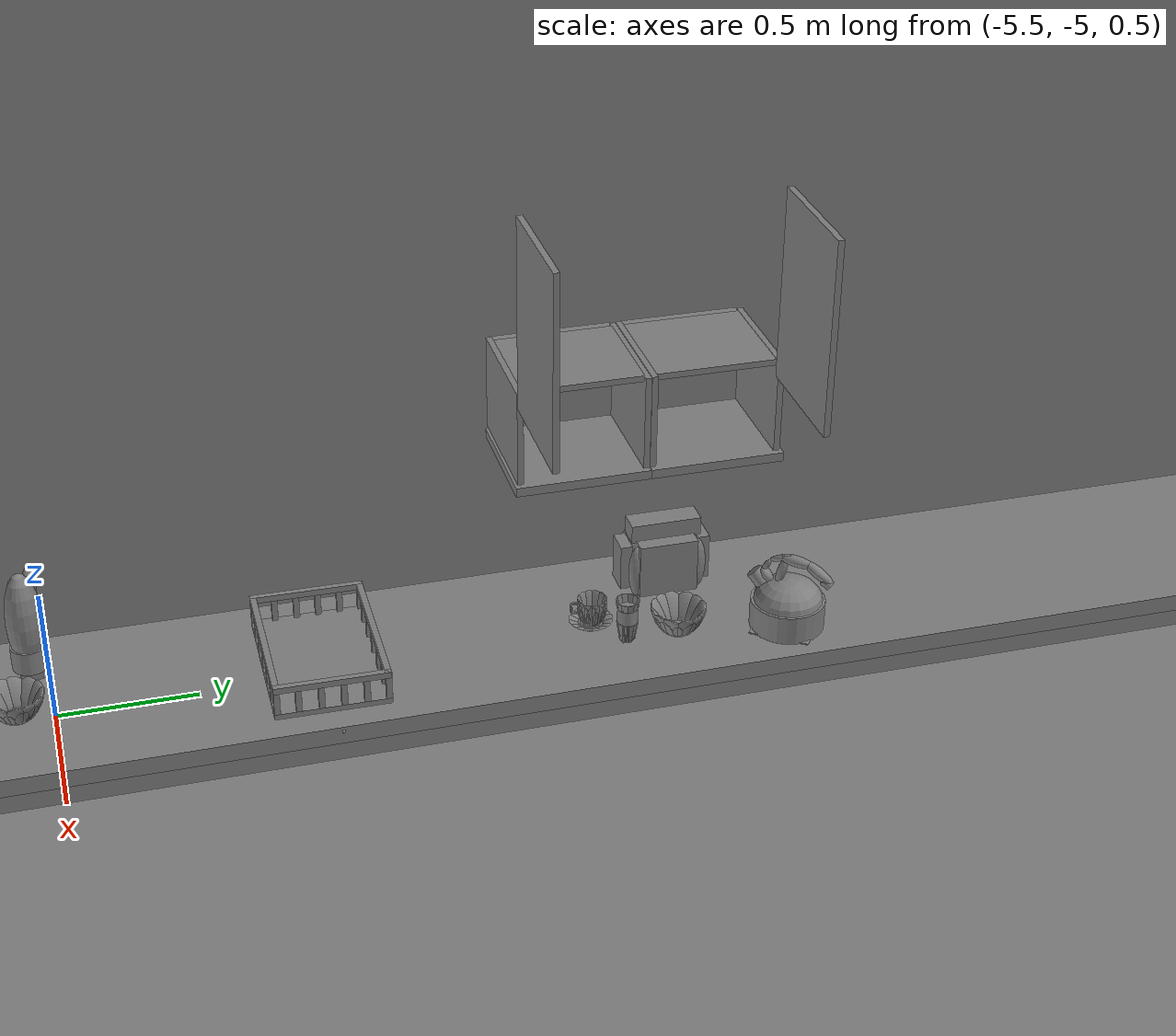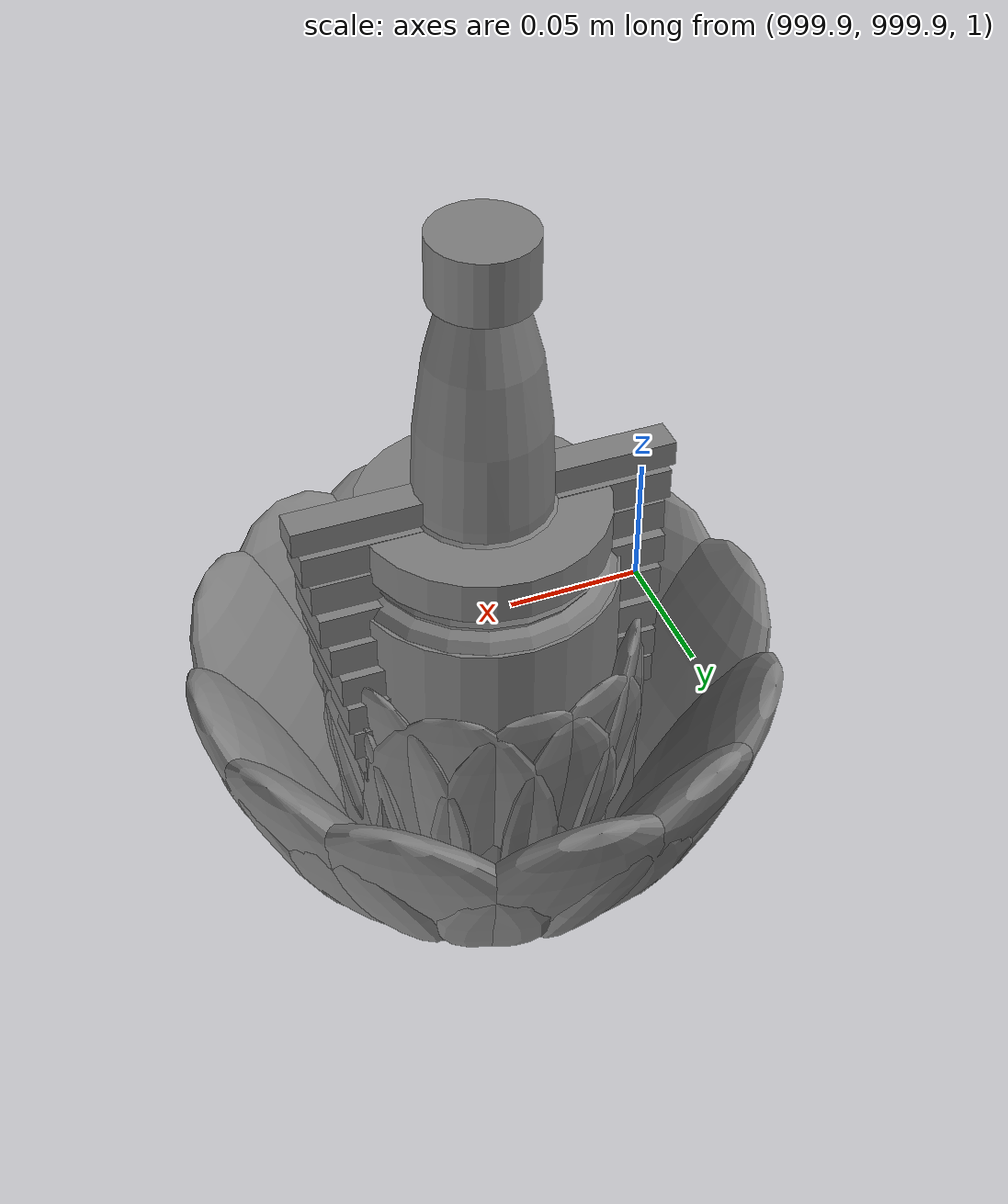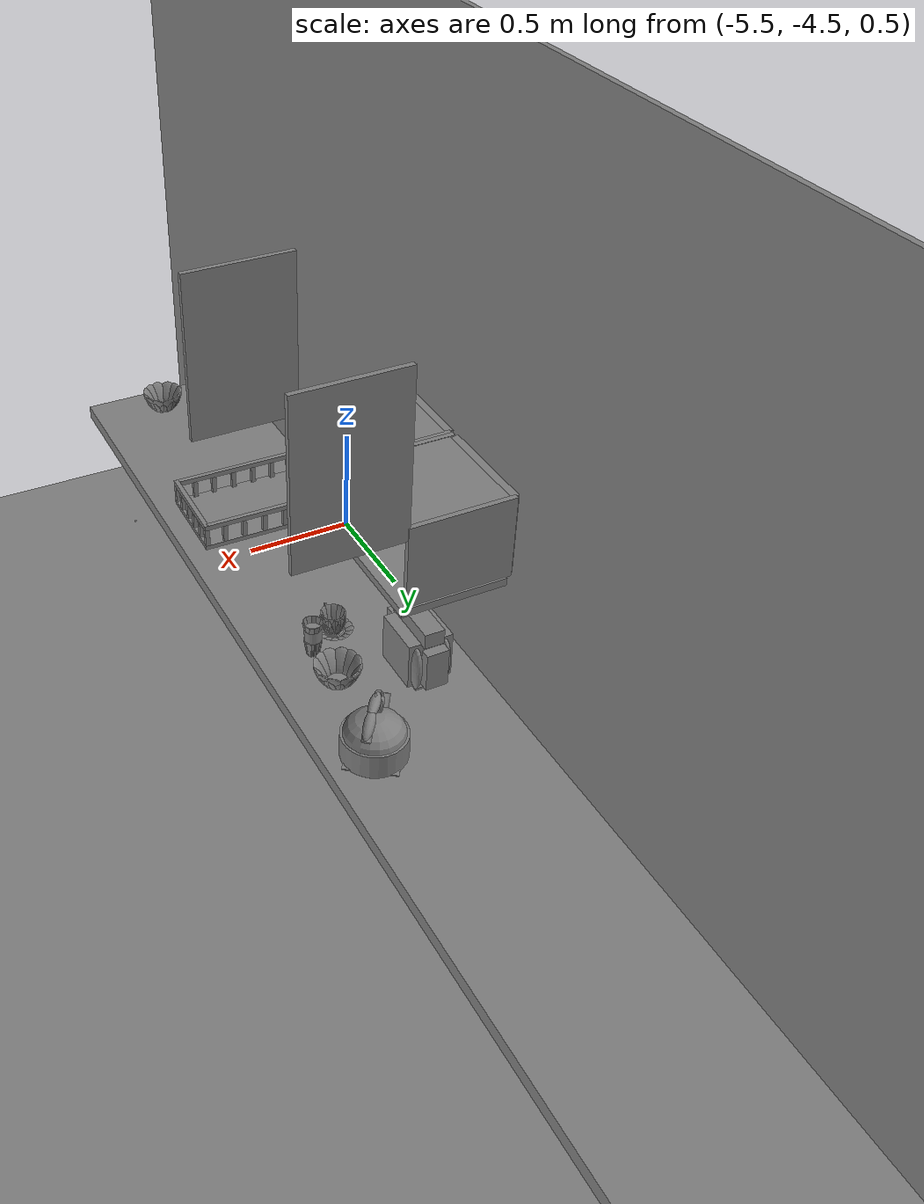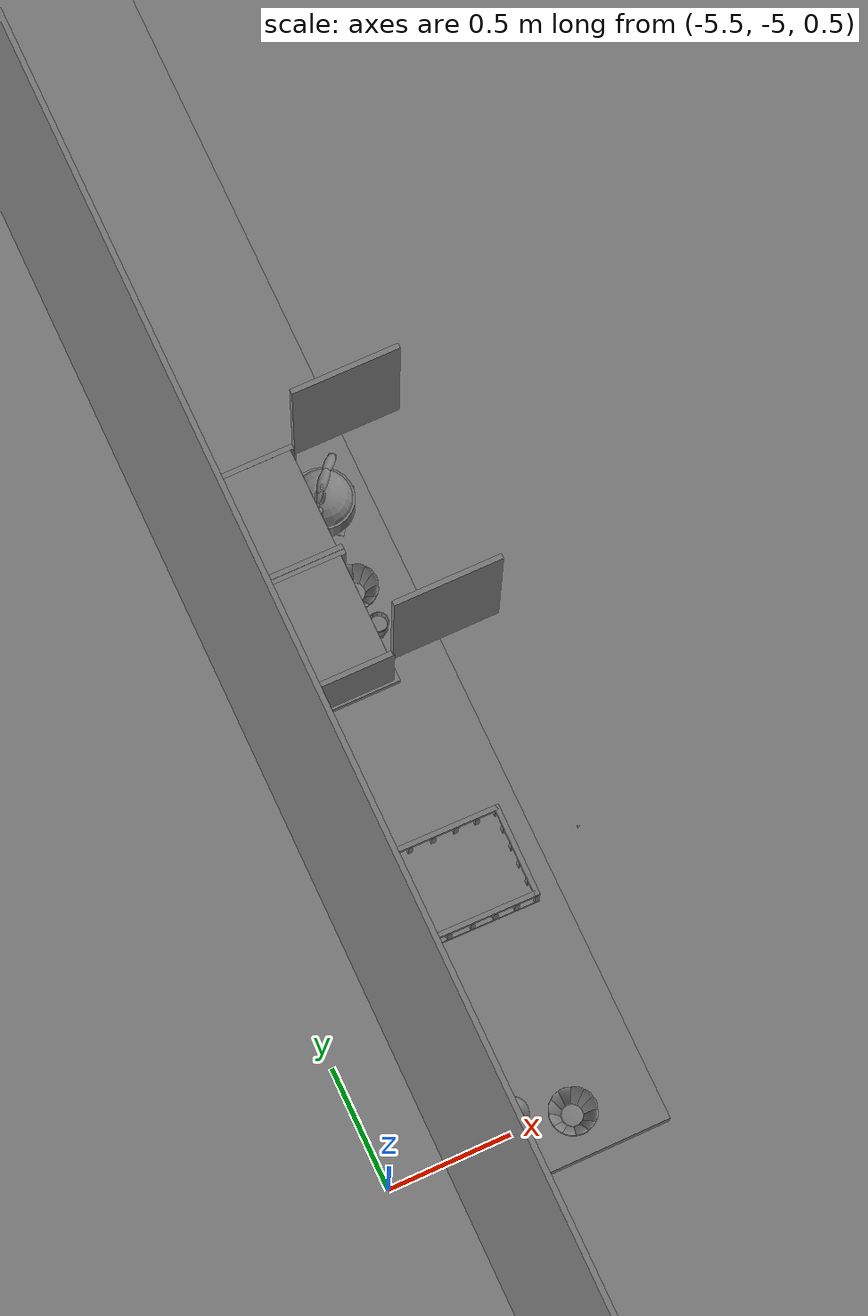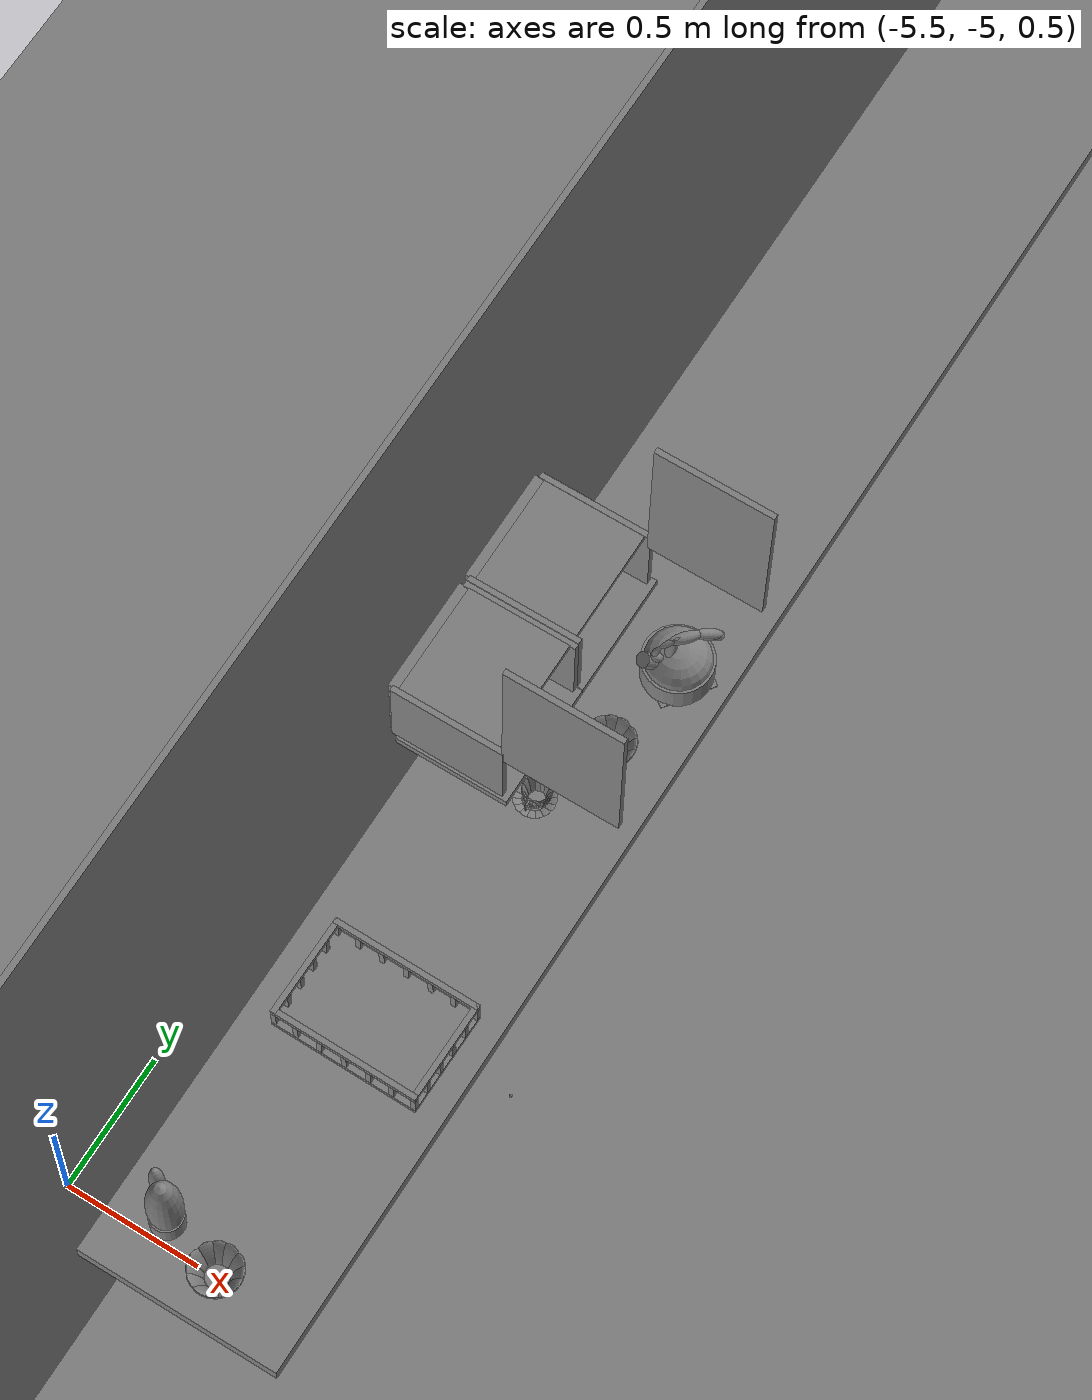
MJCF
<mujoco>
    <option gravity="0.000000000 0.000000000 -9.810000420" timestep="0.0049999999" integrator="implicitfast" density="9.8000002" viscosity="1.8000001e-05" noslip_iterations="10" iterations="100" sdf_iterations="50">
        <flag multiccd="disable"/>
    </option>
    <size memory="1000M"/>
    <compiler coordinate="local"/>
    <worldbody>
        <light cutoff="30" pos="0 1 1" dir="0 -1 -2"/>
        <light cutoff="30" pos="0 -1 1" dir="0 1 -2"/>
        <body pos="-4.721817970 -2.990536690 1.027358174" euler="0.000000000 0.000000000 89.999946594" name="Interactive Objcets_bow_02">
            <geom contype="1" conaffinity="1" density="1000" type="ellipsoid" material="" rgba="0.500000000 0.500000000 0.500000000 1.000000000" solimp="0.899999976 0.949999988 0.001000000" friction="1.000000000 0.005000000 0.000100000" solref="0.020000000 1.000000000" margin="0" condim="3" group="0" pos="0.052321676 -0.040297508 0.044118762" quat="0.919264674 0.076882742 0.225593731 -0.313287675" size="0.010000000 0.039999999 0.052000001" name="Interactive Objcets_geom_53ED8258_5C2C_40A7_8532_20019854A0C2"/>
            <geom contype="1" conaffinity="1" density="1000" type="ellipsoid" material="" rgba="0.500000000 0.500000000 0.500000000 1.000000000" solimp="0.899999976 0.949999988 0.001000000" friction="1.000000000 0.005000000 0.000100000" solref="0.020000000 1.000000000" margin="0" condim="3" group="0" pos="0.040234569 0.052338600 0.044118762" quat="0.429593176 -0.213750035 -0.105424814 -0.871002913" size="0.010000000 0.039999999 0.052000001" name="Interactive Objcets_geom_177CB508_D8F3_4BD4_98ED_867E21DDDD8F"/>
            <geom contype="1" conaffinity="1" density="1000" type="ellipsoid" material="" rgba="0.500000000 0.500000000 0.500000000 1.000000000" solimp="0.899999976 0.949999988 0.001000000" friction="1.000000000 0.005000000 0.000100000" solref="0.020000000 1.000000000" margin="0" condim="3" group="0" pos="0.029448029 -0.059084892 0.044118762" quat="0.825555801 0.125530601 0.202597082 -0.511521280" size="0.010000000 0.039999999 0.052000001" name="Interactive Objcets_geom_81D82926_5921_4789_8446_81E73718462B"/>
            <geom contype="1" conaffinity="1" density="1000" type="ellipsoid" material="" rgba="0.500000000 0.500000000 0.500000000 1.000000000" solimp="0.899999976 0.949999988 0.001000000" friction="1.000000000 0.005000000 0.000100000" solref="0.020000000 1.000000000" margin="0" condim="3" group="0" pos="-0.058925860 -0.029528141 0.044118762" quat="0.223252773 0.231952101 0.054787740 -0.945174515" size="0.010000000 0.039999999 0.052000001" name="Interactive Objcets_geom_271BFE6C_B484_43A5_B742_B6DA4941F701"/>
            <geom contype="1" conaffinity="1" density="1000" type="ellipsoid" material="" rgba="0.500000000 0.500000000 0.500000000 1.000000000" solimp="0.899999976 0.949999988 0.001000000" friction="1.000000000 0.005000000 0.000100000" solref="0.020000000 1.000000000" margin="0" condim="3" group="0" pos="-0.040080305 -0.052354336 0.044118762" quat="0.429593205 0.213749886 0.105425082 -0.871003032" size="0.010000000 0.039999999 0.052000001" name="Interactive Objcets_geom_A0A005ED_C260_4C35_82E3_67686AF39818"/>
            <geom contype="1" conaffinity="1" density="1000" type="ellipsoid" material="" rgba="0.500000000 0.500000000 0.500000000 1.000000000" solimp="0.899999976 0.949999988 0.001000000" friction="1.000000000 0.005000000 0.000100000" solref="0.020000000 1.000000000" margin="0" condim="3" group="0" pos="0.000082973 0.000000000 0.005656481" quat="1.000000000 0.000000000 0.000000000 0.000000000" size="0.039999999 0.039999999 0.002000000" name="Interactive Objcets_geom_975A0D4D_87BA_404B_91B0_C7DFFB190250"/>
            <geom contype="1" conaffinity="1" density="1000" type="ellipsoid" material="" rgba="0.500000000 0.500000000 0.500000000 1.000000000" solimp="0.899999976 0.949999988 0.001000000" friction="1.000000000 0.005000000 0.000100000" solref="0.020000000 1.000000000" margin="0" condim="3" group="0" pos="-0.065898418 -0.000007629 0.044118762" quat="0.971183062 -0.000000142 -0.238334835 0.000000030" size="0.010000000 0.039999999 0.052000001" name="Interactive Objcets_geom_8F4FD730_1A8F_447C_9D6D_2461C45C1B52"/>
            <geom contype="1" conaffinity="1" density="1000" type="ellipsoid" material="" rgba="0.500000000 0.500000000 0.500000000 1.000000000" solimp="0.899999976 0.949999988 0.001000000" friction="1.000000000 0.005000000 0.000100000" solref="0.020000000 1.000000000" margin="0" condim="3" group="0" pos="-0.000090118 0.065967560 0.044118762" quat="0.687598705 -0.168314859 -0.168741152 -0.685860336" size="0.010000000 0.039999999 0.052000001" name="Interactive Objcets_geom_51154C9A_C206_47EB_AB98_E9C2DA7ED753"/>
            <geom contype="1" conaffinity="1" density="1000" type="ellipsoid" material="" rgba="0.500000000 0.500000000 0.500000000 1.000000000" solimp="0.899999976 0.949999988 0.001000000" friction="1.000000000 0.005000000 0.000100000" solref="0.020000000 1.000000000" margin="0" condim="3" group="0" pos="-0.052167647 0.040282249 0.044118762" quat="0.919264615 -0.076883025 -0.225593641 -0.313287735" size="0.010000000 0.039999999 0.052000001" name="Interactive Objcets_geom_10DF3636_F2EB_4197_AC26_8EA349E15F57"/>
            <geom contype="1" conaffinity="1" density="1000" type="ellipsoid" material="" rgba="0.500000000 0.500000000 0.500000000 1.000000000" solimp="0.899999976 0.949999988 0.001000000" friction="1.000000000 0.005000000 0.000100000" solref="0.020000000 1.000000000" margin="0" condim="3" group="0" pos="0.059080135 0.029512405 0.044118762" quat="0.223252743 -0.231952220 -0.054787420 -0.945174456" size="0.010000000 0.039999999 0.052000001" name="Interactive Objcets_geom_B4587629_C28F_49B7_AD0F_BC7E8BACB87C"/>
            <geom contype="1" conaffinity="1" density="1000" type="ellipsoid" material="" rgba="0.500000000 0.500000000 0.500000000 1.000000000" solimp="0.899999976 0.949999988 0.001000000" friction="1.000000000 0.005000000 0.000100000" solref="0.020000000 1.000000000" margin="0" condim="3" group="0" pos="0.000243668 -0.065982819 0.044118762" quat="0.687598705 0.168314636 0.168741375 -0.685860336" size="0.010000000 0.039999999 0.052000001" name="Interactive Objcets_geom_C1E1CF1C_0B7D_4BC9_8408_3994D9D35C94"/>
            <geom contype="1" conaffinity="1" density="1000" type="ellipsoid" material="" rgba="0.500000000 0.500000000 0.500000000 1.000000000" solimp="0.899999976 0.949999988 0.001000000" friction="1.000000000 0.005000000 0.000100000" solref="0.020000000 1.000000000" margin="0" condim="3" group="0" pos="0.066052437 -0.000007629 0.044118762" quat="0.971183062 -0.000000156 0.238334835 0.000000030" size="0.010000000 0.039999999 0.052000001" name="Interactive Objcets_geom_B4335049_8BB3_4D02_A01C_17EA51EAADE0"/>
            <geom contype="1" conaffinity="1" density="1000" type="ellipsoid" material="" rgba="0.500000000 0.500000000 0.500000000 1.000000000" solimp="0.899999976 0.949999988 0.001000000" friction="1.000000000 0.005000000 0.000100000" solref="0.020000000 1.000000000" margin="0" condim="3" group="0" pos="0.000082973 0.000000000 0.000446677" quat="1.000000000 0.000000000 0.000000000 0.000000000" size="0.039999999 0.039999999 0.002000000" name="Interactive Objcets_geom_C0BA40BC_D430_46D5_A534_5F5242EBBD18"/>
            <geom contype="1" conaffinity="1" density="1000" type="ellipsoid" material="" rgba="0.500000000 0.500000000 0.500000000 1.000000000" solimp="0.899999976 0.949999988 0.001000000" friction="1.000000000 0.005000000 0.000100000" solref="0.020000000 1.000000000" margin="0" condim="3" group="0" pos="-0.029293532 0.059069633 0.044118762" quat="0.825555801 -0.125530809 -0.202596903 -0.511521280" size="0.010000000 0.039999999 0.052000001" name="Interactive Objcets_geom_008A1AEE_FC5C_4761_92E7_772DED96A291"/>
            <freejoint name="Interactive Objcets_bow_02"/>
        </body>
        <body pos="1000.000000000 1000.000000000 1.000000000" euler="0.000000000 0.000000000 0.000000000" name="openloong_gripper_2f85_fix_base_usda_jar_01">
            <geom contype="1" conaffinity="1" density="1000" type="box" material="" rgba="0.500000000 0.500000000 0.500000000 1.000000000" solimp="0.899999976 0.949999988 0.001000000" friction="1.000000000 0.005000000 0.000100000" solref="0.020000000 1.000000000" margin="0" condim="3" group="0" pos="0.000000000 0.000000000 0.006158113" quat="1.000000000 0.000000000 0.000000000 0.000000000" size="0.020000000 0.020000000 0.005000000" name="openloong_gripper_2f85_fix_base_usda_geom_0055F9D8_7048_42DD_9216_9DE43DDACAA0"/>
            <geom contype="1" conaffinity="1" density="1000" type="cylinder" material="" rgba="0.500000000 0.500000000 0.500000000 1.000000000" solimp="0.899999976 0.949999988 0.001000000" friction="1.000000000 0.005000000 0.000100000" solref="0.020000000 1.000000000" margin="0" condim="3" group="0" pos="0.000000000 0.000000000 0.062744498" quat="1.000000000 0.000000000 0.000000000 0.000000000" size="0.041000001 0.052999999 1.000000000" name="openloong_gripper_2f85_fix_base_usda_geom_ACC9844D_AFAB_4B9F_B5E9_C4B9EFCC50E3"/>
            <geom contype="1" conaffinity="1" density="1000" type="ellipsoid" material="" rgba="0.500000000 0.500000000 0.500000000 1.000000000" solimp="0.899999976 0.949999988 0.001000000" friction="1.000000000 0.005000000 0.000100000" solref="0.020000000 1.000000000" margin="0" condim="3" group="0" pos="0.000000000 0.000000000 0.122252703" quat="1.000000000 0.000000000 0.000000000 0.000000000" size="0.035999998 0.035999998 0.010000000" name="openloong_gripper_2f85_fix_base_usda_geom_3500CB36_01EB_41F8_A11F_F3AE066B0350"/>
            <geom contype="1" conaffinity="1" density="1000" type="cylinder" material="" rgba="0.500000000 0.500000000 0.500000000 1.000000000" solimp="0.899999976 0.949999988 0.001000000" friction="1.000000000 0.005000000 0.000100000" solref="0.020000000 1.000000000" margin="0" condim="3" group="0" pos="0.000000000 0.000000000 0.015747190" quat="1.000000000 0.000000000 0.000000000 0.000000000" size="0.035000000 0.010000000 1.000000000" name="openloong_gripper_2f85_fix_base_usda_geom_181F1A7C_43BC_40E4_A936_CD623C4924C7"/>
            <geom contype="1" conaffinity="1" density="1000" type="ellipsoid" material="" rgba="0.500000000 0.500000000 0.500000000 1.000000000" solimp="0.899999976 0.949999988 0.001000000" friction="1.000000000 0.005000000 0.000100000" solref="0.020000000 1.000000000" margin="0" condim="3" group="0" pos="0.000000000 0.000000000 0.115815401" quat="1.000000000 0.000000000 0.000000000 0.000000000" size="0.039999999 0.039999999 0.010000000" name="openloong_gripper_2f85_fix_base_usda_geom_EC969340_AAC1_4E6A_A753_DBEDB53438FB"/>
            <geom contype="1" conaffinity="1" density="1000" type="cylinder" material="" rgba="0.500000000 0.500000000 0.500000000 1.000000000" solimp="0.899999976 0.949999988 0.001000000" friction="1.000000000 0.005000000 0.000100000" solref="0.020000000 1.000000000" margin="0" condim="3" group="0" pos="0.000000000 0.000000000 0.133183479" quat="1.000000000 0.000000000 0.000000000 0.000000000" size="0.037999999 0.006500000 1.000000000" name="openloong_gripper_2f85_fix_base_usda_geom_ABA1E1A9_D663_4BC1_8809_0F30ECE68112"/>
            <freejoint name="openloong_gripper_2f85_fix_base_usda_jar_01_joint"/>
            <site size="0.005000000 0.005000000 0.005000000" rgba="0.500000000 0.500000000 0.500000000 1.000000000" pos="0.000000000 0.000000000 0.000000000" quat="1.000000000 0.000000000 0.000000000 0.000000000" group="0" type="sphere" name="openloong_gripper_2f85_fix_base_usda_jar_01site"/>
        </body>
        <body pos="1000.000000000 1000.000000000 1.000000000" euler="0.000000000 0.000000000 0.000000000" name="openloong_gripper_2f85_fix_base_usda_salt">
            <geom contype="1" conaffinity="1" density="1000" type="box" material="" rgba="0.500000000 0.500000000 0.500000000 1.000000000" solimp="0.899999976 0.949999988 0.001000000" friction="1.000000000 0.005000000 0.000100000" solref="0.020000000 1.000000000" margin="0" condim="3" group="0" pos="0.000305176 0.000000000 0.084862232" quat="1.000000000 0.000000000 0.000000000 0.000000000" size="0.048999999 0.018999999 0.005000000" name="openloong_gripper_2f85_fix_base_usda_geom_9CCBEDF1_C423_40C0_9D7A_75B879DE0F6C"/>
            <geom contype="1" conaffinity="1" density="1000" type="box" material="" rgba="0.500000000 0.500000000 0.500000000 1.000000000" solimp="0.899999976 0.949999988 0.001000000" friction="1.000000000 0.005000000 0.000100000" solref="0.020000000 1.000000000" margin="0" condim="3" group="0" pos="0.000305176 0.000000000 0.104564309" quat="1.000000000 0.000000000 0.000000000 0.000000000" size="0.052000001 0.014000000 0.005000000" name="openloong_gripper_2f85_fix_base_usda_geom_283F947B_F1A3_444C_9F4B_7DEB876C1391"/>
            <geom contype="1" conaffinity="1" density="1000" type="box" material="" rgba="0.500000000 0.500000000 0.500000000 1.000000000" solimp="0.899999976 0.949999988 0.001000000" friction="1.000000000 0.005000000 0.000100000" solref="0.020000000 1.000000000" margin="0" condim="3" group="0" pos="0.000305176 0.000000000 0.114487171" quat="1.000000000 0.000000000 0.000000000 0.000000000" size="0.054000001 0.011500000 0.005000000" name="openloong_gripper_2f85_fix_base_usda_geom_3EAB3466_0BF7_4663_AD95_4F9DAD5EBB46"/>
            <geom contype="1" conaffinity="1" density="1000" type="box" material="" rgba="0.500000000 0.500000000 0.500000000 1.000000000" solimp="0.899999976 0.949999988 0.001000000" friction="1.000000000 0.005000000 0.000100000" solref="0.020000000 1.000000000" margin="0" condim="3" group="0" pos="0.000305176 0.000000000 0.075103164" quat="1.000000000 0.000000000 0.000000000 0.000000000" size="0.048000000 0.020000000 0.005000000" name="openloong_gripper_2f85_fix_base_usda_geom_25B1702E_C99A_4F71_B5D9_26FF1C4A0795"/>
            <geom contype="1" conaffinity="1" density="1000" type="box" material="" rgba="0.500000000 0.500000000 0.500000000 1.000000000" solimp="0.899999976 0.949999988 0.001000000" friction="1.000000000 0.005000000 0.000100000" solref="0.020000000 1.000000000" margin="0" condim="3" group="0" pos="0.000305176 0.000000000 0.134892464" quat="1.000000000 0.000000000 0.000000000 0.000000000" size="0.057000000 0.007000000 0.005000000" name="openloong_gripper_2f85_fix_base_usda_geom_FC080EA1_30AF_4FDB_93F5_EB58390A8C8D"/>
            <geom contype="1" conaffinity="1" density="1000" type="box" material="" rgba="0.500000000 0.500000000 0.500000000 1.000000000" solimp="0.899999976 0.949999988 0.001000000" friction="1.000000000 0.005000000 0.000100000" solref="0.020000000 1.000000000" margin="0" condim="3" group="0" pos="0.000305176 0.000000000 0.094920278" quat="1.000000000 0.000000000 0.000000000 0.000000000" size="0.050000001 0.017000001 0.005000000" name="openloong_gripper_2f85_fix_base_usda_geom_AE8D50F7_B753_4B4C_A21C_3474C6BF3FC3"/>
            <geom contype="1" conaffinity="1" density="1000" type="box" material="" rgba="0.500000000 0.500000000 0.500000000 1.000000000" solimp="0.899999976 0.949999988 0.001000000" friction="1.000000000 0.005000000 0.000100000" solref="0.020000000 1.000000000" margin="0" condim="3" group="0" pos="0.000305176 0.000000000 0.065204859" quat="1.000000000 0.000000000 0.000000000 0.000000000" size="0.045000002 0.021000000 0.005000000" name="openloong_gripper_2f85_fix_base_usda_geom_9DABE5D9_F00D_4EDA_A42B_CD4EDF1E98F9"/>
            <geom contype="1" conaffinity="1" density="1000" type="box" material="" rgba="0.500000000 0.500000000 0.500000000 1.000000000" solimp="0.899999976 0.949999988 0.001000000" friction="1.000000000 0.005000000 0.000100000" solref="0.020000000 1.000000000" margin="0" condim="3" group="0" pos="0.000305176 0.000000000 0.144135714" quat="1.000000000 0.000000000 0.000000000 0.000000000" size="0.059000000 0.005000000 0.004000000" name="openloong_gripper_2f85_fix_base_usda_geom_BCFEC68D_0687_4D1C_97FB_5113AF34C76E"/>
            <geom contype="1" conaffinity="1" density="1000" type="box" material="" rgba="0.500000000 0.500000000 0.500000000 1.000000000" solimp="0.899999976 0.949999988 0.001000000" friction="1.000000000 0.005000000 0.000100000" solref="0.020000000 1.000000000" margin="0" condim="3" group="0" pos="0.000000000 0.000000000 0.031593561" quat="1.000000000 0.000000000 0.000000000 0.000000000" size="0.041999999 0.024000000 0.029999999" name="openloong_gripper_2f85_fix_base_usda_geom_DFB0F6B1_60A5_444C_B992_E7559494A19C"/>
            <geom contype="1" conaffinity="1" density="1000" type="box" material="" rgba="0.500000000 0.500000000 0.500000000 1.000000000" solimp="0.899999976 0.949999988 0.001000000" friction="1.000000000 0.005000000 0.000100000" solref="0.020000000 1.000000000" margin="0" condim="3" group="0" pos="0.000305176 0.000000000 0.124608755" quat="1.000000000 0.000000000 0.000000000 0.000000000" size="0.055000000 0.008000000 0.005000000" name="openloong_gripper_2f85_fix_base_usda_geom_E1F285F0_884C_4586_93B9_924C9BEB6B99"/>
            <freejoint name="openloong_gripper_2f85_fix_base_usda_salt_joint"/>
            <site size="0.005000000 0.005000000 0.005000000" rgba="0.500000000 0.500000000 0.500000000 1.000000000" pos="0.000000000 0.000000000 0.000000000" quat="1.000000000 0.000000000 0.000000000 0.000000000" group="0" type="sphere" name="openloong_gripper_2f85_fix_base_usda_saltsite"/>
        </body>
        <body pos="1000.000000000 1000.000000000 1.000000000" euler="0.000000000 0.000000000 0.000000000" name="openloong_gripper_2f85_fix_base_usda_bottle_red">
            <geom contype="1" conaffinity="1" density="1000" type="ellipsoid" material="" rgba="0.500000000 0.500000000 0.500000000 1.000000000" solimp="0.899999976 0.949999988 0.001000000" friction="1.000000000 0.005000000 0.000100000" solref="0.020000000 1.000000000" margin="0" condim="3" group="0" pos="0.000000000 0.000000000 0.144284487" quat="1.000000000 0.000000000 0.000000000 0.000000000" size="0.021000000 0.021000000 0.079999998" name="openloong_gripper_2f85_fix_base_usda_geom_146B4DAC_C4BA_4100_8A34_B928E872B459"/>
            <geom contype="1" conaffinity="1" density="1000" type="cylinder" material="" rgba="0.500000000 0.500000000 0.500000000 1.000000000" solimp="0.899999976 0.949999988 0.001000000" friction="1.000000000 0.005000000 0.000100000" solref="0.020000000 1.000000000" margin="0" condim="3" group="0" pos="0.000000000 0.000000000 0.220618963" quat="1.000000000 0.000000000 0.000000000 0.000000000" size="0.016000001 0.010000000 1.000000000" name="openloong_gripper_2f85_fix_base_usda_geom_65B65CB1_2527_413D_9F54_0FE51533A16F"/>
            <geom contype="1" conaffinity="1" density="1000" type="ellipsoid" material="" rgba="0.500000000 0.500000000 0.500000000 1.000000000" solimp="0.899999976 0.949999988 0.001000000" friction="1.000000000 0.005000000 0.000100000" solref="0.020000000 1.000000000" margin="0" condim="3" group="0" pos="0.000000000 0.000000000 0.118945479" quat="1.000000000 0.000000000 0.000000000 0.000000000" size="0.030999999 0.030999999 0.029999999" name="openloong_gripper_2f85_fix_base_usda_geom_9021D13B_1C59_4425_BB18_B4EEEF76E927"/>
            <geom contype="1" conaffinity="1" density="1000" type="box" material="" rgba="0.500000000 0.500000000 0.500000000 1.000000000" solimp="0.899999976 0.949999988 0.001000000" friction="1.000000000 0.005000000 0.000100000" solref="0.020000000 1.000000000" margin="0" condim="3" group="0" pos="0.000000000 0.000000000 0.002189159" quat="1.000000000 0.000000000 0.000000000 0.000000000" size="0.020000000 0.020000000 0.003000000" name="openloong_gripper_2f85_fix_base_usda_geom_24561F92_644B_4703_A438_48AEE07B104B"/>
            <geom contype="1" conaffinity="1" density="1000" type="cylinder" material="" rgba="0.500000000 0.500000000 0.500000000 1.000000000" solimp="0.899999976 0.949999988 0.001000000" friction="1.000000000 0.005000000 0.000100000" solref="0.020000000 1.000000000" margin="0" condim="3" group="0" pos="0.000000000 -0.000366211 0.060884237" quat="1.000000000 0.000000000 0.000000000 0.000000000" size="0.030999999 0.057999998 1.000000000" name="openloong_gripper_2f85_fix_base_usda_geom_138C0581_B745_44C6_8844_9901D63DEF28"/>
            <freejoint name="openloong_gripper_2f85_fix_base_usda_bottle_red_joint"/>
            <site size="0.005000000 0.005000000 0.005000000" rgba="0.500000000 0.500000000 0.500000000 1.000000000" pos="0.000000000 0.000000000 0.000000000" quat="0.999961913 0.008726535 0.000000000 0.000000000" group="0" type="sphere" name="openloong_gripper_2f85_fix_base_usda_bottle_redsite"/>
        </body>
        <body pos="-4.437532902 -4.239471436 1.806414127" euler="-52.483577728 -26.511917114 -14.266630173" mocap="true" name="spotlight4_SpotLight"/>
        <body pos="1000.000000000 1000.000000000 1.000000000" euler="0.000000000 0.000000000 0.000000000" name="openloong_gripper_2f85_fix_base_usda_bow_yellow_kps">
            <geom contype="1" conaffinity="1" density="1000" type="ellipsoid" material="" rgba="0.500000000 0.500000000 0.500000000 1.000000000" solimp="0.899999976 0.949999988 0.001000000" friction="1.000000000 0.005000000 0.000100000" solref="0.020000000 1.000000000" margin="0" condim="3" group="0" pos="-0.052185059 0.040283203 0.044118762" quat="0.919264615 -0.076883033 -0.225593656 -0.313287765" size="0.010000000 0.039999999 0.052000001" name="openloong_gripper_2f85_fix_base_usda_geom_40B16112_79D6_4446_AB20_2E82CB3E0645"/>
            <geom contype="1" conaffinity="1" density="1000" type="ellipsoid" material="" rgba="0.500000000 0.500000000 0.500000000 1.000000000" solimp="0.899999976 0.949999988 0.001000000" friction="1.000000000 0.005000000 0.000100000" solref="0.020000000 1.000000000" margin="0" condim="3" group="0" pos="-0.000061035 0.065979004 0.044118762" quat="0.687598765 -0.168314874 -0.168741167 -0.685860336" size="0.010000000 0.039999999 0.052000001" name="openloong_gripper_2f85_fix_base_usda_geom_B50E544E_F3AA_4C14_AACF_E0BD8AA942ED"/>
            <geom contype="1" conaffinity="1" density="1000" type="box" material="" rgba="0.500000000 0.500000000 0.500000000 1.000000000" solimp="0.899999976 0.949999988 0.001000000" friction="1.000000000 0.005000000 0.000100000" solref="0.020000000 1.000000000" margin="0" condim="3" group="0" pos="0.000061035 0.000000000 -0.002001643" quat="1.000000000 0.000000000 0.000000000 0.000000000" size="0.029999999 0.029999999 0.002000000" name="openloong_gripper_2f85_fix_base_usda_geom_E8ADCBA7_5C2C_4E63_A4C6_127D05BBF973"/>
            <geom contype="1" conaffinity="1" density="1000" type="ellipsoid" material="" rgba="0.500000000 0.500000000 0.500000000 1.000000000" solimp="0.899999976 0.949999988 0.001000000" friction="1.000000000 0.005000000 0.000100000" solref="0.020000000 1.000000000" margin="0" condim="3" group="0" pos="0.029418945 -0.059082031 0.044118762" quat="0.825555861 0.125530601 0.202597082 -0.511521280" size="0.010000000 0.039999999 0.052000001" name="openloong_gripper_2f85_fix_base_usda_geom_12AB3262_7C8E_4BD1_976A_459B36D71451"/>
            <geom contype="1" conaffinity="1" density="1000" type="ellipsoid" material="" rgba="0.500000000 0.500000000 0.500000000 1.000000000" solimp="0.899999976 0.949999988 0.001000000" friction="1.000000000 0.005000000 0.000100000" solref="0.020000000 1.000000000" margin="0" condim="3" group="0" pos="0.000244141 -0.065979004 0.044118762" quat="0.687598765 0.168314651 0.168741375 -0.685860336" size="0.010000000 0.039999999 0.052000001" name="openloong_gripper_2f85_fix_base_usda_geom_52D8B56F_93BC_400A_BD7E_9E38B7A2BC86"/>
            <geom contype="1" conaffinity="1" density="1000" type="ellipsoid" material="" rgba="0.500000000 0.500000000 0.500000000 1.000000000" solimp="0.899999976 0.949999988 0.001000000" friction="1.000000000 0.005000000 0.000100000" solref="0.020000000 1.000000000" margin="0" condim="3" group="0" pos="0.000061035 0.000000000 0.000446677" quat="1.000000000 0.000000000 0.000000000 0.000000000" size="0.039999999 0.039999999 0.002000000" name="openloong_gripper_2f85_fix_base_usda_geom_446A52C9_6BFC_4373_8256_5FD16A25C897"/>
            <geom contype="1" conaffinity="1" density="1000" type="ellipsoid" material="" rgba="0.500000000 0.500000000 0.500000000 1.000000000" solimp="0.899999976 0.949999988 0.001000000" friction="1.000000000 0.005000000 0.000100000" solref="0.020000000 1.000000000" margin="0" condim="3" group="0" pos="0.059082031 0.029541016 0.044118762" quat="0.223252773 -0.231952220 -0.054787423 -0.945174456" size="0.010000000 0.039999999 0.052000001" name="openloong_gripper_2f85_fix_base_usda_geom_1651EB71_BB87_473B_A594_BEE216CA7856"/>
            <geom contype="1" conaffinity="1" density="1000" type="ellipsoid" material="" rgba="0.500000000 0.500000000 0.500000000 1.000000000" solimp="0.899999976 0.949999988 0.001000000" friction="1.000000000 0.005000000 0.000100000" solref="0.020000000 1.000000000" margin="0" condim="3" group="0" pos="0.000061035 0.000000000 0.007335305" quat="1.000000000 0.000000000 0.000000000 0.000000000" size="0.039999999 0.039999999 0.002000000" name="openloong_gripper_2f85_fix_base_usda_geom_4BA197CE_D404_4CB0_B675_265567521033"/>
            <geom contype="1" conaffinity="1" density="1000" type="ellipsoid" material="" rgba="0.500000000 0.500000000 0.500000000 1.000000000" solimp="0.899999976 0.949999988 0.001000000" friction="1.000000000 0.005000000 0.000100000" solref="0.020000000 1.000000000" margin="0" condim="3" group="0" pos="-0.029296875 0.059082031 0.044118762" quat="0.825555861 -0.125530809 -0.202596918 -0.511521280" size="0.010000000 0.039999999 0.052000001" name="openloong_gripper_2f85_fix_base_usda_geom_FF82B8EE_B37A_4529_9AE3_67C0D7A2FDEE"/>
            <geom contype="1" conaffinity="1" density="1000" type="ellipsoid" material="" rgba="0.500000000 0.500000000 0.500000000 1.000000000" solimp="0.899999976 0.949999988 0.001000000" friction="1.000000000 0.005000000 0.000100000" solref="0.020000000 1.000000000" margin="0" condim="3" group="0" pos="0.040222168 0.052368164 0.044118762" quat="0.429593176 -0.213750049 -0.105424821 -0.871002972" size="0.010000000 0.039999999 0.052000001" name="openloong_gripper_2f85_fix_base_usda_geom_9A80351A_3FE1_4810_8219_FE9CBA0AD0D6"/>
            <geom contype="1" conaffinity="1" density="1000" type="ellipsoid" material="" rgba="0.500000000 0.500000000 0.500000000 1.000000000" solimp="0.899999976 0.949999988 0.001000000" friction="1.000000000 0.005000000 0.000100000" solref="0.020000000 1.000000000" margin="0" condim="3" group="0" pos="0.066040039 0.000000000 0.044118762" quat="0.971183062 -0.000000156 0.238334835 0.000000030" size="0.010000000 0.039999999 0.052000001" name="openloong_gripper_2f85_fix_base_usda_geom_417BD154_BE73_495A_8DFD_38DAF6B1E9C7"/>
            <geom contype="1" conaffinity="1" density="1000" type="ellipsoid" material="" rgba="0.500000000 0.500000000 0.500000000 1.000000000" solimp="0.899999976 0.949999988 0.001000000" friction="1.000000000 0.005000000 0.000100000" solref="0.020000000 1.000000000" margin="0" condim="3" group="0" pos="0.052307129 -0.040283203 0.044118762" quat="0.919264674 0.076882750 0.225593731 -0.313287705" size="0.010000000 0.039999999 0.052000001" name="openloong_gripper_2f85_fix_base_usda_geom_84B16DE1_A098_4DE1_9E9F_663B6963C1CF"/>
            <geom contype="1" conaffinity="1" density="1000" type="ellipsoid" material="" rgba="0.500000000 0.500000000 0.500000000 1.000000000" solimp="0.899999976 0.949999988 0.001000000" friction="1.000000000 0.005000000 0.000100000" solref="0.020000000 1.000000000" margin="0" condim="3" group="0" pos="-0.065917969 0.000000000 0.044118762" quat="0.971183062 -0.000000142 -0.238334835 0.000000030" size="0.010000000 0.039999999 0.052000001" name="openloong_gripper_2f85_fix_base_usda_geom_F53EB197_92FE_4264_8997_106673BAA215"/>
            <geom contype="1" conaffinity="1" density="1000" type="ellipsoid" material="" rgba="0.500000000 0.500000000 0.500000000 1.000000000" solimp="0.899999976 0.949999988 0.001000000" friction="1.000000000 0.005000000 0.000100000" solref="0.020000000 1.000000000" margin="0" condim="3" group="0" pos="-0.058898926 -0.029541016 0.044118762" quat="0.223252758 0.231952101 0.054787733 -0.945174575" size="0.010000000 0.039999999 0.052000001" name="openloong_gripper_2f85_fix_base_usda_geom_7137CCEA_2019_48A1_B73D_5626A43FA8E4"/>
            <geom contype="1" conaffinity="1" density="1000" type="ellipsoid" material="" rgba="0.500000000 0.500000000 0.500000000 1.000000000" solimp="0.899999976 0.949999988 0.001000000" friction="1.000000000 0.005000000 0.000100000" solref="0.020000000 1.000000000" margin="0" condim="3" group="0" pos="-0.040100098 -0.052368164 0.044118762" quat="0.429593235 0.213749886 0.105425082 -0.871003032" size="0.010000000 0.039999999 0.052000001" name="openloong_gripper_2f85_fix_base_usda_geom_C113EFD2_2A85_4948_A206_7BD92EFEFA6F"/>
            <freejoint name="openloong_gripper_2f85_fix_base_usda_bow_yellow_kps_joint"/>
            <site size="0.005000000 0.005000000 0.005000000" rgba="0.500000000 0.500000000 0.500000000 1.000000000" pos="0.000000000 0.000000000 0.000000000" quat="0.999961913 0.008726534 0.000000000 0.000000000" group="0" type="sphere" name="openloong_gripper_2f85_fix_base_usda_bow_yellow_kps"/>
        </body>
        <body pos="0.000000000 0.000000000 0.000000000" euler="0.000000000 0.000000000 0.000000000" name="Static Objcets_Static Objcets">
            <geom contype="1" conaffinity="1" density="1000" type="box" material="" rgba="0.500000000 0.500000000 0.500000000 1.000000000" solimp="0.899999976 0.949999988 0.001000000" friction="1.000000000 0.005000000 0.000100000" solref="0.020000000 1.000000000" margin="0" condim="3" group="0" pos="-5.189302921 -3.293644905 1.760152459" quat="0.707107067 0.707106471 0.000000000 0.000000000" size="0.025000000 0.159999996 0.200000003" name="Static Objcets_geom_2314F7DA_7D56_4519_A393_FCEE3D5AF8EC"/>
            <geom contype="1" conaffinity="1" density="1000" type="box" material="" rgba="0.500000000 0.500000000 0.500000000 1.000000000" solimp="0.899999976 0.949999988 0.001000000" friction="1.000000000 0.005000000 0.000100000" solref="0.020000000 1.000000000" margin="0" condim="3" group="0" pos="-4.999745846 -3.497932911 1.764780521" quat="0.707107067 0.707106471 0.000000000 0.000000000" size="0.200000003 0.159999996 0.010000000" name="Static Objcets_geom_8C01B4FA_E831_4AB0_ACBB_98200BDE1F2F"/>
            <geom contype="1" conaffinity="1" density="1000" type="box" material="" rgba="0.500000000 0.500000000 0.500000000 1.000000000" solimp="0.899999976 0.949999988 0.001000000" friction="1.000000000 0.005000000 0.000100000" solref="0.020000000 1.000000000" margin="0" condim="3" group="0" pos="-4.979488373 -3.297635794 1.591412544" quat="0.707106829 0.707106709 0.000000000 0.000000000" size="0.200000003 0.015000000 0.219999999" name="Static Objcets_geom_C3779BE6_F701_439B_BA3A_7F4B59627A3F"/>
            <geom contype="1" conaffinity="1" density="1000" type="box" material="" rgba="0.500000000 0.500000000 0.500000000 1.000000000" solimp="0.899999976 0.949999988 0.001000000" friction="1.000000000 0.005000000 0.000100000" solref="0.020000000 1.000000000" margin="0" condim="3" group="0" pos="-4.999745846 -3.087441683 1.763863802" quat="0.707107067 0.707106471 0.000000000 0.000000000" size="0.200000003 0.159999996 0.010000000" name="Static Objcets_geom_B28DEC03_AB93_4C19_BCB6_CE6C2F5025D7"/>
            <geom contype="1" conaffinity="1" density="1000" type="box" material="" rgba="0.500000000 0.500000000 0.500000000 1.000000000" solimp="0.899999976 0.949999988 0.001000000" friction="1.000000000 0.005000000 0.000100000" solref="0.020000000 1.000000000" margin="0" condim="3" group="0" pos="-5.000125408 -3.294431210 1.913951039" quat="0.707107067 0.707106471 0.000000000 0.000000000" size="0.180000007 0.010000000 0.200000003" name="Static Objcets_geom_F45E7F0C_6BEA_4968_A0D3_7EDE24FF6165"/>
            <geom contype="1" conaffinity="1" density="1000" type="box" material="" rgba="0.500000000 0.500000000 0.500000000 1.000000000" solimp="0.899999976 0.949999988 0.001000000" friction="1.000000000 0.005000000 0.000100000" solref="0.020000000 1.000000000" margin="0" condim="3" group="0" pos="-4.873187065 -2.461376429 0.977675021" quat="0.707107067 0.707106471 0.000000000 0.000000000" size="0.370000005 0.029999999 2.799999952" name="Static Objcets_geom_D1FC7336_FC9D_4BD8_BBAA_DF130FB5748F"/>
            <geom contype="1" conaffinity="1" density="1000" type="box" material="" rgba="0.500000000 0.500000000 0.500000000 1.000000000" solimp="0.899999976 0.949999988 0.001000000" friction="1.000000000 0.005000000 0.000100000" solref="0.020000000 1.000000000" margin="0" condim="3" group="0" pos="-5.244853973 -2.375543594 1.820221663" quat="0.707107008 0.707106531 0.000000000 0.000000000" size="0.010000000 1.500000000 3.700000048" name="Static Objcets_geom_8A5CDDE4_9DFE_46ED_9C72_77BFDCC2BB9A"/>
            <geom contype="1" conaffinity="1" density="1000" type="box" material="" rgba="0.500000000 0.500000000 0.500000000 1.000000000" solimp="0.899999976 0.949999988 0.001000000" friction="1.000000000 0.005000000 0.000100000" solref="0.020000000 1.000000000" margin="0" condim="3" group="0" pos="-0.720102787 0.222944975 -1.102830648" quat="0.000000954 1.000000000 0.000000000 0.000000000" size="8.000000000 8.000000000 0.010000000" name="Static Objcets_geom_88E3CD99_C6B0_4834_99BF_8725388FCD78"/>
            <geom contype="1" conaffinity="1" density="1000" type="box" material="" rgba="0.500000000 0.500000000 0.500000000 1.000000000" solimp="0.899999976 0.949999988 0.001000000" friction="1.000000000 0.005000000 0.000100000" solref="0.020000000 1.000000000" margin="0" condim="3" group="0" pos="-4.999745846 -2.653569937 1.764779806" quat="0.707107067 0.707106471 0.000000000 0.000000000" size="0.200000003 0.159999996 0.010000000" name="Static Objcets_geom_AFFC9AC8_7F30_4C1B_98B6_54085CFD8A12"/>
            <geom contype="1" conaffinity="1" density="1000" type="box" material="" rgba="0.500000000 0.500000000 0.500000000 1.000000000" solimp="0.899999976 0.949999988 0.001000000" friction="1.000000000 0.005000000 0.000100000" solref="0.020000000 1.000000000" margin="0" condim="3" group="0" pos="-5.000125408 -2.861802340 1.913950682" quat="0.707107067 0.707106471 0.000000000 0.000000000" size="0.180000007 0.010000000 0.200000003" name="Static Objcets_geom_5F92910C_5CFD_43FA_B56E_BFB8FFE63AFF"/>
            <geom contype="1" conaffinity="1" density="1000" type="box" material="" rgba="0.500000000 0.500000000 0.500000000 1.000000000" solimp="0.899999976 0.949999988 0.001000000" friction="1.000000000 0.005000000 0.000100000" solref="0.020000000 1.000000000" margin="0" condim="3" group="0" pos="-5.189302921 -2.861564636 1.760152102" quat="0.707107067 0.707106471 0.000000000 0.000000000" size="0.025000000 0.159999996 0.200000003" name="Static Objcets_geom_F02FB12A_3B7F_4BB1_A9B2_67FFF3A746FD"/>
            <geom contype="1" conaffinity="1" density="1000" type="box" material="" rgba="0.500000000 0.500000000 0.500000000 1.000000000" solimp="0.899999976 0.949999988 0.001000000" friction="1.000000000 0.005000000 0.000100000" solref="0.020000000 1.000000000" margin="0" condim="3" group="0" pos="-4.979488373 -2.855390549 1.591412187" quat="0.707106709 0.707106769 0.000000000 0.000000000" size="0.200000003 0.015000000 0.219999999" name="Static Objcets_geom_EED51DA3_39F9_4DA4_B443_23691BCE7709"/>
            <geom contype="1" conaffinity="1" density="1000" type="box" material="" rgba="0.500000000 0.500000000 0.500000000 1.000000000" solimp="0.899999976 0.949999988 0.001000000" friction="1.000000000 0.005000000 0.000100000" solref="0.020000000 1.000000000" margin="0" condim="3" group="0" pos="-4.999745846 -3.066934109 1.765979409" quat="0.707107067 0.707106471 0.000000000 0.000000000" size="0.200000003 0.159999996 0.010000000" name="Static Objcets_geom_DFDF4B2C_7AF6_44E7_B1A1_147DAF0B5158"/>
        </body>
        <body pos="-4.705342293 -3.169416904 1.103703976" euler="0.000000000 0.000000000 0.000000000" name="Interactive Objcets_cup_02">
            <geom contype="1" conaffinity="1" density="1000" type="box" material="" rgba="0.500000000 0.500000000 0.500000000 1.000000000" solimp="0.899999976 0.949999988 0.001000000" friction="1.000000000 0.005000000 0.000100000" solref="0.020000000 1.000000000" margin="0" condim="3" group="0" pos="0.022285938 0.016949892 -0.037281752" quat="0.893179297 -0.070051625 0.034732576 -0.442851186" size="0.010000000 0.001000000 0.035000000" name="Interactive Objcets_geom_F5426F24_53EC_45AA_B0A0_9AA9B4B56F43"/>
            <geom contype="1" conaffinity="1" density="1000" type="box" material="" rgba="0.500000000 0.500000000 0.500000000 1.000000000" solimp="0.899999976 0.949999988 0.001000000" friction="1.000000000 0.005000000 0.000100000" solref="0.020000000 1.000000000" margin="0" condim="3" group="0" pos="0.034549713 0.000000000 0.062637210" quat="0.704941988 -0.055288255 0.055288251 -0.704942048" size="0.010000000 0.001000000 0.015000000" name="Interactive Objcets_geom_9D863DC2_B94D_417A_9E85_6B8CFB6DC39D"/>
            <geom contype="1" conaffinity="1" density="1000" type="box" material="" rgba="0.500000000 0.500000000 0.500000000 1.000000000" solimp="0.899999976 0.949999988 0.001000000" friction="1.000000000 0.005000000 0.000100000" solref="0.020000000 1.000000000" margin="0" condim="3" group="0" pos="0.029378891 -0.018181801 0.062637210" quat="0.870895982 0.068302706 0.038053915 0.485208035" size="0.010000000 0.001000000 0.015000000" name="Interactive Objcets_geom_6BF6D0E8_813F_4A7D_80FC_F7F346E29794"/>
            <geom contype="1" conaffinity="1" density="1000" type="box" material="" rgba="0.500000000 0.500000000 0.500000000 1.000000000" solimp="0.899999976 0.949999988 0.001000000" friction="1.000000000 0.005000000 0.000100000" solref="0.020000000 1.000000000" margin="0" condim="3" group="0" pos="0.000000000 -0.034549713 0.062637210" quat="0.996938646 0.078187965 0.000000000 0.000000000" size="0.010000000 0.001000000 0.015000000" name="Interactive Objcets_geom_B10577A8_0D8E_4AF3_B745_5E62D16978F4"/>
            <geom contype="1" conaffinity="1" density="1000" type="cylinder" material="" rgba="0.500000000 0.500000000 0.500000000 1.000000000" solimp="0.899999976 0.949999988 0.001000000" friction="1.000000000 0.005000000 0.000100000" solref="0.020000000 1.000000000" margin="0" condim="3" group="0" pos="0.000000000 0.000000000 0.022491097" quat="1.000000000 0.000000030 0.000000000 0.000000000" size="0.033000000 0.025000000 1.000000000" name="Interactive Objcets_geom_090DD255_B3B8_4725_9B50_8D759912F99A"/>
            <geom contype="1" conaffinity="1" density="1000" type="box" material="" rgba="0.500000000 0.500000000 0.500000000 1.000000000" solimp="0.899999976 0.949999988 0.001000000" friction="1.000000000 0.005000000 0.000100000" solref="0.020000000 1.000000000" margin="0" condim="3" group="0" pos="0.000000000 0.034549713 0.062637210" quat="0.996938646 -0.078187965 0.000000000 0.000000000" size="0.010000000 0.001000000 0.015000000" name="Interactive Objcets_geom_A95E0B21_2292_42DE_B3A2_AE1E6729F2E2"/>
            <geom contype="1" conaffinity="1" density="1000" type="box" material="" rgba="0.500000000 0.500000000 0.500000000 1.000000000" solimp="0.899999976 0.949999988 0.001000000" friction="1.000000000 0.005000000 0.000100000" solref="0.020000000 1.000000000" margin="0" condim="3" group="0" pos="0.011943817 0.025323629 -0.037281752" quat="0.972834349 -0.076298930 0.017089661 -0.217898533" size="0.010000000 0.001000000 0.035000000" name="Interactive Objcets_geom_306D1C85_45FD_4B59_B0E5_41BDDA6869B9"/>
            <geom contype="1" conaffinity="1" density="1000" type="box" material="" rgba="0.500000000 0.500000000 0.500000000 1.000000000" solimp="0.899999976 0.949999988 0.001000000" friction="1.000000000 0.005000000 0.000100000" solref="0.020000000 1.000000000" margin="0" condim="3" group="0" pos="0.025214195 -0.011892319 -0.037281752" quat="0.841975451 0.066034243 0.041866414 0.533820212" size="0.010000000 0.001000000 0.035000000" name="Interactive Objcets_geom_49842D2C_3A1C_4317_ABC6_748BC6D71382"/>
            <geom contype="1" conaffinity="1" density="1000" type="box" material="" rgba="0.500000000 0.500000000 0.500000000 1.000000000" solimp="0.899999976 0.949999988 0.001000000" friction="1.000000000 0.005000000 0.000100000" solref="0.020000000 1.000000000" margin="0" condim="3" group="0" pos="-0.027999878 0.000000000 -0.037281752" quat="0.704941988 0.055288255 -0.055288251 -0.704942048" size="0.010000000 0.001000000 0.035000000" name="Interactive Objcets_geom_5C39F197_CDC7_4013_908E_5758652AC28A"/>
            <geom contype="1" conaffinity="1" density="1000" type="box" material="" rgba="0.500000000 0.500000000 0.500000000 1.000000000" solimp="0.899999976 0.949999988 0.001000000" friction="1.000000000 0.005000000 0.000100000" solref="0.020000000 1.000000000" margin="0" condim="3" group="0" pos="0.017436981 -0.029826880 0.062637210" quat="0.962265730 0.075468659 0.020441191 0.260636479" size="0.010000000 0.001000000 0.015000000" name="Interactive Objcets_geom_C045CE92_0214_4E08_9DE3_AFBEFCC1232C"/>
            <geom contype="1" conaffinity="1" density="1000" type="box" material="" rgba="0.500000000 0.500000000 0.500000000 1.000000000" solimp="0.899999976 0.949999988 0.001000000" friction="1.000000000 0.005000000 0.000100000" solref="0.020000000 1.000000000" margin="0" condim="3" group="0" pos="0.029827118 0.017437220 0.062637210" quat="0.864722252 -0.067819774 0.038910985 -0.496126890" size="0.010000000 0.001000000 0.015000000" name="Interactive Objcets_geom_870A6EEA_2BA6_429E_BB3F_32218E9D8BD0"/>
            <geom contype="1" conaffinity="1" density="1000" type="box" material="" rgba="0.500000000 0.500000000 0.500000000 1.000000000" solimp="0.899999976 0.949999988 0.001000000" friction="1.000000000 0.005000000 0.000100000" solref="0.020000000 1.000000000" margin="0" condim="3" group="0" pos="0.000000000 0.027877331 -0.037281752" quat="0.996938646 -0.078187965 0.000000000 0.000000000" size="0.010000000 0.001000000 0.035000000" name="Interactive Objcets_geom_91B99640_95A8_46BC_BCED_D092B19540AF"/>
            <geom contype="1" conaffinity="1" density="1000" type="box" material="" rgba="0.500000000 0.500000000 0.500000000 1.000000000" solimp="0.899999976 0.949999988 0.001000000" friction="1.000000000 0.005000000 0.000100000" solref="0.020000000 1.000000000" margin="0" condim="3" group="0" pos="-0.025214195 0.011891127 -0.037281752" quat="0.841975451 -0.066034243 -0.041866414 0.533820212" size="0.010000000 0.001000000 0.035000000" name="Interactive Objcets_geom_7FD1918E_145D_4118_847B_6DC6A1805381"/>
            <geom contype="1" conaffinity="1" density="1000" type="box" material="" rgba="0.500000000 0.500000000 0.500000000 1.000000000" solimp="0.899999976 0.949999988 0.001000000" friction="1.000000000 0.005000000 0.000100000" solref="0.020000000 1.000000000" margin="0" condim="3" group="0" pos="-0.022286415 -0.016949654 -0.037281752" quat="0.893179297 0.070051625 -0.034732576 -0.442851186" size="0.010000000 0.001000000 0.035000000" name="Interactive Objcets_geom_1F0AEE5B_3841_4560_9E78_10DF350C0152"/>
            <geom contype="1" conaffinity="1" density="1000" type="box" material="" rgba="0.500000000 0.500000000 0.500000000 1.000000000" solimp="0.899999976 0.949999988 0.001000000" friction="1.000000000 0.005000000 0.000100000" solref="0.020000000 1.000000000" margin="0" condim="3" group="0" pos="-0.016875744 0.022189617 -0.037281752" quat="0.944716334 -0.074092269 -0.024973858 0.318430305" size="0.010000000 0.001000000 0.035000000" name="Interactive Objcets_geom_3A035561_51D6_4405_90B0_1384A4E01CBF"/>
            <geom contype="1" conaffinity="1" density="1000" type="box" material="" rgba="0.500000000 0.500000000 0.500000000 1.000000000" solimp="0.899999976 0.949999988 0.001000000" friction="1.000000000 0.005000000 0.000100000" solref="0.020000000 1.000000000" margin="0" condim="3" group="0" pos="0.018182278 0.029379368 0.062637210" quat="0.958910167 -0.075206861 0.021389510 -0.272722572" size="0.010000000 0.001000000 0.015000000" name="Interactive Objcets_geom_1FDE3D30_1978_4BE1_8634_F65C30BA4029"/>
            <geom contype="1" conaffinity="1" density="1000" type="box" material="" rgba="0.500000000 0.500000000 0.500000000 1.000000000" solimp="0.899999976 0.949999988 0.001000000" friction="1.000000000 0.005000000 0.000100000" solref="0.020000000 1.000000000" margin="0" condim="3" group="0" pos="0.000000000 0.000000000 -0.075536966" quat="1.000000000 0.000000000 0.000000000 0.000000000" size="0.015000000 0.015000000 0.002000000" name="Interactive Objcets_geom_3F55AC4A_6BD8_4DF5_91D1_4D5D07C1FB2A"/>
            <geom contype="1" conaffinity="1" density="1000" type="box" material="" rgba="0.500000000 0.500000000 0.500000000 1.000000000" solimp="0.899999976 0.949999988 0.001000000" friction="1.000000000 0.005000000 0.000100000" solref="0.020000000 1.000000000" margin="0" condim="3" group="0" pos="-0.018181324 -0.029377937 0.062637210" quat="0.958910167 0.075206861 -0.021389510 -0.272722572" size="0.010000000 0.001000000 0.015000000" name="Interactive Objcets_geom_3C12BC89_1601_4B50_891E_45B317148275"/>
            <geom contype="1" conaffinity="1" density="1000" type="box" material="" rgba="0.500000000 0.500000000 0.500000000 1.000000000" solimp="0.899999976 0.949999988 0.001000000" friction="1.000000000 0.005000000 0.000100000" solref="0.020000000 1.000000000" margin="0" condim="3" group="0" pos="0.027999878 0.000000000 -0.037281752" quat="0.704941988 -0.055288255 0.055288251 -0.704942048" size="0.010000000 0.001000000 0.035000000" name="Interactive Objcets_geom_8F2C2C9B_B326_492B_A627_09B07D0788A2"/>
            <geom contype="1" conaffinity="1" density="1000" type="box" material="" rgba="0.500000000 0.500000000 0.500000000 1.000000000" solimp="0.899999976 0.949999988 0.001000000" friction="1.000000000 0.005000000 0.000100000" solref="0.020000000 1.000000000" margin="0" condim="3" group="0" pos="0.016875744 -0.022189379 -0.037281752" quat="0.944716334 0.074092269 0.024973858 0.318430305" size="0.010000000 0.001000000 0.035000000" name="Interactive Objcets_geom_C629CE83_A0B3_4030_BAFD_61A0C8B7080F"/>
            <geom contype="1" conaffinity="1" density="1000" type="box" material="" rgba="0.500000000 0.500000000 0.500000000 1.000000000" solimp="0.899999976 0.949999988 0.001000000" friction="1.000000000 0.005000000 0.000100000" solref="0.020000000 1.000000000" margin="0" condim="3" group="0" pos="-0.029377937 0.018182278 0.062637210" quat="0.870895982 -0.068302706 -0.038053915 0.485208035" size="0.010000000 0.001000000 0.015000000" name="Interactive Objcets_geom_FAE27BC8_C5D6_4C07_9883_9BCE158CE4A0"/>
            <geom contype="1" conaffinity="1" density="1000" type="box" material="" rgba="0.500000000 0.500000000 0.500000000 1.000000000" solimp="0.899999976 0.949999988 0.001000000" friction="1.000000000 0.005000000 0.000100000" solref="0.020000000 1.000000000" margin="0" condim="3" group="0" pos="-0.017436504 0.029826880 0.062637210" quat="0.962265730 -0.075468659 -0.020441191 0.260636479" size="0.010000000 0.001000000 0.015000000" name="Interactive Objcets_geom_78EBF9A8_2B64_4203_9CD0_9A77BA7844DD"/>
            <geom contype="1" conaffinity="1" density="1000" type="box" material="" rgba="0.500000000 0.500000000 0.500000000 1.000000000" solimp="0.899999976 0.949999988 0.001000000" friction="1.000000000 0.005000000 0.000100000" solref="0.020000000 1.000000000" margin="0" condim="3" group="0" pos="-0.034549713 0.000000000 0.062637210" quat="0.704941988 0.055288255 -0.055288251 -0.704942048" size="0.010000000 0.001000000 0.015000000" name="Interactive Objcets_geom_096360F5_05E8_4797_99C9_D78E1EF4C0A3"/>
            <geom contype="1" conaffinity="1" density="1000" type="box" material="" rgba="0.500000000 0.500000000 0.500000000 1.000000000" solimp="0.899999976 0.949999988 0.001000000" friction="1.000000000 0.005000000 0.000100000" solref="0.020000000 1.000000000" margin="0" condim="3" group="0" pos="-0.029826641 -0.017436504 0.062637210" quat="0.864722252 0.067819774 -0.038910985 -0.496126890" size="0.010000000 0.001000000 0.015000000" name="Interactive Objcets_geom_DC81D7AD_C845_4CFB_BCE7_90B3D8CE3BF8"/>
            <geom contype="1" conaffinity="1" density="1000" type="box" material="" rgba="0.500000000 0.500000000 0.500000000 1.000000000" solimp="0.899999976 0.949999988 0.001000000" friction="1.000000000 0.005000000 0.000100000" solref="0.020000000 1.000000000" margin="0" condim="3" group="0" pos="0.000000000 -0.027877331 -0.037281752" quat="0.996938646 0.078187965 0.000000000 0.000000000" size="0.010000000 0.001000000 0.035000000" name="Interactive Objcets_geom_40C7AE9F_5BEE_47EE_880F_1B1954DCF07B"/>
            <freejoint name="Interactive Objcets_cup_02"/>
        </body>
        <body pos="-5.046103477 -5.051773071 1.001502514" euler="0.000000000 0.000000000 0.000000000" name="Interactive Objcets_huapen">
            <geom contype="1" conaffinity="1" density="1000" type="ellipsoid" material="" rgba="0.500000000 0.500000000 0.500000000 1.000000000" solimp="0.899999976 0.949999988 0.001000000" friction="1.000000000 0.005000000 0.000100000" solref="0.020000000 1.000000000" margin="0" condim="3" group="0" pos="0.008062840 0.004346371 0.205056787" quat="1.000000000 0.000000000 0.000000000 0.000000000" size="0.059999999 0.059999999 0.180000007" name="Interactive Objcets_huapen_hua_2B632A3D_E20D_4102_BA57_43314E581D14"/>
            <geom contype="1" conaffinity="1" density="1000" type="ellipsoid" material="" rgba="0.500000000 0.500000000 0.500000000 1.000000000" solimp="0.899999976 0.949999988 0.001000000" friction="1.000000000 0.005000000 0.000100000" solref="0.020000000 1.000000000" margin="0" condim="3" group="0" pos="-0.029900074 0.033599377 0.321917295" quat="0.992658079 -0.083605267 -0.087364964 0.002748166" size="0.025000000 0.025000000 0.059999999" name="Interactive Objcets_huapen_hua_C0E7EE64_22BC_44AE_820A_16F6C05C3F64"/>
            <geom contype="1" conaffinity="1" density="1000" type="box" material="" rgba="0.500000000 0.500000000 0.500000000 1.000000000" solimp="0.899999976 0.949999988 0.001000000" friction="1.000000000 0.005000000 0.000100000" solref="0.020000000 1.000000000" margin="0" condim="3" group="0" pos="0.008062840 0.003952503 0.020566106" quat="1.000000000 0.000000000 0.000000000 0.000000000" size="0.035000000 0.035000000 0.020000000" name="Interactive Objcets_huapen_hua_D7BCAEB7_3F85_4DF6_8D8F_1CB0E4024519"/>
            <geom contype="1" conaffinity="1" density="1000" type="cylinder" material="" rgba="0.500000000 0.500000000 0.500000000 1.000000000" solimp="0.899999976 0.949999988 0.001000000" friction="1.000000000 0.005000000 0.000100000" solref="0.020000000 1.000000000" margin="0" condim="3" group="0" pos="0.008062840 0.003952026 0.080107450" quat="1.000000000 0.000000000 0.000000000 0.000000000" size="0.057999998 0.039999999 1.000000000" name="Interactive Objcets_huapen_hua_C038D939_91F2_4D22_A2A2_4016A4C92948"/>
            <freejoint name="Interactive Objcets_huapen"/>
        </body>
        <body pos="-3.998629093 -4.291253090 1.845401049" euler="-109.304878235 -14.003273010 -15.547375679" mocap="true" name="spotlight5_SpotLight"/>
        <body pos="-4.835184574 -3.254794121 1.033557892" euler="0.000000000 0.000000000 0.000000000" name="Interactive Objcets_cupplate_01">
            <geom contype="1" conaffinity="1" density="1000" type="ellipsoid" material="" rgba="0.500000000 0.500000000 0.500000000 1.000000000" solimp="0.899999976 0.949999988 0.001000000" friction="1.000000000 0.005000000 0.000100000" solref="0.020000000 1.000000000" margin="0" condim="3" group="0" pos="0.022432804 0.052464008 0.000154614" quat="0.455865860 -0.467545629 -0.308059722 -0.691871881" size="0.002000000 0.020000000 0.017000001" name="Interactive Objcets_geom_C1422EE1_F817_4F5A_B848_C075526C2E84"/>
            <geom contype="1" conaffinity="1" density="1000" type="ellipsoid" material="" rgba="0.500000000 0.500000000 0.500000000 1.000000000" solimp="0.899999976 0.949999988 0.001000000" friction="1.000000000 0.005000000 0.000100000" solref="0.020000000 1.000000000" margin="0" condim="3" group="0" pos="-0.052522659 0.022613287 0.000154614" quat="0.811438143 -0.113215551 -0.548344791 -0.167535841" size="0.002000000 0.020000000 0.017000001" name="Interactive Objcets_geom_FA6FEAA8_9F63_4DB5_B7B7_3A521ADA06FD"/>
            <geom contype="1" conaffinity="1" density="1000" type="ellipsoid" material="" rgba="0.500000000 0.500000000 0.500000000 1.000000000" solimp="0.899999976 0.949999988 0.001000000" friction="1.000000000 0.005000000 0.000100000" solref="0.020000000 1.000000000" margin="0" condim="3" group="0" pos="0.052457333 0.022318602 0.000154614" quat="0.165263638 -0.548659503 -0.111679509 -0.811904132" size="0.002000000 0.020000000 0.017000001" name="Interactive Objcets_geom_B4E6C79B_8A5D_4588_87D7_F81D2F325E24"/>
            <geom contype="1" conaffinity="1" density="1000" type="ellipsoid" material="" rgba="0.500000000 0.500000000 0.500000000 1.000000000" solimp="0.899999976 0.949999988 0.001000000" friction="1.000000000 0.005000000 0.000100000" solref="0.020000000 1.000000000" margin="0" condim="3" group="0" pos="0.057000160 0.000000477 0.000000000" quat="0.828553081 0.000000000 0.559910476 0.000000000" size="0.002000000 0.020000000 0.017000001" name="Interactive Objcets_geom_008AF338_16AA_4E26_9750_0C6DDD8A24E1"/>
            <geom contype="1" conaffinity="1" density="1000" type="ellipsoid" material="" rgba="0.500000000 0.500000000 0.500000000 1.000000000" solimp="0.899999976 0.949999988 0.001000000" friction="1.000000000 0.005000000 0.000100000" solref="0.020000000 1.000000000" margin="0" condim="3" group="0" pos="-0.000003815 -0.057095528 0.000000000" quat="0.586347640 0.395597160 0.396235406 -0.585402966" size="0.002000000 0.020000000 0.017000001" name="Interactive Objcets_geom_E1A557D7_FED0_419A_B6B3_8C90E8D33F1B"/>
            <geom contype="1" conaffinity="1" density="1000" type="ellipsoid" material="" rgba="0.500000000 0.500000000 0.500000000 1.000000000" solimp="0.899999976 0.949999988 0.001000000" friction="1.000000000 0.005000000 0.000100000" solref="0.020000000 1.000000000" margin="0" condim="3" group="0" pos="-0.041719437 -0.039082766 0.000000000" quat="0.304989874 0.520597219 0.206102297 -0.770377457" size="0.002000000 0.020000000 0.017000001" name="Interactive Objcets_geom_6DD0758B_AE86_4F6D_A2BD_483B60FEC6C8"/>
            <geom contype="1" conaffinity="1" density="1000" type="ellipsoid" material="" rgba="0.500000000 0.500000000 0.500000000 1.000000000" solimp="0.899999976 0.949999988 0.001000000" friction="1.000000000 0.005000000 0.000100000" solref="0.020000000 1.000000000" margin="0" condim="3" group="0" pos="0.041527748 0.039082766 0.000154614" quat="0.304989874 -0.520597219 -0.206102297 -0.770377457" size="0.002000000 0.020000000 0.017000001" name="Interactive Objcets_geom_46D8870E_8796_443D_90FF_80D61B1E5CB1"/>
            <geom contype="1" conaffinity="1" density="1000" type="ellipsoid" material="" rgba="0.500000000 0.500000000 0.500000000 1.000000000" solimp="0.899999976 0.949999988 0.001000000" friction="1.000000000 0.005000000 0.000100000" solref="0.020000000 1.000000000" margin="0" condim="3" group="0" pos="-0.057191849 0.000000477 0.000154614" quat="0.828553081 0.000000000 -0.559910476 0.000000000" size="0.002000000 0.020000000 0.017000001" name="Interactive Objcets_geom_2F9B040F_81F2_435F_9537_6C276D2B8FBD"/>
            <geom contype="1" conaffinity="1" density="1000" type="ellipsoid" material="" rgba="0.500000000 0.500000000 0.500000000 1.000000000" solimp="0.899999976 0.949999988 0.001000000" friction="1.000000000 0.005000000 0.000100000" solref="0.020000000 1.000000000" margin="0" condim="3" group="0" pos="0.000000000 0.000000000 -0.007192612" quat="1.000000000 0.000000000 0.000000000 0.000000000" size="0.039999999 0.039999999 0.001000000" name="Interactive Objcets_geom_AFE190D2_4B75_44C2_B61A_AEAFDC35FF3F"/>
            <geom contype="1" conaffinity="1" density="1000" type="ellipsoid" material="" rgba="0.500000000 0.500000000 0.500000000 1.000000000" solimp="0.899999976 0.949999988 0.001000000" friction="1.000000000 0.005000000 0.000100000" solref="0.020000000 1.000000000" margin="0" condim="3" group="0" pos="0.022139072 -0.052588940 0.000000119" quat="0.690592766 0.309367865 0.466681093 -0.457801163" size="0.002000000 0.020000000 0.017000001" name="Interactive Objcets_geom_B1C128B3_15DC_4689_9B93_5F52A1117E80"/>
            <geom contype="1" conaffinity="1" density="1000" type="ellipsoid" material="" rgba="0.500000000 0.500000000 0.500000000 1.000000000" solimp="0.899999976 0.949999988 0.001000000" friction="1.000000000 0.005000000 0.000100000" solref="0.020000000 1.000000000" margin="0" condim="3" group="0" pos="-0.052649021 -0.022319317 0.000000119" quat="0.165263638 0.548659503 0.111679509 -0.811904132" size="0.002000000 0.020000000 0.017000001" name="Interactive Objcets_geom_F69363C7_245A_4653_8B75_DC9A39ABEED8"/>
            <geom contype="1" conaffinity="1" density="1000" type="ellipsoid" material="" rgba="0.500000000 0.500000000 0.500000000 1.000000000" solimp="0.899999976 0.949999988 0.001000000" friction="1.000000000 0.005000000 0.000100000" solref="0.020000000 1.000000000" margin="0" condim="3" group="0" pos="0.052331448 -0.022612572 0.000000000" quat="0.811438143 0.113215551 0.548344791 -0.167535841" size="0.002000000 0.020000000 0.017000001" name="Interactive Objcets_geom_1DAFB02B_AD37_40D1_B355_72FCA6E5FD4E"/>
            <geom contype="1" conaffinity="1" density="1000" type="ellipsoid" material="" rgba="0.500000000 0.500000000 0.500000000 1.000000000" solimp="0.899999976 0.949999988 0.001000000" friction="1.000000000 0.005000000 0.000100000" solref="0.020000000 1.000000000" margin="0" condim="3" group="0" pos="-0.000187874 0.057096481 0.000154614" quat="0.586347640 -0.395597160 -0.396235406 -0.585402966" size="0.002000000 0.020000000 0.017000001" name="Interactive Objcets_geom_50238190_ECA1_4975_BD77_7E98AF045569"/>
            <geom contype="1" conaffinity="1" density="1000" type="ellipsoid" material="" rgba="0.500000000 0.500000000 0.500000000 1.000000000" solimp="0.899999976 0.949999988 0.001000000" friction="1.000000000 0.005000000 0.000100000" solref="0.020000000 1.000000000" margin="0" condim="3" group="0" pos="-0.039110661 0.041686535 0.000154614" quat="0.760133922 -0.222795680 -0.513674736 -0.329691947" size="0.002000000 0.020000000 0.017000001" name="Interactive Objcets_geom_081D5F25_489A_4E6A_8982_0652FC88660A"/>
            <geom contype="1" conaffinity="1" density="1000" type="ellipsoid" material="" rgba="0.500000000 0.500000000 0.500000000 1.000000000" solimp="0.899999976 0.949999988 0.001000000" friction="1.000000000 0.005000000 0.000100000" solref="0.020000000 1.000000000" margin="0" condim="3" group="0" pos="-0.022624493 -0.052463770 0.000000000" quat="0.455865860 0.467545629 0.308059722 -0.691871881" size="0.002000000 0.020000000 0.017000001" name="Interactive Objcets_geom_A96DD697_C7DB_4B18_9770_A19243109FFE"/>
            <geom contype="1" conaffinity="1" density="1000" type="ellipsoid" material="" rgba="0.500000000 0.500000000 0.500000000 1.000000000" solimp="0.899999976 0.949999988 0.001000000" friction="1.000000000 0.005000000 0.000100000" solref="0.020000000 1.000000000" margin="0" condim="3" group="0" pos="0.000000000 0.000000000 -0.006308794" quat="1.000000000 0.000000000 0.000000000 0.000000000" size="0.035000000 0.035000000 0.001000000" name="Interactive Objcets_geom_950F75BA_70C8_43F6_AB2E_D8DC5127286B"/>
            <geom contype="1" conaffinity="1" density="1000" type="ellipsoid" material="" rgba="0.500000000 0.500000000 0.500000000 1.000000000" solimp="0.899999976 0.949999988 0.001000000" friction="1.000000000 0.005000000 0.000100000" solref="0.020000000 1.000000000" margin="0" condim="3" group="0" pos="-0.022329807 0.052588463 0.000154614" quat="0.690592766 -0.309367865 -0.466681093 -0.457801163" size="0.002000000 0.020000000 0.017000001" name="Interactive Objcets_geom_6B7E5C5F_7944_4D43_BDBC_750EDFAFEE68"/>
            <geom contype="1" conaffinity="1" density="1000" type="ellipsoid" material="" rgba="0.500000000 0.500000000 0.500000000 1.000000000" solimp="0.899999976 0.949999988 0.001000000" friction="1.000000000 0.005000000 0.000100000" solref="0.020000000 1.000000000" margin="0" condim="3" group="0" pos="0.038919926 -0.041685820 0.000000000" quat="0.760133922 0.222795680 0.513674736 -0.329691947" size="0.002000000 0.020000000 0.017000001" name="Interactive Objcets_geom_A176A52A_9DCC_4991_ADDC_4FD94D086297"/>
            <freejoint name="Interactive Objcets_cupplate_01"/>
        </body>
        <body pos="-4.685121059 -2.618872881 1.139834642" euler="-89.999885559 -75.046211243 -179.999633789" name="Interactive Objcets_shuihu">
            <geom contype="1" conaffinity="1" density="1000" type="ellipsoid" material="" rgba="0.500000000 0.500000000 0.500000000 1.000000000" solimp="0.899999976 0.949999988 0.001000000" friction="1.000000000 0.005000000 0.000100000" solref="0.020000000 1.000000000" margin="0" condim="3" group="0" pos="0.076839805 0.041928887 0.028444767" quat="0.777403057 0.260122687 0.543099582 -0.181723833" size="0.020000000 0.029999999 0.015000000" name="Interactive Objcets_geom_05C565DB_DC99_43E1_A512_F2D1A82BE797"/>
            <geom contype="1" conaffinity="1" density="1000" type="cylinder" material="" rgba="0.500000000 0.500000000 0.500000000 1.000000000" solimp="0.899999976 0.949999988 0.001000000" friction="1.000000000 0.005000000 0.000100000" solref="0.020000000 1.000000000" margin="0" condim="3" group="0" pos="0.006719470 -0.083229184 -0.000185013" quat="0.579664290 -0.579662681 0.404957741 0.404956520" size="0.123000003 0.050000001 1.000000000" name="Interactive Objcets_geom_222AE969_670F_45B8_8316_11EEE73D9348"/>
            <geom contype="1" conaffinity="1" density="1000" type="cylinder" material="" rgba="0.500000000 0.500000000 0.500000000 1.000000000" solimp="0.899999976 0.949999988 0.001000000" friction="1.000000000 0.005000000 0.000100000" solref="0.020000000 1.000000000" margin="0" condim="3" group="0" pos="0.097564876 0.019223809 0.042538166" quat="0.757945418 -0.330064029 0.507527351 0.242883876" size="0.027000001 0.032499999 1.000000000" name="Interactive Objcets_geom_2A07316D_5AD5_472E_B032_05B3A926728A"/>
            <geom contype="1" conaffinity="1" density="1000" type="ellipsoid" material="" rgba="0.500000000 0.500000000 0.500000000 1.000000000" solimp="0.899999976 0.949999988 0.001000000" friction="1.000000000 0.005000000 0.000100000" solref="0.020000000 1.000000000" margin="0" condim="3" group="0" pos="0.006307602 -0.038442492 -0.000561237" quat="0.579664290 -0.579662681 0.404957741 0.404956520" size="0.115000002 0.115000002 0.079999998" name="Interactive Objcets_geom_1E1B5EE2_06EC_4D5C_BABD_C80F3F3C5469"/>
            <geom contype="1" conaffinity="1" density="1000" type="ellipsoid" material="" rgba="0.500000000 0.500000000 0.500000000 1.000000000" solimp="0.899999976 0.949999988 0.001000000" friction="1.000000000 0.005000000 0.000100000" solref="0.020000000 1.000000000" margin="0" condim="3" group="0" pos="0.079775751 0.074323297 0.032407284" quat="0.807211578 -0.212389767 0.536951303 0.122406662" size="0.011000000 0.029999999 0.010000000" name="Interactive Objcets_geom_377417C9_5257_40C6_8C66_E947E1D8CCF7"/>
            <geom contype="1" conaffinity="1" density="1000" type="cylinder" material="" rgba="0.500000000 0.500000000 0.500000000 1.000000000" solimp="0.899999976 0.949999988 0.001000000" friction="1.000000000 0.005000000 0.000100000" solref="0.020000000 1.000000000" margin="0" condim="3" group="0" pos="-0.109747589 0.061178923 -0.054180622" quat="0.791120291 -0.252390862 0.522301614 0.193980843" size="0.017000001 0.015000000 1.000000000" name="Interactive Objcets_geom_3C491220_B47A_4551_9DBF_956D2C298F84"/>
            <geom contype="1" conaffinity="1" density="1000" type="box" material="" rgba="0.500000000 0.500000000 0.500000000 1.000000000" solimp="0.899999976 0.949999988 0.001000000" friction="1.000000000 0.005000000 0.000100000" solref="0.020000000 1.000000000" margin="0" condim="3" group="0" pos="0.006720424 -0.132364750 -0.000183582" quat="0.579664230 -0.579662681 0.404957652 0.404956520" size="0.100000001 0.100000001 0.005000000" name="Interactive Objcets_geom_812E6044_BD99_4C65_950E_2C483371CBB8"/>
            <geom contype="1" conaffinity="1" density="1000" type="ellipsoid" material="" rgba="0.500000000 0.500000000 0.500000000 1.000000000" solimp="0.899999976 0.949999988 0.001000000" friction="1.000000000 0.005000000 0.000100000" solref="0.020000000 1.000000000" margin="0" condim="3" group="0" pos="-0.012925148 0.115441918 -0.008463383" quat="0.573223114 -0.617213011 0.363985062 0.397464871" size="0.020000000 0.059999999 0.017999999" name="Interactive Objcets_geom_38E4CA16_3172_4AB1_8D4D_A635037DD362"/>
            <geom contype="1" conaffinity="1" density="1000" type="ellipsoid" material="" rgba="0.500000000 0.500000000 0.500000000 1.000000000" solimp="0.899999976 0.949999988 0.001000000" friction="1.000000000 0.005000000 0.000100000" solref="0.020000000 1.000000000" margin="0" condim="3" group="0" pos="0.036164403 0.116219044 0.012343884" quat="0.691036344 -0.468154669 0.465933800 0.293608427" size="0.011000000 0.039999999 0.010000000" name="Interactive Objcets_geom_F628D34A_CD08_4AF9_95CF_5DB88D988E19"/>
            <geom contype="1" conaffinity="1" density="1000" type="ellipsoid" material="" rgba="0.500000000 0.500000000 0.500000000 1.000000000" solimp="0.899999976 0.949999988 0.001000000" friction="1.000000000 0.005000000 0.000100000" solref="0.020000000 1.000000000" margin="0" condim="3" group="0" pos="-0.081469536 0.090929627 -0.040654182" quat="0.423473954 -0.728255510 0.250199795 0.477193654" size="0.020000000 0.059999999 0.017999999" name="Interactive Objcets_geom_185C9255_F12E_469B_9E59_6453B60B048F"/>
            <geom contype="1" conaffinity="1" density="1000" type="ellipsoid" material="" rgba="0.500000000 0.500000000 0.500000000 1.000000000" solimp="0.899999976 0.949999988 0.001000000" friction="1.000000000 0.005000000 0.000100000" solref="0.020000000 1.000000000" margin="0" condim="3" group="0" pos="0.031587839 0.066336274 0.011863232" quat="0.813834965 -0.098448642 0.568551302 0.068776846" size="0.020000000 0.059999999 0.015000000" name="Interactive Objcets_geom_E716D2A9_F61A_4732_ACB6_6DA215DAE4BD"/>
            <freejoint name="Interactive Objcets_shuihu"/>
        </body>
        <body pos="-4.821335316 -5.105734825 1.007418752" euler="0.000000000 0.000000000 89.999946594" name="Interactive Objcets_bow_04">
            <geom contype="1" conaffinity="1" density="1000" type="ellipsoid" material="" rgba="0.500000000 0.500000000 0.500000000 1.000000000" solimp="0.899999976 0.949999988 0.001000000" friction="1.000000000 0.005000000 0.000100000" solref="0.020000000 1.000000000" margin="0" condim="3" group="0" pos="0.052321672 -0.040297985 0.044118762" quat="0.919264674 0.076882720 0.225593746 -0.313287675" size="0.010000000 0.039999999 0.052000001" name="Interactive Objcets_geom_A4DE8673_41D9_4E24_9E87_BDC05F267095"/>
            <geom contype="1" conaffinity="1" density="1000" type="ellipsoid" material="" rgba="0.500000000 0.500000000 0.500000000 1.000000000" solimp="0.899999976 0.949999988 0.001000000" friction="1.000000000 0.005000000 0.000100000" solref="0.020000000 1.000000000" margin="0" condim="3" group="0" pos="0.059080124 0.029511929 0.044118762" quat="0.223252952 -0.231952190 -0.054787360 -0.945174456" size="0.010000000 0.039999999 0.052000001" name="Interactive Objcets_geom_01286CD6_3252_4701_B291_C67AA0E54D93"/>
            <geom contype="1" conaffinity="1" density="1000" type="ellipsoid" material="" rgba="0.500000000 0.500000000 0.500000000 1.000000000" solimp="0.899999976 0.949999988 0.001000000" friction="1.000000000 0.005000000 0.000100000" solref="0.020000000 1.000000000" margin="0" condim="3" group="0" pos="0.000082970 0.000000000 0.003118873" quat="1.000000000 0.000000000 0.000000000 0.000000000" size="0.039999999 0.039999999 0.002000000" name="Interactive Objcets_geom_B8EF5994_3FCA_4423_9D79_68D77C44CC36"/>
            <geom contype="1" conaffinity="1" density="1000" type="ellipsoid" material="" rgba="0.500000000 0.500000000 0.500000000 1.000000000" solimp="0.899999976 0.949999988 0.001000000" friction="1.000000000 0.005000000 0.000100000" solref="0.020000000 1.000000000" margin="0" condim="3" group="0" pos="-0.040080309 -0.052354813 0.044118762" quat="0.429593146 0.213749856 0.105425127 -0.871003032" size="0.010000000 0.039999999 0.052000001" name="Interactive Objcets_geom_C4A7D843_C6D6_4861_AFDD_48452AEB91E4"/>
            <geom contype="1" conaffinity="1" density="1000" type="ellipsoid" material="" rgba="0.500000000 0.500000000 0.500000000 1.000000000" solimp="0.899999976 0.949999988 0.001000000" friction="1.000000000 0.005000000 0.000100000" solref="0.020000000 1.000000000" margin="0" condim="3" group="0" pos="0.000243664 -0.065983295 0.044118762" quat="0.687598884 0.168314576 0.168741226 -0.685860336" size="0.010000000 0.039999999 0.052000001" name="Interactive Objcets_geom_8EBB9E90_32DF_4589_9AF9_98AB90C55967"/>
            <geom contype="1" conaffinity="1" density="1000" type="ellipsoid" material="" rgba="0.500000000 0.500000000 0.500000000 1.000000000" solimp="0.899999976 0.949999988 0.001000000" friction="1.000000000 0.005000000 0.000100000" solref="0.020000000 1.000000000" margin="0" condim="3" group="0" pos="-0.065898657 -0.000007629 0.044118762" quat="0.971183062 -0.000000142 -0.238334835 0.000000030" size="0.010000000 0.039999999 0.052000001" name="Interactive Objcets_geom_ADCED8EA_EF8B_4029_BEFE_A82B6A30C4E7"/>
            <geom contype="1" conaffinity="1" density="1000" type="ellipsoid" material="" rgba="0.500000000 0.500000000 0.500000000 1.000000000" solimp="0.899999976 0.949999988 0.001000000" friction="1.000000000 0.005000000 0.000100000" solref="0.020000000 1.000000000" margin="0" condim="3" group="0" pos="-0.052167892 0.040281773 0.044118762" quat="0.919264615 -0.076883025 -0.225593626 -0.313287735" size="0.010000000 0.039999999 0.052000001" name="Interactive Objcets_geom_05AD214D_4FF4_499A_96EA_2BBC0C47BFD3"/>
            <geom contype="1" conaffinity="1" density="1000" type="ellipsoid" material="" rgba="0.500000000 0.500000000 0.500000000 1.000000000" solimp="0.899999976 0.949999988 0.001000000" friction="1.000000000 0.005000000 0.000100000" solref="0.020000000 1.000000000" margin="0" condim="3" group="0" pos="-0.029293537 0.059069157 0.044118762" quat="0.825556040 -0.125530839 -0.202596709 -0.511521041" size="0.010000000 0.039999999 0.052000001" name="Interactive Objcets_geom_98F2BF7C_7DB4_4169_96B4_EF6C99CA2C11"/>
            <geom contype="1" conaffinity="1" density="1000" type="ellipsoid" material="" rgba="0.500000000 0.500000000 0.500000000 1.000000000" solimp="0.899999976 0.949999988 0.001000000" friction="1.000000000 0.005000000 0.000100000" solref="0.020000000 1.000000000" margin="0" condim="3" group="0" pos="0.000082970 0.000000000 0.000446677" quat="1.000000000 0.000000000 0.000000000 0.000000000" size="0.039999999 0.039999999 0.002000000" name="Interactive Objcets_geom_3DCFA26E_8EE8_41EA_B318_296D24F6E280"/>
            <geom contype="1" conaffinity="1" density="1000" type="ellipsoid" material="" rgba="0.500000000 0.500000000 0.500000000 1.000000000" solimp="0.899999976 0.949999988 0.001000000" friction="1.000000000 0.005000000 0.000100000" solref="0.020000000 1.000000000" margin="0" condim="3" group="0" pos="0.029448032 -0.059085369 0.044118762" quat="0.825555801 0.125530601 0.202597082 -0.511521280" size="0.010000000 0.039999999 0.052000001" name="Interactive Objcets_geom_8FD9F4A6_CB96_4947_B40F_5DC457CAD088"/>
            <geom contype="1" conaffinity="1" density="1000" type="ellipsoid" material="" rgba="0.500000000 0.500000000 0.500000000 1.000000000" solimp="0.899999976 0.949999988 0.001000000" friction="1.000000000 0.005000000 0.000100000" solref="0.020000000 1.000000000" margin="0" condim="3" group="0" pos="0.066051960 -0.000007629 0.044118762" quat="0.971183062 -0.000000156 0.238334835 0.000000030" size="0.010000000 0.039999999 0.052000001" name="Interactive Objcets_geom_FCA827D8_D0E6_45AA_90D0_7C7AA1C4048F"/>
            <geom contype="1" conaffinity="1" density="1000" type="ellipsoid" material="" rgba="0.500000000 0.500000000 0.500000000 1.000000000" solimp="0.899999976 0.949999988 0.001000000" friction="1.000000000 0.005000000 0.000100000" solref="0.020000000 1.000000000" margin="0" condim="3" group="0" pos="-0.058925867 -0.029528618 0.044118762" quat="0.223252863 0.231952116 0.054787725 -0.945174456" size="0.010000000 0.039999999 0.052000001" name="Interactive Objcets_geom_45BBDBEA_73FE_473C_BE48_8226CC12CBFA"/>
            <geom contype="1" conaffinity="1" density="1000" type="ellipsoid" material="" rgba="0.500000000 0.500000000 0.500000000 1.000000000" solimp="0.899999976 0.949999988 0.001000000" friction="1.000000000 0.005000000 0.000100000" solref="0.020000000 1.000000000" margin="0" condim="3" group="0" pos="0.040234327 0.052339077 0.044118762" quat="0.429593533 -0.213750005 -0.105424747 -0.871002972" size="0.010000000 0.039999999 0.052000001" name="Interactive Objcets_geom_EDE2DDFD_C819_4E37_84A2_368E5E2D6420"/>
            <geom contype="1" conaffinity="1" density="1000" type="ellipsoid" material="" rgba="0.500000000 0.500000000 0.500000000 1.000000000" solimp="0.899999976 0.949999988 0.001000000" friction="1.000000000 0.005000000 0.000100000" solref="0.020000000 1.000000000" margin="0" condim="3" group="0" pos="-0.000090122 0.065967083 0.044118762" quat="0.687598825 -0.168314755 -0.168741047 -0.685860395" size="0.010000000 0.039999999 0.052000001" name="Interactive Objcets_geom_95F9D6A0_60CA_4C99_9F35_8A58E6DDAB9D"/>
            <freejoint name="Interactive Objcets_bow_04"/>
        </body>
        <body pos="-5.020127296 -2.953741550 1.135127425" euler="89.999946594 0.000000000 0.000000000" name="Interactive Objcets_Bread">
            <geom contype="1" conaffinity="1" density="1000" type="box" material="" rgba="0.500000000 0.500000000 0.500000000 1.000000000" solimp="0.899999976 0.949999988 0.001000000" friction="1.000000000 0.005000000 0.000100000" solref="0.020000000 1.000000000" margin="0" condim="3" group="0" pos="-0.008702755 -0.017670274 -0.135069147" quat="0.707107067 -0.707106471 0.000000021 -0.000000021" size="0.045000002 0.020000000 0.079999998" name="Interactive Objcets_geom_BCC28B8A_B480_4555_8A5E_17B9F3A874F3"/>
            <geom contype="1" conaffinity="1" density="1000" type="box" material="" rgba="0.500000000 0.500000000 0.500000000 1.000000000" solimp="0.899999976 0.949999988 0.001000000" friction="1.000000000 0.005000000 0.000100000" solref="0.020000000 1.000000000" margin="0" condim="3" group="0" pos="0.033925056 -0.123201847 0.086778767" quat="0.707107067 -0.707106471 0.000000021 -0.000000021" size="0.020000000 0.020000000 0.005000000" name="Interactive Objcets_geom_40765F12_54EE_4DFE_BD5D_F67C019F3794"/>
            <geom contype="1" conaffinity="1" density="1000" type="box" material="" rgba="0.500000000 0.500000000 0.500000000 1.000000000" solimp="0.899999976 0.949999988 0.001000000" friction="1.000000000 0.005000000 0.000100000" solref="0.020000000 1.000000000" margin="0" condim="3" group="0" pos="-0.008702755 -0.016588926 0.000174277" quat="0.707107067 -0.707106471 0.000000021 -0.000000021" size="0.090000004 0.100000001 0.094999999" name="Interactive Objcets_geom_559C0569_5F62_4002_A457_2333F099C0AC"/>
            <geom contype="1" conaffinity="1" density="1000" type="ellipsoid" material="" rgba="0.500000000 0.500000000 0.500000000 1.000000000" solimp="0.899999976 0.949999988 0.001000000" friction="1.000000000 0.005000000 0.000100000" solref="0.020000000 1.000000000" margin="0" condim="3" group="0" pos="-0.067312241 -0.026057482 -0.101716787" quat="0.707107067 -0.707106471 0.000000021 -0.000000021" size="0.020000000 0.029999999 0.094999999" name="Interactive Objcets_geom_F5AC25F6_64AA_4B89_ACD3_0DFAD13BBC9F"/>
            <geom contype="1" conaffinity="1" density="1000" type="ellipsoid" material="" rgba="0.500000000 0.500000000 0.500000000 1.000000000" solimp="0.899999976 0.949999988 0.001000000" friction="1.000000000 0.005000000 0.000100000" solref="0.020000000 1.000000000" margin="0" condim="3" group="0" pos="0.052222252 -0.026057363 0.101459242" quat="0.707107067 -0.707106471 0.000000021 -0.000000021" size="0.020000000 0.029999999 0.094999999" name="Interactive Objcets_geom_CE21C99E_08A7_42F9_868E_A5E464542182"/>
            <geom contype="1" conaffinity="1" density="1000" type="box" material="" rgba="0.500000000 0.500000000 0.500000000 1.000000000" solimp="0.899999976 0.949999988 0.001000000" friction="1.000000000 0.005000000 0.000100000" solref="0.020000000 1.000000000" margin="0" condim="3" group="0" pos="-0.050020695 -0.123201847 0.086778767" quat="0.707107067 -0.707106471 0.000000021 -0.000000021" size="0.020000000 0.020000000 0.005000000" name="Interactive Objcets_geom_BA501A62_F7F0_44B3_89BB_C8E0C53324EE"/>
            <geom contype="1" conaffinity="1" density="1000" type="box" material="" rgba="0.500000000 0.500000000 0.500000000 1.000000000" solimp="0.899999976 0.949999988 0.001000000" friction="1.000000000 0.005000000 0.000100000" solref="0.020000000 1.000000000" margin="0" condim="3" group="0" pos="0.033925056 -0.123201728 -0.092369899" quat="0.707107067 -0.707106471 0.000000021 -0.000000021" size="0.020000000 0.020000000 0.005000000" name="Interactive Objcets_geom_484A0006_C78D_4512_BB2E_FFD441DD7CE6"/>
            <geom contype="1" conaffinity="1" density="1000" type="ellipsoid" material="" rgba="0.500000000 0.500000000 0.500000000 1.000000000" solimp="0.899999976 0.949999988 0.001000000" friction="1.000000000 0.005000000 0.000100000" solref="0.020000000 1.000000000" margin="0" condim="3" group="0" pos="-0.069190502 -0.026057363 0.101458766" quat="0.707107067 -0.707106471 0.000000021 -0.000000021" size="0.020000000 0.029999999 0.094999999" name="Interactive Objcets_geom_79462423_104E_40B8_9EB3_51BFCEFD031B"/>
            <geom contype="1" conaffinity="1" density="1000" type="box" material="" rgba="0.500000000 0.500000000 0.500000000 1.000000000" solimp="0.899999976 0.949999988 0.001000000" friction="1.000000000 0.005000000 0.000100000" solref="0.020000000 1.000000000" margin="0" condim="3" group="0" pos="-0.008702755 -0.017670155 0.134585604" quat="0.707107067 -0.707106471 0.000000021 -0.000000021" size="0.045000002 0.020000000 0.079999998" name="Interactive Objcets_geom_56D392D3_EFDB_470C_8080_99A757458E82"/>
            <geom contype="1" conaffinity="1" density="1000" type="box" material="" rgba="0.500000000 0.500000000 0.500000000 1.000000000" solimp="0.899999976 0.949999988 0.001000000" friction="1.000000000 0.005000000 0.000100000" solref="0.020000000 1.000000000" margin="0" condim="3" group="0" pos="-0.050020695 -0.123201728 -0.092370376" quat="0.707107067 -0.707106471 0.000000021 -0.000000021" size="0.020000000 0.020000000 0.005000000" name="Interactive Objcets_geom_F8A658A0_F2BC_483F_BF24_72B265C1FA49"/>
            <geom contype="1" conaffinity="1" density="1000" type="box" material="" rgba="0.500000000 0.500000000 0.500000000 1.000000000" solimp="0.899999976 0.949999988 0.001000000" friction="1.000000000 0.005000000 0.000100000" solref="0.020000000 1.000000000" margin="0" condim="3" group="0" pos="-0.008702755 0.104617000 -0.003706597" quat="0.707107067 -0.707106471 0.000000021 -0.000000021" size="0.039999999 0.119999997 0.030999999" name="Interactive Objcets_geom_91C79C45_220D_4BB3_AC29_F06EB126634E"/>
            <geom contype="1" conaffinity="1" density="1000" type="ellipsoid" material="" rgba="0.500000000 0.500000000 0.500000000 1.000000000" solimp="0.899999976 0.949999988 0.001000000" friction="1.000000000 0.005000000 0.000100000" solref="0.020000000 1.000000000" margin="0" condim="3" group="0" pos="0.052222252 -0.026057243 -0.106481344" quat="0.707107067 -0.707106471 0.000000021 -0.000000021" size="0.020000000 0.029999999 0.094999999" name="Interactive Objcets_geom_3E4711ED_1473_449D_ADA5_16D09F12103D"/>
            <freejoint name="Interactive Objcets_Bread"/>
        </body>
        <body pos="-4.827295780 -3.287638187 1.074643731" euler="0.000000000 0.000000000 89.999992371" name="Interactive Objcets_coffeecup_01">
            <geom contype="1" conaffinity="1" density="1000" type="ellipsoid" material="" rgba="0.500000000 0.500000000 0.500000000 1.000000000" solimp="0.899999976 0.949999988 0.001000000" friction="1.000000000 0.005000000 0.000100000" solref="0.020000000 1.000000000" margin="0" condim="3" group="0" pos="0.035336256 0.000558376 -0.043215394" quat="0.999999881 0.000000000 0.000000000 0.000000000" size="0.029999999 0.029999999 0.001000000" name="Interactive Objcets_geom_55F06804_FB99_4E7A_9E45_B266E718B6A6"/>
            <geom contype="1" conaffinity="1" density="1000" type="ellipsoid" material="" rgba="0.500000000 0.500000000 0.500000000 1.000000000" solimp="0.899999976 0.949999988 0.001000000" friction="1.000000000 0.005000000 0.000100000" solref="0.020000000 1.000000000" margin="0" condim="3" group="0" pos="0.067416430 -0.018191338 0.002976775" quat="0.961934388 0.024418317 0.091648072 -0.256293803" size="0.005000000 0.029999999 0.048999999" name="Interactive Objcets_geom_1052BE2C_9C01_41F5_A946_E1B0053B188A"/>
            <geom contype="1" conaffinity="1" density="1000" type="ellipsoid" material="" rgba="0.500000000 0.500000000 0.500000000 1.000000000" solimp="0.899999976 0.949999988 0.001000000" friction="1.000000000 0.005000000 0.000100000" solref="0.020000000 1.000000000" margin="0" condim="3" group="0" pos="0.034471050 -0.037125111 0.002976775" quat="0.701517045 0.067293778 0.066836871 -0.706313014" size="0.005000000 0.029999999 0.048999999" name="Interactive Objcets_geom_EFC5D5EA_35B6_4A3E_BB26_B7696B635687"/>
            <geom contype="1" conaffinity="1" density="1000" type="ellipsoid" material="" rgba="0.500000000 0.500000000 0.500000000 1.000000000" solimp="0.899999976 0.949999988 0.001000000" friction="1.000000000 0.005000000 0.000100000" solref="0.020000000 1.000000000" margin="0" condim="3" group="0" pos="0.035336256 0.000558376 -0.045152068" quat="0.999999881 0.000000000 0.000000000 0.000000000" size="0.029999999 0.029999999 0.001000000" name="Interactive Objcets_geom_B5245DAC_EB2C_4F31_98F6_25F26F6CF88D"/>
            <geom contype="1" conaffinity="1" density="1000" type="ellipsoid" material="" rgba="0.500000000 0.500000000 0.500000000 1.000000000" solimp="0.899999976 0.949999988 0.001000000" friction="1.000000000 0.005000000 0.000100000" solref="0.020000000 1.000000000" margin="0" condim="3" group="0" pos="0.001010895 -0.016271591 0.002976775" quat="0.228377163 0.092315644 0.021758538 -0.968941689" size="0.005000000 0.029999999 0.048999999" name="Interactive Objcets_geom_1119FEEB_E9CA_4D3C_A217_AD2F3FE47E80"/>
            <geom contype="1" conaffinity="1" density="1000" type="capsule" material="" rgba="0.500000000 0.500000000 0.500000000 1.000000000" solimp="0.899999976 0.949999988 0.001000000" friction="1.000000000 0.005000000 0.000100000" solref="0.020000000 1.000000000" margin="0" condim="3" group="0" pos="-0.021276474 0.000000000 0.038509369" quat="0.633189917 0.000000000 0.773996413 0.000000000" size="0.004000000 0.009000000 1.000000000" name="Interactive Objcets_geom_8930FF5D_D382_478F_ACF0_DCEEA6DAAC8B"/>
            <geom contype="1" conaffinity="1" density="1000" type="capsule" material="" rgba="0.500000000 0.500000000 0.500000000 1.000000000" solimp="0.899999976 0.949999988 0.001000000" friction="1.000000000 0.005000000 0.000100000" solref="0.020000000 1.000000000" margin="0" condim="3" group="0" pos="-0.018014431 0.000000000 0.001762271" quat="0.707106769 -0.000000004 0.707106709 -0.000000088" size="0.004000000 0.005000000 1.000000000" name="Interactive Objcets_geom_29CA50E3_46E5_4F1C_9722_A3F84B4E255B"/>
            <geom contype="1" conaffinity="1" density="1000" type="ellipsoid" material="" rgba="0.500000000 0.500000000 0.500000000 1.000000000" solimp="0.899999976 0.949999988 0.001000000" friction="1.000000000 0.005000000 0.000100000" solref="0.020000000 1.000000000" margin="0" condim="3" group="0" pos="0.068445444 0.017385960 0.002976775" quat="0.228377223 -0.092319682 -0.021759447 -0.968941331" size="0.005000000 0.029999999 0.048999999" name="Interactive Objcets_geom_8FCBE45C_E37C_4CD1_82B7_B321550D485B"/>
            <geom contype="1" conaffinity="1" density="1000" type="ellipsoid" material="" rgba="0.500000000 0.500000000 0.500000000 1.000000000" solimp="0.899999976 0.949999988 0.001000000" friction="1.000000000 0.005000000 0.000100000" solref="0.020000000 1.000000000" margin="0" condim="3" group="0" pos="0.002039194 0.019308567 0.002976775" quat="0.961933970 -0.024419386 -0.091652036 -0.256293654" size="0.005000000 0.029999999 0.048999999" name="Interactive Objcets_geom_1FAD1E35_DBA2_4C72_8B28_09BC24C0FB1D"/>
            <geom contype="1" conaffinity="1" density="1000" type="ellipsoid" material="" rgba="0.500000000 0.500000000 0.500000000 1.000000000" solimp="0.899999976 0.949999988 0.001000000" friction="1.000000000 0.005000000 0.000100000" solref="0.020000000 1.000000000" margin="0" condim="3" group="0" pos="0.034984604 0.038240910 0.002976775" quat="0.701516926 -0.067296736 -0.066839755 -0.706312656" size="0.005000000 0.029999999 0.048999999" name="Interactive Objcets_geom_1C97558D_92C8_417E_874C_11D538ED2D62"/>
            <geom contype="1" conaffinity="1" density="1000" type="ellipsoid" material="" rgba="0.500000000 0.500000000 0.500000000 1.000000000" solimp="0.899999976 0.949999988 0.001000000" friction="1.000000000 0.005000000 0.000100000" solref="0.020000000 1.000000000" margin="0" condim="3" group="0" pos="0.017669693 0.034160614 0.002976775" quat="0.848410904 -0.049618516 -0.080835648 -0.520770907" size="0.005000000 0.029999999 0.048999999" name="Interactive Objcets_geom_8EFE9E3A_EB0B_4256_ABB5_D1EF17DEFBE6"/>
            <geom contype="1" conaffinity="1" density="1000" type="ellipsoid" material="" rgba="0.500000000 0.500000000 0.500000000 1.000000000" solimp="0.899999976 0.949999988 0.001000000" friction="1.000000000 0.005000000 0.000100000" solref="0.020000000 1.000000000" margin="0" condim="3" group="0" pos="-0.002956629 0.000558376 0.002976775" quat="0.995491505 0.000000004 -0.094849378 -0.000000089" size="0.005000000 0.029999999 0.048999999" name="Interactive Objcets_geom_02774C67_AD10_4C66_9A9A_B68B10907C15"/>
            <geom contype="1" conaffinity="1" density="1000" type="ellipsoid" material="" rgba="0.500000000 0.500000000 0.500000000 1.000000000" solimp="0.899999976 0.949999988 0.001000000" friction="1.000000000 0.005000000 0.000100000" solref="0.020000000 1.000000000" margin="0" condim="3" group="0" pos="0.051787138 -0.033043861 0.002976775" quat="0.848411202 0.049616337 0.080832161 -0.520771146" size="0.005000000 0.029999999 0.048999999" name="Interactive Objcets_geom_0FB1C5A5_6832_455F_B827_671165181CB6"/>
            <geom contype="1" conaffinity="1" density="1000" type="capsule" material="" rgba="0.500000000 0.500000000 0.500000000 1.000000000" solimp="0.899999976 0.949999988 0.001000000" friction="1.000000000 0.005000000 0.000100000" solref="0.020000000 1.000000000" margin="0" condim="3" group="0" pos="-0.030251026 0.000000000 0.004966617" quat="0.480583906 -0.000000000 0.876948774 -0.000000126" size="0.004000000 0.005000000 1.000000000" name="Interactive Objcets_geom_C717E381_2E68_4A3A_B2D6_EB80141DF6E1"/>
            <geom contype="1" conaffinity="1" density="1000" type="capsule" material="" rgba="0.500000000 0.500000000 0.500000000 1.000000000" solimp="0.899999976 0.949999988 0.001000000" friction="1.000000000 0.005000000 0.000100000" solref="0.020000000 1.000000000" margin="0" condim="3" group="0" pos="-0.036300898 0.000000000 0.021037936" quat="0.044551343 -0.000000000 0.999007046 -0.000000126" size="0.004000000 0.012000000 1.000000000" name="Interactive Objcets_geom_12ACE777_C6D1_4F53_80C7_B824D489E726"/>
            <geom contype="1" conaffinity="1" density="1000" type="capsule" material="" rgba="0.500000000 0.500000000 0.500000000 1.000000000" solimp="0.899999976 0.949999988 0.001000000" friction="1.000000000 0.005000000 0.000100000" solref="0.020000000 1.000000000" margin="0" condim="3" group="0" pos="-0.008219719 0.000000000 -0.000944734" quat="0.364379913 0.000000063 0.931250274 -0.000000063" size="0.004000000 0.003000000 1.000000000" name="Interactive Objcets_geom_6EB45E79_7455_418D_8192_C54F314BF46E"/>
            <geom contype="1" conaffinity="1" density="1000" type="capsule" material="" rgba="0.500000000 0.500000000 0.500000000 1.000000000" solimp="0.899999976 0.949999988 0.001000000" friction="1.000000000 0.005000000 0.000100000" solref="0.020000000 1.000000000" margin="0" condim="3" group="0" pos="-0.033022881 0.000000000 0.037873149" quat="0.874267220 0.000000042 0.485444903 -0.000000084" size="0.004000000 0.004000000 1.000000000" name="Interactive Objcets_geom_AD779BC1_B49D_4A29_A44A_5DB6DF5F5BA8"/>
            <geom contype="1" conaffinity="1" density="1000" type="ellipsoid" material="" rgba="0.500000000 0.500000000 0.500000000 1.000000000" solimp="0.899999976 0.949999988 0.001000000" friction="1.000000000 0.005000000 0.000100000" solref="0.020000000 1.000000000" margin="0" condim="3" group="0" pos="0.015755907 -0.032001972 0.002976775" quat="0.496025920 0.082232773 0.047258731 -0.863112032" size="0.005000000 0.029999999 0.048999999" name="Interactive Objcets_geom_364F30AA_A387_4F21_8884_6F37A846BD77"/>
            <geom contype="1" conaffinity="1" density="1000" type="ellipsoid" material="" rgba="0.500000000 0.500000000 0.500000000 1.000000000" solimp="0.899999976 0.949999988 0.001000000" friction="1.000000000 0.005000000 0.000100000" solref="0.020000000 1.000000000" margin="0" condim="3" group="0" pos="0.072411790 0.000558376 0.002976775" quat="0.995491922 -0.000000019 0.094845265 -0.000000089" size="0.005000000 0.029999999 0.048999999" name="Interactive Objcets_geom_37732CD7_CA87_43B4_8AF4_2B0E229C0DDE"/>
            <geom contype="1" conaffinity="1" density="1000" type="ellipsoid" material="" rgba="0.500000000 0.500000000 0.500000000 1.000000000" solimp="0.899999976 0.949999988 0.001000000" friction="1.000000000 0.005000000 0.000100000" solref="0.020000000 1.000000000" margin="0" condim="3" group="0" pos="0.053700209 0.033117294 0.002976775" quat="0.496025741 -0.082236379 -0.047260769 -0.863111615" size="0.005000000 0.029999999 0.048999999" name="Interactive Objcets_geom_F84B45BC_6FC1_4DA5_80A3_2AD569EE6FB8"/>
            <freejoint name="Interactive Objcets_coffeecup_01"/>
        </body>
        <body pos="-4.805274963 -2.665403366 1.876015186" euler="89.999877930 89.999969482 0.000000000" name="Interactive Objcets_guimen_02">
            <geom contype="1" conaffinity="1" density="1000" type="box" material="" rgba="0.500000000 0.500000000 0.500000000 1.000000000" solimp="0.899999976 0.949999988 0.001000000" friction="1.000000000 0.005000000 0.000100000" solref="0.020000000 1.000000000" margin="0" condim="3" group="0" pos="0.006727815 0.314709663 0.203009367" quat="0.999999940 0.000000000 0.000000000 0.000000000" size="0.010000000 0.317999989 0.204999998" name="Interactive Objcets_geom_73104BFC_861E_44E0_8295_1553A2BA39F4"/>
            <joint armature="0" stiffness="0" damping="1" axis="0.000000 1.000000 0.000000" type="hinge" name="Interactive Objcets_guimen_02"/>
        </body>
        <body pos="-4.802892208 -3.488179445 1.876015186" euler="89.999992371 -89.999946594 0.000000000" name="Interactive Objcets_guimen_01">
            <geom contype="1" conaffinity="1" density="1000" type="box" material="" rgba="0.500000000 0.500000000 0.500000000 1.000000000" solimp="0.899999976 0.949999988 0.001000000" friction="1.000000000 0.005000000 0.000100000" solref="0.020000000 1.000000000" margin="0" condim="3" group="0" pos="0.006727934 0.314709902 -0.203009605" quat="1.000000000 0.000000119 -0.000000119 0.000000000" size="0.010000000 0.317999989 0.204999998" name="Interactive Objcets_geom_5D259ED2_3014_4929_953A_BC339573754F"/>
            <joint armature="0" stiffness="0" damping="1" axis="0.000000 1.000000 0.000000" type="hinge" name="Interactive Objcets_guimen_01"/>
        </body>
        <body pos="-4.860558510 -4.149443150 1.004824519" euler="0.000000000 0.000000000 -90.691101074" name="openloong_gripper_2f85_fix_base_usda_Basket_Kitchen_01">
            <geom contype="1" conaffinity="1" density="1000" type="box" material="" rgba="0.500000000 0.500000000 0.500000000 1.000000000" solimp="0.899999976 0.949999988 0.001000000" friction="1.000000000 0.005000000 0.000100000" solref="0.020000000 1.000000000" margin="0" condim="3" group="0" pos="-0.175679624 -0.000001907 0.109079957" quat="0.707106948 0.000000000 0.000000000 0.707106292" size="0.268999994 0.010000000 0.010500000" name="openloong_gripper_2f85_fix_base_usda_geom_609009E7_BC52_4114_8DE2_8110FF2C8AFD"/>
            <geom contype="1" conaffinity="1" density="1000" type="box" material="" rgba="0.500000000 0.500000000 0.500000000 1.000000000" solimp="0.899999976 0.949999988 0.001000000" friction="1.000000000 0.005000000 0.000100000" solref="0.020000000 1.000000000" margin="0" condim="3" group="0" pos="-0.176020086 0.002991676 0.059861541" quat="0.707106948 0.000000000 0.000000000 0.707106292" size="0.009500000 0.009500000 0.039999999" name="openloong_gripper_2f85_fix_base_usda_geom_C380FC50_01F4_4970_BEF2_82664914B1D9"/>
            <geom contype="1" conaffinity="1" density="1000" type="box" material="" rgba="0.500000000 0.500000000 0.500000000 1.000000000" solimp="0.899999976 0.949999988 0.001000000" friction="1.000000000 0.005000000 0.000100000" solref="0.020000000 1.000000000" margin="0" condim="3" group="0" pos="0.176000476 0.002991199 0.059860587" quat="0.707106948 0.000000000 0.000000000 0.707106292" size="0.009500000 0.009500000 0.039999999" name="openloong_gripper_2f85_fix_base_usda_geom_8E4CAB76_BCD5_40B9_A25D_C34B793150E2"/>
            <geom contype="1" conaffinity="1" density="1000" type="box" material="" rgba="0.500000000 0.500000000 0.500000000 1.000000000" solimp="0.899999976 0.949999988 0.001000000" friction="1.000000000 0.005000000 0.000100000" solref="0.020000000 1.000000000" margin="0" condim="3" group="0" pos="0.176003337 0.259475470 0.059859991" quat="0.707106948 0.000000000 0.000000000 0.707106292" size="0.009500000 0.009500000 0.039999999" name="openloong_gripper_2f85_fix_base_usda_geom_010DBDCE_B6A4_4A21_917D_1C613B2B4696"/>
            <geom contype="1" conaffinity="1" density="1000" type="box" material="" rgba="0.500000000 0.500000000 0.500000000 1.000000000" solimp="0.899999976 0.949999988 0.001000000" friction="1.000000000 0.005000000 0.000100000" solref="0.020000000 1.000000000" margin="0" condim="3" group="0" pos="-0.176020086 -0.088696003 0.059861422" quat="0.707106948 0.000000000 0.000000000 0.707106292" size="0.009500000 0.009500000 0.039999999" name="openloong_gripper_2f85_fix_base_usda_geom_707564EE_BE0F_4784_A19C_E8204561734F"/>
            <geom contype="1" conaffinity="1" density="1000" type="box" material="" rgba="0.500000000 0.500000000 0.500000000 1.000000000" solimp="0.899999976 0.949999988 0.001000000" friction="1.000000000 0.005000000 0.000100000" solref="0.020000000 1.000000000" margin="0" condim="3" group="0" pos="0.000000000 0.259647608 0.109079957" quat="0.707106948 0.000000000 0.000000000 0.707106292" size="0.010000000 0.185000002 0.010500000" name="openloong_gripper_2f85_fix_base_usda_geom_A38407B0_D09D_449B_A7A1_717CF5039346"/>
            <geom contype="1" conaffinity="1" density="1000" type="box" material="" rgba="0.500000000 0.500000000 0.500000000 1.000000000" solimp="0.899999976 0.949999988 0.001000000" friction="1.000000000 0.005000000 0.000100000" solref="0.020000000 1.000000000" margin="0" condim="3" group="0" pos="0.176001906 -0.259545803 0.059860349" quat="0.707106948 0.000000000 0.000000000 0.707106292" size="0.009500000 0.009500000 0.039999999" name="openloong_gripper_2f85_fix_base_usda_geom_DEAE22E4_C1A4_4ECC_B0A2_A0FD36B6E09C"/>
            <geom contype="1" conaffinity="1" density="1000" type="box" material="" rgba="0.500000000 0.500000000 0.500000000 1.000000000" solimp="0.899999976 0.949999988 0.001000000" friction="1.000000000 0.005000000 0.000100000" solref="0.020000000 1.000000000" margin="0" condim="3" group="0" pos="0.036305428 -0.259545326 0.059860587" quat="0.707106948 0.000000000 0.000000000 0.707106292" size="0.009500000 0.009500000 0.039999999" name="openloong_gripper_2f85_fix_base_usda_geom_9834EA77_A1BB_4E94_8A5C_A5B3AD544CBB"/>
            <geom contype="1" conaffinity="1" density="1000" type="box" material="" rgba="0.500000000 0.500000000 0.500000000 1.000000000" solimp="0.899999976 0.949999988 0.001000000" friction="1.000000000 0.005000000 0.000100000" solref="0.020000000 1.000000000" margin="0" condim="3" group="0" pos="0.000000119 -0.259647369 0.109079957" quat="0.707106948 0.000000000 0.000000000 0.707106292" size="0.010000000 0.185000002 0.010500000" name="openloong_gripper_2f85_fix_base_usda_geom_D44735FC_D578_4FC6_8137_F7D3125A47D0"/>
            <geom contype="1" conaffinity="1" density="1000" type="box" material="" rgba="0.500000000 0.500000000 0.500000000 1.000000000" solimp="0.899999976 0.949999988 0.001000000" friction="1.000000000 0.005000000 0.000100000" solref="0.020000000 1.000000000" margin="0" condim="3" group="0" pos="-0.034950614 -0.259546280 0.059860826" quat="0.707106948 0.000000000 0.000000000 0.707106292" size="0.009500000 0.009500000 0.039999999" name="openloong_gripper_2f85_fix_base_usda_geom_1E74ACEC_C195_439C_9657_7BA02C801F95"/>
            <geom contype="1" conaffinity="1" density="1000" type="box" material="" rgba="0.500000000 0.500000000 0.500000000 1.000000000" solimp="0.899999976 0.949999988 0.001000000" friction="1.000000000 0.005000000 0.000100000" solref="0.020000000 1.000000000" margin="0" condim="3" group="0" pos="0.108178139 0.259475708 0.059860229" quat="0.707106948 0.000000000 0.000000000 0.707106292" size="0.009500000 0.009500000 0.039999999" name="openloong_gripper_2f85_fix_base_usda_geom_F2124D5B_FE45_4588_B611_7896DDDD2492"/>
            <geom contype="1" conaffinity="1" density="1000" type="box" material="" rgba="0.500000000 0.500000000 0.500000000 1.000000000" solimp="0.899999976 0.949999988 0.001000000" friction="1.000000000 0.005000000 0.000100000" solref="0.020000000 1.000000000" margin="0" condim="3" group="0" pos="-0.106845737 0.259474993 0.059860826" quat="0.707106948 0.000000000 0.000000000 0.707106292" size="0.009500000 0.009500000 0.039999999" name="openloong_gripper_2f85_fix_base_usda_geom_A8FA3F25_8ACE_4615_8B5F_7CD9E38E6076"/>
            <geom contype="1" conaffinity="1" density="1000" type="box" material="" rgba="0.500000000 0.500000000 0.500000000 1.000000000" solimp="0.899999976 0.949999988 0.001000000" friction="1.000000000 0.005000000 0.000100000" solref="0.020000000 1.000000000" margin="0" condim="3" group="0" pos="-0.176020563 0.179505825 0.059861779" quat="0.707106948 0.000000000 0.000000000 0.707106292" size="0.009500000 0.009500000 0.039999999" name="openloong_gripper_2f85_fix_base_usda_geom_AAE326B3_D682_428B_B784_9EE1AC8B8AC7"/>
            <geom contype="1" conaffinity="1" density="1000" type="box" material="" rgba="0.500000000 0.500000000 0.500000000 1.000000000" solimp="0.899999976 0.949999988 0.001000000" friction="1.000000000 0.005000000 0.000100000" solref="0.020000000 1.000000000" margin="0" condim="3" group="0" pos="-0.034949303 0.259475708 0.059860587" quat="0.707106948 0.000000000 0.000000000 0.707106292" size="0.009500000 0.009500000 0.039999999" name="openloong_gripper_2f85_fix_base_usda_geom_A59EC638_C705_44D4_89BB_F57018E2514F"/>
            <geom contype="1" conaffinity="1" density="1000" type="box" material="" rgba="0.500000000 0.500000000 0.500000000 1.000000000" solimp="0.899999976 0.949999988 0.001000000" friction="1.000000000 0.005000000 0.000100000" solref="0.020000000 1.000000000" margin="0" condim="3" group="0" pos="0.175792098 -0.000002384 0.109079838" quat="0.707106948 0.000000000 0.000000000 0.707106292" size="0.268999994 0.010000000 0.010500000" name="openloong_gripper_2f85_fix_base_usda_geom_EF3E02E7_5FEE_4FD1_AB30_6303FBFB4421"/>
            <geom contype="1" conaffinity="1" density="1000" type="box" material="" rgba="0.500000000 0.500000000 0.500000000 1.000000000" solimp="0.899999976 0.949999988 0.001000000" friction="1.000000000 0.005000000 0.000100000" solref="0.020000000 1.000000000" margin="0" condim="3" group="0" pos="-0.000015259 0.000000000 0.010667920" quat="0.707106948 0.000000000 0.000000000 0.707106292" size="0.268999994 0.186000004 0.010500000" name="openloong_gripper_2f85_fix_base_usda_geom_E522D77B_31B0_4B18_B09E_B7682EEE87D2"/>
            <geom contype="1" conaffinity="1" density="1000" type="box" material="" rgba="0.500000000 0.500000000 0.500000000 1.000000000" solimp="0.899999976 0.949999988 0.001000000" friction="1.000000000 0.005000000 0.000100000" solref="0.020000000 1.000000000" margin="0" condim="3" group="0" pos="-0.176020026 0.094224930 0.059861660" quat="0.707106948 0.000000000 0.000000000 0.707106292" size="0.009500000 0.009500000 0.039999999" name="openloong_gripper_2f85_fix_base_usda_geom_1D6E19A1_2FB2_4E98_8788_EC5CE03B094A"/>
            <geom contype="1" conaffinity="1" density="1000" type="box" material="" rgba="0.500000000 0.500000000 0.500000000 1.000000000" solimp="0.899999976 0.949999988 0.001000000" friction="1.000000000 0.005000000 0.000100000" solref="0.020000000 1.000000000" margin="0" condim="3" group="0" pos="0.108177185 -0.259545326 0.059860349" quat="0.707106948 0.000000000 0.000000000 0.707106292" size="0.009500000 0.009500000 0.039999999" name="openloong_gripper_2f85_fix_base_usda_geom_D0172268_2825_4F59_8A02_E59FA5688502"/>
            <geom contype="1" conaffinity="1" density="1000" type="box" material="" rgba="0.500000000 0.500000000 0.500000000 1.000000000" solimp="0.899999976 0.949999988 0.001000000" friction="1.000000000 0.005000000 0.000100000" solref="0.020000000 1.000000000" margin="0" condim="3" group="0" pos="-0.176020026 -0.177031994 0.059861183" quat="0.707106948 0.000000000 0.000000000 0.707106292" size="0.009500000 0.009500000 0.039999999" name="openloong_gripper_2f85_fix_base_usda_geom_1BA0179D_DABD_4CEF_8E67_3101624B476C"/>
            <geom contype="1" conaffinity="1" density="1000" type="box" material="" rgba="0.500000000 0.500000000 0.500000000 1.000000000" solimp="0.899999976 0.949999988 0.001000000" friction="1.000000000 0.005000000 0.000100000" solref="0.020000000 1.000000000" margin="0" condim="3" group="0" pos="-0.176020086 -0.259545803 0.059861183" quat="0.707106948 0.000000000 0.000000000 0.707106292" size="0.009500000 0.009500000 0.039999999" name="openloong_gripper_2f85_fix_base_usda_geom_170FFF42_8D99_461C_AA04_0F6368751EE3"/>
            <geom contype="1" conaffinity="1" density="1000" type="box" material="" rgba="0.500000000 0.500000000 0.500000000 1.000000000" solimp="0.899999976 0.949999988 0.001000000" friction="1.000000000 0.005000000 0.000100000" solref="0.020000000 1.000000000" margin="0" condim="3" group="0" pos="-0.106846333 -0.259545803 0.059861064" quat="0.707106948 0.000000000 0.000000000 0.707106292" size="0.009500000 0.009500000 0.039999999" name="openloong_gripper_2f85_fix_base_usda_geom_50C68E6B_DF3A_4DFC_A56C_CF966D63A48E"/>
            <geom contype="1" conaffinity="1" density="1000" type="box" material="" rgba="0.500000000 0.500000000 0.500000000 1.000000000" solimp="0.899999976 0.949999988 0.001000000" friction="1.000000000 0.005000000 0.000100000" solref="0.020000000 1.000000000" margin="0" condim="3" group="0" pos="0.176000595 0.094224453 0.059860826" quat="0.707106948 0.000000000 0.000000000 0.707106292" size="0.009500000 0.009500000 0.039999999" name="openloong_gripper_2f85_fix_base_usda_geom_AECA9A10_964C_4B63_A341_30420FB0894A"/>
            <geom contype="1" conaffinity="1" density="1000" type="box" material="" rgba="0.500000000 0.500000000 0.500000000 1.000000000" solimp="0.899999976 0.949999988 0.001000000" friction="1.000000000 0.005000000 0.000100000" solref="0.020000000 1.000000000" margin="0" condim="3" group="0" pos="0.176001072 -0.088696480 0.059860587" quat="0.707106948 0.000000000 0.000000000 0.707106292" size="0.009500000 0.009500000 0.039999999" name="openloong_gripper_2f85_fix_base_usda_geom_502C0486_1066_4CC5_B7CE_08C4418E9683"/>
            <geom contype="1" conaffinity="1" density="1000" type="box" material="" rgba="0.500000000 0.500000000 0.500000000 1.000000000" solimp="0.899999976 0.949999988 0.001000000" friction="1.000000000 0.005000000 0.000100000" solref="0.020000000 1.000000000" margin="0" condim="3" group="0" pos="0.036306858 0.259475946 0.059860349" quat="0.707106948 0.000000000 0.000000000 0.707106292" size="0.009500000 0.009500000 0.039999999" name="openloong_gripper_2f85_fix_base_usda_geom_F9C8063D_734D_4DE3_ACD7_A1690505A796"/>
            <geom contype="1" conaffinity="1" density="1000" type="box" material="" rgba="0.500000000 0.500000000 0.500000000 1.000000000" solimp="0.899999976 0.949999988 0.001000000" friction="1.000000000 0.005000000 0.000100000" solref="0.020000000 1.000000000" margin="0" condim="3" group="0" pos="0.176001430 -0.177032471 0.059860349" quat="0.707106948 0.000000000 0.000000000 0.707106292" size="0.009500000 0.009500000 0.039999999" name="openloong_gripper_2f85_fix_base_usda_geom_72F9105F_3BE8_410F_ADA2_A27375EBC39E"/>
            <geom contype="1" conaffinity="1" density="1000" type="box" material="" rgba="0.500000000 0.500000000 0.500000000 1.000000000" solimp="0.899999976 0.949999988 0.001000000" friction="1.000000000 0.005000000 0.000100000" solref="0.020000000 1.000000000" margin="0" condim="3" group="0" pos="0.175999999 0.179504871 0.059860945" quat="0.707106948 0.000000000 0.000000000 0.707106292" size="0.009500000 0.009500000 0.039999999" name="openloong_gripper_2f85_fix_base_usda_geom_B8837CC6_1E20_48A6_AB15_E2516B789DE8"/>
            <geom contype="1" conaffinity="1" density="1000" type="box" material="" rgba="0.500000000 0.500000000 0.500000000 1.000000000" solimp="0.899999976 0.949999988 0.001000000" friction="1.000000000 0.005000000 0.000100000" solref="0.020000000 1.000000000" margin="0" condim="3" group="0" pos="-0.176020026 0.259474516 0.059860945" quat="0.707106948 0.000000000 0.000000000 0.707106292" size="0.009500000 0.009500000 0.039999999" name="openloong_gripper_2f85_fix_base_usda_geom_5F66DCEF_EECF_41C7_8D62_3B85850A28DB"/>
            <freejoint name="openloong_gripper_2f85_fix_base_usda_Basket_Kitchen_01_joint"/>
        </body>
        <body pos="1000.000000000 1000.000000000 1.000000000" euler="0.000000000 0.000000000 0.000000000" name="openloong_gripper_2f85_fix_base_usda_coffeecup_white_kps">
            <geom contype="1" conaffinity="1" density="1000" type="capsule" material="" rgba="0.500000000 0.500000000 0.500000000 1.000000000" solimp="0.899999976 0.949999988 0.001000000" friction="1.000000000 0.005000000 0.000100000" solref="0.020000000 1.000000000" margin="0" condim="3" group="0" pos="-0.000854492 -0.065795898 0.050029993" quat="0.343559504 -0.613204718 0.626912475 0.336047262" size="0.004000000 0.005000000 1.000000000" name="openloong_gripper_2f85_fix_base_usda_geom_11798D1C_A803_4114_963E_646F4A0C1C75"/>
            <geom contype="1" conaffinity="1" density="1000" type="ellipsoid" material="" rgba="0.500000000 0.500000000 0.500000000 1.000000000" solimp="0.899999976 0.949999988 0.001000000" friction="1.000000000 0.005000000 0.000100000" solref="0.020000000 1.000000000" margin="0" condim="3" group="0" pos="-0.000793457 -0.038452148 0.048040152" quat="0.711656272 0.066323131 -0.067805752 0.696095467" size="0.005000000 0.029999999 0.048999999" name="openloong_gripper_2f85_fix_base_usda_geom_16A80990_562C_478F_9541_E12195FF541F"/>
            <geom contype="1" conaffinity="1" density="1000" type="ellipsoid" material="" rgba="0.500000000 0.500000000 0.500000000 1.000000000" solimp="0.899999976 0.949999988 0.001000000" friction="1.000000000 0.005000000 0.000100000" solref="0.020000000 1.000000000" margin="0" condim="3" group="0" pos="0.037719727 -0.001892090 0.048040152" quat="0.995387912 0.001371633 0.094835162 -0.014391154" size="0.005000000 0.029999999 0.048999999" name="openloong_gripper_2f85_fix_base_usda_geom_32216751_E9F6_448B_88EE_6E3C96DE6DDD"/>
            <geom contype="1" conaffinity="1" density="1000" type="ellipsoid" material="" rgba="0.500000000 0.500000000 0.500000000 1.000000000" solimp="0.899999976 0.949999988 0.001000000" friction="1.000000000 0.005000000 0.000100000" solref="0.020000000 1.000000000" margin="0" condim="3" group="0" pos="0.033996582 0.015502930 0.048040152" quat="0.970659733 -0.021051638 0.092478797 0.220962167" size="0.005000000 0.029999999 0.048999999" name="openloong_gripper_2f85_fix_base_usda_geom_D1917884_0186_4662_8C19_85894BE00369"/>
            <geom contype="1" conaffinity="1" density="1000" type="box" material="" rgba="0.500000000 0.500000000 0.500000000 1.000000000" solimp="0.899999976 0.949999988 0.001000000" friction="1.000000000 0.005000000 0.000100000" solref="0.020000000 1.000000000" margin="0" condim="3" group="0" pos="0.000793457 -0.000183105 0.000156164" quat="0.714879215 0.000000000 0.000000000 0.699247897" size="0.020000000 0.020000000 0.002000000" name="openloong_gripper_2f85_fix_base_usda_geom_1BF5B781_6BB3_46A8_A874_F19315D03C87"/>
            <geom contype="1" conaffinity="1" density="1000" type="ellipsoid" material="" rgba="0.500000000 0.500000000 0.500000000 1.000000000" solimp="0.899999976 0.949999988 0.001000000" friction="1.000000000 0.005000000 0.000100000" solref="0.020000000 1.000000000" margin="0" condim="3" group="0" pos="-0.019409180 -0.033081055 0.048040152" quat="0.866879702 0.046630561 -0.082595348 0.489411235" size="0.005000000 0.029999999 0.048999999" name="openloong_gripper_2f85_fix_base_usda_geom_B2CB5D50_EF41_4C12_BC77_E679EBC37B6E"/>
            <geom contype="1" conaffinity="1" density="1000" type="ellipsoid" material="" rgba="0.500000000 0.500000000 0.500000000 1.000000000" solimp="0.899999976 0.949999988 0.001000000" friction="1.000000000 0.005000000 0.000100000" solref="0.020000000 1.000000000" margin="0" condim="3" group="0" pos="-0.016052246 0.033264160 0.048040152" quat="0.840792537 -0.050782297 -0.080109790 -0.532983541" size="0.005000000 0.029999999 0.048999999" name="openloong_gripper_2f85_fix_base_usda_geom_B5D18FC9_D00D_4153_8CF3_9C942CD88001"/>
            <geom contype="1" conaffinity="1" density="1000" type="capsule" material="" rgba="0.500000000 0.500000000 0.500000000 1.000000000" solimp="0.899999976 0.949999988 0.001000000" friction="1.000000000 0.005000000 0.000100000" solref="0.020000000 1.000000000" margin="0" condim="3" group="0" pos="-0.000549316 -0.053527832 0.046825886" quat="0.505496025 -0.494442940 0.505495846 0.494442940" size="0.004000000 0.005000000 1.000000000" name="openloong_gripper_2f85_fix_base_usda_geom_0C77178F_6E12_4C7D_A6B8_CC509303D9D7"/>
            <geom contype="1" conaffinity="1" density="1000" type="ellipsoid" material="" rgba="0.500000000 0.500000000 0.500000000 1.000000000" solimp="0.899999976 0.949999988 0.001000000" friction="1.000000000 0.005000000 0.000100000" solref="0.020000000 1.000000000" margin="0" condim="3" group="0" pos="-0.032104492 0.018920898 0.048040152" quat="0.958129764 -0.025742561 -0.091288343 -0.270168930" size="0.005000000 0.029999999 0.048999999" name="openloong_gripper_2f85_fix_base_usda_geom_30D6082A_F927_408C_BB56_6BBF782DC142"/>
            <geom contype="1" conaffinity="1" density="1000" type="ellipsoid" material="" rgba="0.500000000 0.500000000 0.500000000 1.000000000" solimp="0.899999976 0.949999988 0.001000000" friction="1.000000000 0.005000000 0.000100000" solref="0.020000000 1.000000000" margin="0" condim="3" group="0" pos="-0.037597656 0.000305176 0.048040152" quat="0.995387554 -0.001371440 -0.094839431 -0.014389008" size="0.005000000 0.029999999 0.048999999" name="openloong_gripper_2f85_fix_base_usda_geom_D610BD0B_F02B_4758_B960_C969F2432F20"/>
            <geom contype="1" conaffinity="1" density="1000" type="capsule" material="" rgba="0.500000000 0.500000000 0.500000000 1.000000000" solimp="0.899999976 0.949999988 0.001000000" friction="1.000000000 0.005000000 0.000100000" solref="0.020000000 1.000000000" margin="0" condim="3" group="0" pos="-0.000366211 -0.043762207 0.044118762" quat="0.260488123 -0.651174724 0.665731549 0.254792154" size="0.004000000 0.003000000 1.000000000" name="openloong_gripper_2f85_fix_base_usda_geom_55E88897_D4CA_4FE8_A358_38EB3B6E3A1B"/>
            <geom contype="1" conaffinity="1" density="1000" type="capsule" material="" rgba="0.500000000 0.500000000 0.500000000 1.000000000" solimp="0.899999976 0.949999988 0.001000000" friction="1.000000000 0.005000000 0.000100000" solref="0.020000000 1.000000000" margin="0" condim="3" group="0" pos="-0.000915527 -0.068542480 0.082936406" quat="0.624995589 -0.339446366 0.347034454 0.611329615" size="0.004000000 0.004000000 1.000000000" name="openloong_gripper_2f85_fix_base_usda_geom_1AFCF71F_D834_4368_AF97_C22904140488"/>
            <geom contype="1" conaffinity="1" density="1000" type="ellipsoid" material="" rgba="0.500000000 0.500000000 0.500000000 1.000000000" solimp="0.899999976 0.949999988 0.001000000" friction="1.000000000 0.005000000 0.000100000" solref="0.020000000 1.000000000" margin="0" condim="3" group="0" pos="0.016113281 -0.034851074 0.048040152" quat="0.840793252 0.050779939 0.080106191 -0.532983422" size="0.005000000 0.029999999 0.048999999" name="openloong_gripper_2f85_fix_base_usda_geom_DB3C0559_48E3_4878_8D32_1C531CD31B15"/>
            <geom contype="1" conaffinity="1" density="1000" type="ellipsoid" material="" rgba="0.500000000 0.500000000 0.500000000 1.000000000" solimp="0.899999976 0.949999988 0.001000000" friction="1.000000000 0.005000000 0.000100000" solref="0.020000000 1.000000000" margin="0" condim="3" group="0" pos="0.000854492 0.036865234 0.048040152" quat="0.711656570 -0.066320375 0.067802906 0.696095705" size="0.005000000 0.029999999 0.048999999" name="openloong_gripper_2f85_fix_base_usda_geom_1A4C0EC4_480C_4FA7_A648_7B6F51E79EBE"/>
            <geom contype="1" conaffinity="1" density="1000" type="ellipsoid" material="" rgba="0.500000000 0.500000000 0.500000000 1.000000000" solimp="0.899999976 0.949999988 0.001000000" friction="1.000000000 0.005000000 0.000100000" solref="0.020000000 1.000000000" margin="0" condim="3" group="0" pos="-0.033935547 -0.017089844 0.048040152" quat="0.970659137 0.021052625 -0.092483103 0.220962465" size="0.005000000 0.029999999 0.048999999" name="openloong_gripper_2f85_fix_base_usda_geom_8E521E0B_5358_497D_912F_709CA3A9D899"/>
            <geom contype="1" conaffinity="1" density="1000" type="ellipsoid" material="" rgba="0.500000000 0.500000000 0.500000000 1.000000000" solimp="0.899999976 0.949999988 0.001000000" friction="1.000000000 0.005000000 0.000100000" solref="0.020000000 1.000000000" margin="0" condim="3" group="0" pos="0.019531250 0.031494141 0.048040152" quat="0.866880119 -0.046628602 0.082591817 0.489411235" size="0.005000000 0.029999999 0.048999999" name="openloong_gripper_2f85_fix_base_usda_geom_3DA56C47_2971_4534_8D20_4422102CE95D"/>
            <geom contype="1" conaffinity="1" density="1000" type="ellipsoid" material="" rgba="0.500000000 0.500000000 0.500000000 1.000000000" solimp="0.899999976 0.949999988 0.001000000" friction="1.000000000 0.005000000 0.000100000" solref="0.020000000 1.000000000" margin="0" condim="3" group="0" pos="0.032165527 -0.020507812 0.048040152" quat="0.958128154 0.025740955 0.091285400 -0.270175666" size="0.005000000 0.029999999 0.048999999" name="openloong_gripper_2f85_fix_base_usda_geom_5E5D63FE_5336_432E_B415_B9EA2A65B291"/>
            <geom contype="1" conaffinity="1" density="1000" type="capsule" material="" rgba="0.500000000 0.500000000 0.500000000 1.000000000" solimp="0.899999976 0.949999988 0.001000000" friction="1.000000000 0.005000000 0.000100000" solref="0.020000000 1.000000000" margin="0" condim="3" group="0" pos="-0.000610352 -0.056823730 0.083572865" quat="0.452654332 -0.541215360 0.553313971 0.442756712" size="0.004000000 0.009000000 1.000000000" name="openloong_gripper_2f85_fix_base_usda_geom_8F6E1A08_86B7_40E8_8FE9_D8E4BA1AA521"/>
            <geom contype="1" conaffinity="1" density="1000" type="ellipsoid" material="" rgba="0.500000000 0.500000000 0.500000000 1.000000000" solimp="0.899999976 0.949999988 0.001000000" friction="1.000000000 0.005000000 0.000100000" solref="0.020000000 1.000000000" margin="0" condim="3" group="0" pos="0.000061035 -0.000183105 0.001848221" quat="0.714879215 0.000000000 0.000000000 0.699247897" size="0.029999999 0.029999999 0.001000000" name="openloong_gripper_2f85_fix_base_usda_geom_0497A0BB_5806_48DD_9DDC_2ED130DF00F2"/>
            <geom contype="1" conaffinity="1" density="1000" type="capsule" material="" rgba="0.500000000 0.500000000 0.500000000 1.000000000" solimp="0.899999976 0.949999988 0.001000000" friction="1.000000000 0.005000000 0.000100000" solref="0.020000000 1.000000000" margin="0" condim="3" group="0" pos="-0.000976562 -0.071838379 0.066101432" quat="0.031849027 -0.698553741 0.714169443 0.031152546" size="0.004000000 0.012000000 1.000000000" name="openloong_gripper_2f85_fix_base_usda_geom_E5B30D47_B747_46BF_B640_5DCE1C4D25B9"/>
            <freejoint name="openloong_gripper_2f85_fix_base_usda_coffeecup_white_kps_joint"/>
            <site size="0.005000000 0.005000000 0.005000000" rgba="0.500000000 0.500000000 0.500000000 1.000000000" pos="0.000000000 0.000000000 0.000000000" quat="0.999961913 0.008726534 0.000000000 0.000000000" group="0" type="sphere" name="openloong_gripper_2f85_fix_base_usda_coffeecup_white_kps"/>
        </body>
        <body pos="-4.140744686 -3.865364313 1.856316209" euler="173.869201660 9.833075523 -148.839370728" mocap="true" name="spotlight1_SpotLight"/>
        <body pos="-4.356668472 -4.161190033 -0.097664952" euler="0.000000000 0.000000000 180.000000000" mocap="true" name="openloong_gripper_2f85_fix_base_usda_leftHandMocap"/>
        <body pos="-4.356668472 -4.161190033 -0.097664952" euler="0.000000000 0.000000000 180.000000000" mocap="true" name="openloong_gripper_2f85_fix_base_usda_rightHandMocap"/>
        <body pos="-4.356668472 -4.161190033 1.102335095" euler="0.000000000 0.000000000 180.000000000" name="openloong_gripper_2f85_fix_base_usda_base_link">
            <geom contype="1" conaffinity="1" density="1000" type="mesh" material="" rgba="0.783999979 0.783999979 0.783999979 1.000000000" solimp="0.899999976 0.949999988 0.001000000" friction="1.000000000 0.005000000 0.000100000" solref="0.020000000 1.000000000" margin="0" condim="3" group="3" mesh="base_link" pos="0.000000000 0.000000000 0.000000000" quat="1.000000000 0.000000000 0.000000000 0.000000000" size="1.000000000 1.000000000 1.000000000" name="openloong_gripper_2f85_fix_base_usda__geom_7_38560678_02F3_4054_9F5A_B9C61E610C39"/>
            <site size="0.005000000 0.005000000 0.005000000" rgba="0.500000000 0.500000000 0.500000000 1.000000000" pos="0.000000000 0.000000000 0.000000000" quat="1.000000000 0.000000000 0.000000000 0.000000000" group="0" type="sphere" name="openloong_gripper_2f85_fix_base_usda_imu"/>
            <inertial mass="22.447001" pos="-0.005664100 -0.001336700 0.238289997" diaginertia="0.374352545 0.277180195 0.220617250" quat="0.999247074 0.035235517 -0.015086859 0.006023135"/>
            <body pos="0.000000000 0.000000000 0.300000072" euler="0.000000000 0.000000000 0.000000000" name="openloong_gripper_2f85_fix_base_usda_dummy_body">
                <geom contype="1" conaffinity="1" density="1000" type="sphere" material="" rgba="0.783999979 0.783999979 0.783999979 1.000000000" solimp="0.899999976 0.949999988 0.001000000" friction="1.000000000 0.005000000 0.000100000" solref="0.020000000 1.000000000" margin="0" condim="3" group="3" pos="0.000000000 0.000000000 0.000000000" quat="1.000000000 0.000000000 0.000000000 0.000000000" size="0.010000000 0.000000000 0.000000000" name="openloong_gripper_2f85_fix_base_usda__geom_8_105B3474_A5B4_40AC_9325_326FC93FDD94"/>
                <joint armature="0.0099999998" stiffness="0" damping="0.1" axis="0.000000 0.000000 1.000000" type="hinge" name="openloong_gripper_2f85_fix_base_usda_dummy_joint"/>
                <site size="0.010000000 0.005000000 0.005000000" rgba="0.500000000 0.500000000 0.500000000 1.000000000" pos="0.000000000 0.000000000 0.000000000" quat="1.000000000 0.000000000 0.000000000 0.000000000" group="3" type="sphere" name="openloong_gripper_2f85_fix_base_usda_dummy_site"/>
            </body>
            <body pos="0.009000063 0.000000000 0.406399965" euler="0.000000000 0.000000000 0.000000000" name="openloong_gripper_2f85_fix_base_usda_Link_head_yaw">
                <geom contype="1" conaffinity="1" density="1000" type="mesh" material="" rgba="0.783999979 0.783999979 0.783999979 1.000000000" solimp="0.899999976 0.949999988 0.001000000" friction="1.000000000 0.005000000 0.000100000" solref="0.020000000 1.000000000" margin="0" condim="3" group="3" mesh="Link_head_yaw" pos="0.000000000 0.000000000 0.000000000" quat="1.000000000 0.000000000 0.000000000 0.000000000" size="1.000000000 1.000000000 1.000000000" name="openloong_gripper_2f85_fix_base_usda__geom_10_E29B59F7_BF05_4E2F_AAAD_3674C7CC0C2F"/>
                <inertial mass="0.84249002" pos="0.000000000 -0.002081400 0.044801001" diaginertia="0.000700588 0.000629000 0.000553812" quat="0.706933022 -0.015675601 0.015677100 0.706933022"/>
                <body pos="0.000000000 -0.034600019 0.048499942" euler="0.000000000 0.000000000 0.000000000" name="openloong_gripper_2f85_fix_base_usda_Link_head_pitch">
                    <geom contype="1" conaffinity="1" density="1000" type="mesh" material="" rgba="0.783999979 0.783999979 0.783999979 1.000000000" solimp="0.899999976 0.949999988 0.001000000" friction="1.000000000 0.005000000 0.000100000" solref="0.020000000 1.000000000" margin="0" condim="3" group="3" mesh="Link_head_pitch" pos="0.000000000 0.000000000 0.000000000" quat="1.000000000 0.000000000 0.000000000 0.000000000" size="1.000000000 1.000000000 1.000000000" name="openloong_gripper_2f85_fix_base_usda__geom_12_D1DE3CBE_62A4_4435_BA68_2FB49C9B9C2A"/>
                    <inertial mass="1.3943" pos="0.020569000 0.033004001 0.125000000" diaginertia="0.006381400 0.006289940 0.004481460" quat="0.973390222 0.008406822 0.228157058 0.019624906"/>
                    <body pos="0.000000000 0.029999971 0.000000000" euler="0.000000000 0.000000000 0.000000000" name="openloong_gripper_2f85_fix_base_usda_neck_center_body">
                        <site size="0.010000000 0.005000000 0.005000000" rgba="0.500000000 0.500000000 0.500000000 1.000000000" pos="0.000000000 0.000000000 0.000000000" quat="1.000000000 0.000000000 0.000000000 0.000000000" group="3" type="sphere" name="openloong_gripper_2f85_fix_base_usda_neck_center_site"/>
                        <body pos="0.019999981 0.000000000 0.149999976" euler="-0.000002229 39.998176575 -90.000205994" name="openloong_gripper_2f85_fix_base_usda_camera_head">
                            <site size="0.010000000 0.005000000 0.005000000" rgba="0.500000000 0.500000000 0.500000000 1.000000000" pos="0.000000000 0.000000000 0.000000000" quat="1.000000000 0.000000000 0.000000000 0.000000000" group="3" type="sphere" name="openloong_gripper_2f85_fix_base_usda_camera_head_site"/>
                        </body>
                    </body>
                </body>
            </body>
            <body pos="0.003999949 -0.161599994 0.392199993" euler="0.000000000 0.000000000 0.000000000" name="openloong_gripper_2f85_fix_base_usda_Link_arm_r_01">
                <geom contype="1" conaffinity="1" density="1000" type="mesh" material="" rgba="0.783999979 0.783999979 0.783999979 1.000000000" solimp="0.899999976 0.949999988 0.001000000" friction="1.000000000 0.005000000 0.000100000" solref="0.020000000 1.000000000" margin="0" condim="3" group="3" mesh="Link_arm_r_01" pos="0.000000000 0.000000000 0.000000000" quat="1.000000000 0.000000000 0.000000000 0.000000000" size="1.000000000 1.000000000 1.000000000" name="openloong_gripper_2f85_fix_base_usda__geom_14_DD4AE386_5CFD_45FE_A168_89B235EAF398"/>
                <joint armature="0.0099999998" stiffness="0" damping="1" axis="0.000000 -1.000000 0.000000" limited="true" range="-170.000015259 170.000015259" type="hinge" name="openloong_gripper_2f85_fix_base_usda_J_arm_r_01"/>
                <inertial mass="0.75641" pos="0.004494600 -0.038293999 -0.000001874" diaginertia="0.000842990 0.000803050 0.000587120" quat="-0.000163502 0.707098067 0.000812463 0.707115054"/>
                <body pos="-0.042000055 -0.041000009 0.000000000" euler="0.000000000 0.000000000 0.000000000" name="openloong_gripper_2f85_fix_base_usda_Link_arm_r_02">
                    <geom contype="1" conaffinity="1" density="1000" type="mesh" material="" rgba="0.783999979 0.783999979 0.783999979 1.000000000" solimp="0.899999976 0.949999988 0.001000000" friction="1.000000000 0.005000000 0.000100000" solref="0.020000000 1.000000000" margin="0" condim="3" group="3" mesh="Link_arm_r_02" pos="0.000000000 0.000000000 0.000000000" quat="1.000000000 0.000000000 0.000000000 0.000000000" size="1.000000000 1.000000000 1.000000000" name="openloong_gripper_2f85_fix_base_usda__geom_16_014C68D7_8236_4ED3_9C3E_804E02380079"/>
                    <joint armature="0.0099999998" stiffness="0" damping="1" axis="-1.000000 0.000000 0.000000" limited="true" range="-105.000244141 105.000244141" type="hinge" name="openloong_gripper_2f85_fix_base_usda_J_arm_r_02"/>
                    <inertial mass="0.98500001" pos="0.041999999 -0.067430697 0.000000000" diaginertia="0.002262690 0.001730990 0.001154020" quat="0.500000000 0.500000000 -0.500000000 0.500000000"/>
                    <body pos="0.042000055 -0.122600019 0.000000000" euler="0.000000000 0.000000000 0.000000000" name="openloong_gripper_2f85_fix_base_usda_Link_arm_r_03">
                        <geom contype="1" conaffinity="1" density="1000" type="mesh" material="" rgba="0.783999979 0.783999979 0.783999979 1.000000000" solimp="0.899999976 0.949999988 0.001000000" friction="1.000000000 0.005000000 0.000100000" solref="0.020000000 1.000000000" margin="0" condim="3" group="3" mesh="Link_arm_r_03" pos="0.000000000 0.000000000 0.000000000" quat="1.000000000 0.000000000 0.000000000 0.000000000" size="1.000000000 1.000000000 1.000000000" name="openloong_gripper_2f85_fix_base_usda__geom_18_64DEE983_D639_4543_88A0_A17674642448"/>
                        <joint armature="0.0099999998" stiffness="0" damping="1" axis="0.000000 -1.000000 0.000000" limited="true" range="-170.000015259 170.000015259" type="hinge" name="openloong_gripper_2f85_fix_base_usda_J_arm_r_03"/>
                        <inertial mass="0.95899999" pos="-0.001413580 -0.164663002 0.020757901" diaginertia="0.002101340 0.002064590 0.000754802" quat="0.560480952 0.454391927 -0.443732947 0.531497955"/>
                        <body pos="0.035300016 -0.177399993 0.024000049" euler="0.000000000 0.000000000 0.000000000" name="openloong_gripper_2f85_fix_base_usda_Link_arm_r_04">
                            <geom contype="1" conaffinity="1" density="1000" type="mesh" material="" rgba="0.783999979 0.783999979 0.783999979 1.000000000" solimp="0.899999976 0.949999988 0.001000000" friction="1.000000000 0.005000000 0.000100000" solref="0.020000000 1.000000000" margin="0" condim="3" group="3" mesh="Link_arm_r_04" pos="0.000000000 0.000000000 0.000000000" quat="1.000000000 0.000000000 0.000000000 0.000000000" size="1.000000000 1.000000000 1.000000000" name="openloong_gripper_2f85_fix_base_usda__geom_20_3D1A2430_C679_4A34_B7C3_A24D9BBA3642"/>
                            <joint armature="0.0099999998" stiffness="0" damping="1" axis="-1.000000 0.000000 0.000000" limited="true" range="0.000000000 170.000015259" type="hinge" name="openloong_gripper_2f85_fix_base_usda_J_arm_r_04"/>
                            <inertial mass="0.60000002" pos="-0.038727000 -0.060766999 -0.021003000" diaginertia="0.001092610 0.000712422 0.000645102" quat="0.327701002 0.632602990 -0.467366993 0.523443997"/>
                            <body pos="-0.035300016 -0.103500009 -0.024000049" euler="0.000000000 0.000000000 0.000000000" name="openloong_gripper_2f85_fix_base_usda_Link_arm_r_05">
                                <geom contype="1" conaffinity="1" density="1000" type="mesh" material="" rgba="0.783999979 0.783999979 0.783999979 1.000000000" solimp="0.899999976 0.949999988 0.001000000" friction="1.000000000 0.005000000 0.000100000" solref="0.020000000 1.000000000" margin="0" condim="3" group="3" mesh="Link_arm_r_05" pos="0.000000000 0.000000000 0.000000000" quat="1.000000000 0.000000000 0.000000000 0.000000000" size="1.000000000 1.000000000 1.000000000" name="openloong_gripper_2f85_fix_base_usda__geom_22_CE8A560C_5E33_434E_A32C_0BF8F711F53C"/>
                                <joint armature="0.0099999998" stiffness="0" damping="1" axis="0.000000 -1.000000 0.000000" limited="true" range="-170.000015259 170.000015259" type="hinge" name="openloong_gripper_2f85_fix_base_usda_J_arm_r_05"/>
                                <inertial mass="0.68976003" pos="0.000032712 -0.068658002 -0.000111780" diaginertia="0.002522510 0.002411100 0.000448695" quat="0.707660973 0.706543028 -0.002603360 0.002470550"/>
                                <body pos="-0.026499987 -0.196500003 0.000000000" euler="0.000000000 0.000000000 0.000000000" name="openloong_gripper_2f85_fix_base_usda_Link_arm_r_06">
                                    <geom contype="1" conaffinity="1" density="1000" type="mesh" material="" rgba="0.783999979 0.783999979 0.783999979 1.000000000" solimp="0.899999976 0.949999988 0.001000000" friction="1.000000000 0.005000000 0.000100000" solref="0.020000000 1.000000000" margin="0" condim="3" group="3" mesh="Link_arm_r_06" pos="0.000000000 0.000000000 0.000000000" quat="1.000000000 0.000000000 0.000000000 0.000000000" size="1.000000000 1.000000000 1.000000000" name="openloong_gripper_2f85_fix_base_usda__geom_24_E634E8DC_49C3_48C9_B884_C2209150F70B"/>
                                    <joint armature="0.0099999998" stiffness="0" damping="1" axis="1.000000 0.000000 0.000000" limited="true" range="-105.000244141 105.000244141" type="hinge" name="openloong_gripper_2f85_fix_base_usda_J_arm_r_06"/>
                                    <inertial mass="0.28" pos="0.026078001 -0.000000896 0.001663700" diaginertia="0.000156930 0.000145601 0.000104979" quat="0.707080841 0.001851080 0.001883810 0.707127810"/>
                                    <body pos="0.026499987 0.000000000 0.031800032" euler="0.000000000 0.000000000 0.000000000" name="openloong_gripper_2f85_fix_base_usda_Link_arm_r_07">
                                        <geom contype="1" conaffinity="1" density="1000" type="mesh" material="" rgba="0.783999979 0.783999979 0.783999979 1.000000000" solimp="0.899999976 0.949999988 0.001000000" friction="1.000000000 0.005000000 0.000100000" solref="0.020000000 1.000000000" margin="0" condim="3" group="3" mesh="Link_arm_r_07" pos="0.000000000 0.000000000 0.000000000" quat="1.000000000 0.000000000 0.000000000 0.000000000" size="1.000000000 1.000000000 1.000000000" name="openloong_gripper_2f85_fix_base_usda__geom_26_8B7B71B8_043E_4666_92E0_DFF4769A6221"/>
                                        <joint armature="0.0099999998" stiffness="0" damping="1" axis="0.000000 0.000000 1.000000" limited="true" range="-60.000133514 60.000133514" type="hinge" name="openloong_gripper_2f85_fix_base_usda_J_arm_r_07"/>
                                        <inertial mass="0.61353999" pos="-0.007859000 -0.158170000 -0.027736001" diaginertia="0.003037610 0.002570910 0.000729379" quat="0.427542925 0.443532884 -0.553093910 0.560867906"/>
                                        <body pos="0.000000000 0.000000000 -0.149999976" euler="150.000350952 0.000000000 0.000000000" name="openloong_gripper_2f85_fix_base_usda_camera_wrist_r">
                                            <site size="0.010000000 0.005000000 0.005000000" rgba="0.500000000 0.500000000 0.500000000 1.000000000" pos="0.000000000 0.000000000 0.000000000" quat="1.000000000 0.000000000 0.000000000 0.000000000" group="3" type="sphere" name="openloong_gripper_2f85_fix_base_usda_camera_wrist_r_site"/>
                                        </body>
                                        <body pos="0.000000000 -0.219999999 -0.032999992" euler="0.000000000 0.000000000 179.999969482" name="openloong_gripper_2f85_fix_base_usda_ee_center_body_r">
                                            <site size="0.010000000 0.005000000 0.005000000" rgba="0.500000000 0.500000000 0.500000000 1.000000000" pos="0.000000000 0.000000000 0.000000000" quat="1.000000000 0.000000000 0.000000000 0.000000000" group="3" type="sphere" name="openloong_gripper_2f85_fix_base_usda_ee_center_site_r"/>
                                        </body>
                                        <body pos="0.000000000 -0.065999985 -0.031000018" euler="89.999984741 0.000000000 180.000000000" name="openloong_gripper_2f85_fix_base_usda_zbr_base_link">
                                            <geom contype="1" conaffinity="1" density="1000" type="mesh" material="" rgba="0.783999979 0.783999979 0.783999979 1.000000000" solimp="0.899999976 0.949999988 0.001000000" friction="1.000000000 0.005000000 0.000100000" solref="0.020000000 1.000000000" margin="0" condim="3" group="3" mesh="base" pos="0.000000238 0.000000000 0.000000000" quat="1.000000000 0.000000000 0.000000000 0.000000000" size="1.000000238 1.000000238 1.000000238" name="openloong_gripper_2f85_fix_base_usda__geom_30_33DEF3ED_02AB_4E38_ABCA_0C76114010A0"/>
                                            <inertial mass="0.77744102" pos="0.000000000 -0.000027039 0.035467502" diaginertia="0.000260285 0.000225381 0.000152708" quat="0.999998808 -0.001528488 0.000000000 0.000000000"/>
                                            <body pos="-0.030600794 0.004750014 0.065704525" euler="-89.999977112 0.000000000 0.000000000" name="openloong_gripper_2f85_fix_base_usda_r_left_driver">
                                                <geom contype="1" conaffinity="1" density="1000" type="mesh" material="" rgba="0.783999979 0.783999979 0.783999979 1.000000000" solimp="0.899999976 0.949999988 0.001000000" friction="1.000000000 0.005000000 0.000100000" solref="0.020000000 1.000000000" margin="0" condim="3" group="3" mesh="driver" pos="0.030601032 0.054904506 -0.004699946" quat="0.707106709 0.707106590 0.000000000 0.000000000" size="1.000000238 1.000000238 1.000000238" name="openloong_gripper_2f85_fix_base_usda__geom_32_0D046A67_B224_4657_B37D_70E86C6E44E7"/>
                                                <joint armature="0.0049999999" stiffness="0" damping="0.1" axis="0.000000 0.000000 1.000000" limited="true" range="0.000000000 51.566200256" type="hinge" name="openloong_gripper_2f85_fix_base_usda_r_left_driver_joint"/>
                                                <inertial mass="0.0089956298" pos="0.000000000 0.017754700 0.001073140" diaginertia="0.000001724 0.000001609 0.000000322" quat="0.681301236 0.732003212 0.000000000 0.000000000"/>
                                                <body pos="-0.031425007 0.004532234 -0.010199907" euler="0.000000000 0.000000000 180.000000000" name="openloong_gripper_2f85_fix_base_usda_r_left_coupler">
                                                    <geom contype="1" conaffinity="1" density="1000" type="mesh" material="" rgba="0.783999979 0.783999979 0.783999979 1.000000000" solimp="0.899999976 0.949999988 0.001000000" friction="1.000000000 0.005000000 0.000100000" solref="0.020000000 1.000000000" margin="0" condim="3" group="3" mesh="coupler" pos="-0.062026039 -0.050372269 0.005499841" quat="0.707106709 -0.707106590 0.000000000 0.000000000" size="1.000000238 1.000000238 1.000000238" name="openloong_gripper_2f85_fix_base_usda__geom_34_74AEDFAE_D98A_43CC_ADEA_37241BB45294"/>
                                                    <inertial mass="0.0140974" pos="0.000000000 0.003012090 0.023217499" diaginertia="0.000004162 0.000003522 0.000000888" quat="0.705635548 -0.045590367 0.045590367 0.705635548"/>
                                                </body>
                                            </body>
                                            <body pos="-0.012699845 -0.011999848 0.072220027" euler="-89.999977112 0.000000000 0.000000000" name="openloong_gripper_2f85_fix_base_usda_r_left_spring_link">
                                                <geom contype="1" conaffinity="1" density="1000" type="mesh" material="" rgba="0.783999979 0.783999979 0.783999979 1.000000000" solimp="0.899999976 0.949999988 0.001000000" friction="1.000000000 0.005000000 0.000100000" solref="0.020000000 1.000000000" margin="0" condim="3" group="3" mesh="spring_link" pos="0.012700084 0.061420009 0.012049797" quat="0.707106709 0.707106590 0.000000000 0.000000000" size="1.000000238 1.000000238 1.000000238" name="openloong_gripper_2f85_fix_base_usda__geom_36_3F84C155_8BCA_4BD8_A6FB_61022F0875EE"/>
                                                <joint armature="0.001" stiffness="0.050000001" damping="0.00125" axis="0.000000 0.000000 1.000000" limited="true" range="-17.000000000 51.566200256" type="hinge" name="openloong_gripper_2f85_fix_base_usda_r_left_spring_link_joint"/>
                                                <inertial mass="0.0221642" pos="-0.000000009 0.018162400 0.021265799" diaginertia="0.000008969 0.000006717 0.000002639" quat="0.663403213 -0.244737089 0.244737089 0.663403213"/>
                                                <body pos="-0.038208015 -0.042500284 0.002949954" euler="180.000000000 0.000000000 -0.002179886" name="openloong_gripper_2f85_fix_base_usda_r_left_follower">
                                                    <geom contype="1" conaffinity="1" density="1000" type="mesh" material="" rgba="0.783999979 0.783999979 0.783999979 1.000000000" solimp="0.899999976 0.949999988 0.001000000" friction="1.000000000 0.005000000 0.000100000" solref="0.020000000 1.000000000" margin="0" condim="3" group="3" mesh="tongue" pos="0.050908100 -0.103919990 -0.009099843" quat="0.707106709 -0.707106590 0.000000000 -0.000000000" size="1.000000238 1.000000238 1.000000238" name="openloong_gripper_2f85_fix_base_usda__geom_40_3B2DAE87_51B3_4BFD_8B65_E3BF411A3E57"/>
                                                    <geom contype="1" conaffinity="1" density="1000" type="mesh" material="" rgba="0.783999979 0.783999979 0.783999979 1.000000000" solimp="0.899999976 0.949999988 0.001000000" friction="1.000000000 0.005000000 0.000100000" solref="0.020000000 1.000000000" margin="0" condim="3" group="3" mesh="follower" pos="0.050908100 -0.103919990 -0.009099843" quat="0.707106709 -0.707106590 0.000000000 -0.000000000" size="1.000000238 1.000000238 1.000000238" name="openloong_gripper_2f85_fix_base_usda__geom_39_A4DD0CFB_3263_4FA6_A467_89FBA80E3EA9"/>
                                                    <joint armature="0.001" stiffness="0" damping="0.1" axis="0.000000 0.000000 1.000000" limited="true" range="-49.999961853 51.566200256" type="hinge" name="openloong_gripper_2f85_fix_base_usda_r_left_follower"/>
                                                    <inertial mass="0.0125222" pos="0.000000000 -0.011046000 0.012478600" diaginertia="0.000002674 0.000002456 0.000000602" quat="0.986436546 0.164143041 0.000000000 0.000000000"/>
                                                    <body pos="-0.037789591 -0.103915967 -0.009099843" euler="-89.999961853 0.000000000 -0.000000000" name="openloong_gripper_2f85_fix_base_usda_r_left_pad">
                                                        <geom contype="1" conaffinity="1" density="1000" type="box" material="" rgba="0.550000012 0.550000012 0.550000012 1.000000000" solimp="0.949999988 0.990000010 0.001000000" friction="0.699999988 0.005000000 0.000100000" solref="0.020000000 1.000000000" margin="0" condim="3" group="3" mass="1e-06" pos="0.043258440 0.000000000 0.120000005" quat="0.999999821 0.000000000 0.000000000 0.000000000" size="0.002000001 0.011000003 0.009375002" name="openloong_gripper_2f85_fix_base_usda_r_left_pad1_5EDEF1BC_0BC0_45B8_9CE8_FBD065AF9FC4"/>
                                                        <geom contype="1" conaffinity="1" density="1000" type="box" material="" rgba="0.449999988 0.449999988 0.449999988 1.000000000" solimp="0.949999988 0.990000010 0.001000000" friction="0.600000024 0.005000000 0.000100000" solref="0.020000000 1.000000000" margin="0" condim="3" group="3" mass="1e-06" pos="0.043258201 0.000000000 0.138750002" quat="0.999999821 0.000000000 0.000000000 0.000000000" size="0.002000001 0.011000003 0.009375002" name="openloong_gripper_2f85_fix_base_usda_r_left_pad2_A9EF7DEF_960B_4651_BBF5_2E4C0A376A8B"/>
                                                    </body>
                                                </body>
                                            </body>
                                            <body pos="0.030601032 -0.004749895 0.065704525" euler="89.999984741 0.000000000 180.000000000" name="openloong_gripper_2f85_fix_base_usda_r_right_driver">
                                                <geom contype="1" conaffinity="1" density="1000" type="mesh" material="" rgba="0.783999979 0.783999979 0.783999979 1.000000000" solimp="0.899999976 0.949999988 0.001000000" friction="1.000000000 0.005000000 0.000100000" solref="0.020000000 1.000000000" margin="0" condim="3" group="3" mesh="driver" pos="0.030601032 0.054904506 -0.004699946" quat="0.707106829 0.707106709 0.000000000 0.000000000" size="1.000000238 1.000000238 1.000000238" name="openloong_gripper_2f85_fix_base_usda__geom_42_FD649024_8793_4145_862F_2991C38A3EC9"/>
                                                <joint armature="0.0049999999" stiffness="0" damping="0.1" axis="0.000000 0.000000 1.000000" limited="true" range="0.000000000 51.566200256" type="hinge" name="openloong_gripper_2f85_fix_base_usda_r_right_driver_joint"/>
                                                <inertial mass="0.0089956298" pos="0.000000000 0.017754700 0.001073140" diaginertia="0.000001724 0.000001609 0.000000322" quat="0.681301236 0.732003212 0.000000000 0.000000000"/>
                                                <body pos="-0.031425007 0.004532234 -0.010200026" euler="0.000000000 0.000000000 180.000000000" name="openloong_gripper_2f85_fix_base_usda_r_right_coupler">
                                                    <geom contype="1" conaffinity="1" density="1000" type="mesh" material="" rgba="0.783999979 0.783999979 0.783999979 1.000000000" solimp="0.899999976 0.949999988 0.001000000" friction="1.000000000 0.005000000 0.000100000" solref="0.020000000 1.000000000" margin="0" condim="3" group="3" mesh="coupler" pos="-0.062026039 -0.050372299 0.005499960" quat="0.707106829 -0.707106709 0.000000000 0.000000000" size="1.000000238 1.000000238 1.000000238" name="openloong_gripper_2f85_fix_base_usda__geom_44_4FD752EA_A171_4B48_898F_008EF5480A39"/>
                                                    <inertial mass="0.0140974" pos="0.000000000 0.003012090 0.023217499" diaginertia="0.000004162 0.000003522 0.000000888" quat="0.705635548 -0.045590367 0.045590367 0.705635548"/>
                                                </body>
                                            </body>
                                            <body pos="0.012700084 0.012000087 0.072220027" euler="89.999984741 0.000000000 180.000000000" name="openloong_gripper_2f85_fix_base_usda_r_right_spring_link">
                                                <geom contype="1" conaffinity="1" density="1000" type="mesh" material="" rgba="0.783999979 0.783999979 0.783999979 1.000000000" solimp="0.899999976 0.949999988 0.001000000" friction="1.000000000 0.005000000 0.000100000" solref="0.020000000 1.000000000" margin="0" condim="3" group="3" mesh="spring_link" pos="0.012700084 0.061420009 0.012050035" quat="0.707106829 0.707106709 0.000000000 0.000000000" size="1.000000238 1.000000238 1.000000238" name="openloong_gripper_2f85_fix_base_usda__geom_46_3EC939CF_12A1_4002_AF33_522A36E08F60"/>
                                                <joint armature="0.001" stiffness="0.050000001" damping="0.00125" axis="0.000000 0.000000 1.000000" limited="true" range="-17.000000000 51.566200256" type="hinge" name="openloong_gripper_2f85_fix_base_usda_r_right_spring_link_joint"/>
                                                <inertial mass="0.0221642" pos="-0.000000009 0.018162400 0.021265799" diaginertia="0.000008969 0.000006717 0.000002639" quat="0.663403213 -0.244737089 0.244737089 0.663403213"/>
                                                <body pos="-0.038208015 -0.042500298 0.002949954" euler="180.000000000 0.000000000 0.000000000" name="openloong_gripper_2f85_fix_base_usda_r_right_follower">
                                                    <geom contype="1" conaffinity="1" density="1000" type="mesh" material="" rgba="0.783999979 0.783999979 0.783999979 1.000000000" solimp="0.899999976 0.949999988 0.001000000" friction="1.000000000 0.005000000 0.000100000" solref="0.020000000 1.000000000" margin="0" condim="3" group="3" mesh="follower" pos="0.050907861 -0.103920005 -0.009099962" quat="0.707106829 -0.707106709 0.000000000 0.000000000" size="1.000000238 1.000000238 1.000000238" name="openloong_gripper_2f85_fix_base_usda__geom_50_6803A6B9_D05C_4D92_88A3_8DAE73EA75A8"/>
                                                    <geom contype="1" conaffinity="1" density="1000" type="mesh" material="" rgba="0.783999979 0.783999979 0.783999979 1.000000000" solimp="0.899999976 0.949999988 0.001000000" friction="1.000000000 0.005000000 0.000100000" solref="0.020000000 1.000000000" margin="0" condim="3" group="3" mesh="tongue" pos="0.050907861 -0.103920005 -0.009099962" quat="0.707106829 -0.707106709 0.000000000 0.000000000" size="1.000000238 1.000000238 1.000000238" name="openloong_gripper_2f85_fix_base_usda__geom_49_0C2D8AEF_01E5_491E_880F_9CF2C14010D9"/>
                                                    <joint armature="0.001" stiffness="0" damping="0.1" axis="0.000000 0.000000 1.000000" limited="true" range="-49.999961853 51.566200256" type="hinge" name="openloong_gripper_2f85_fix_base_usda_r_right_follower_joint"/>
                                                    <inertial mass="0.0125222" pos="0.000000000 -0.011046000 0.012478600" diaginertia="0.000002674 0.000002456 0.000000602" quat="0.986436546 0.164143041 0.000000000 0.000000000"/>
                                                    <body pos="-0.037789829 -0.103916012 -0.009099962" euler="-89.999984741 0.000000000 0.000000000" name="openloong_gripper_2f85_fix_base_usda_r_right_pad">
                                                        <geom contype="1" conaffinity="1" density="1000" type="box" material="" rgba="0.550000012 0.550000012 0.550000012 1.000000000" solimp="0.949999988 0.990000010 0.001000000" friction="0.699999988 0.005000000 0.000100000" solref="0.020000000 1.000000000" margin="0" condim="3" group="3" mass="1e-06" pos="0.043257963 0.000000000 0.119999975" quat="1.000000000 0.000000000 0.000000000 0.000000000" size="0.002000001 0.011000003 0.009375002" name="openloong_gripper_2f85_fix_base_usda_r_right_pad1_DD837A57_8C68_44D0_AB00_6FD97E294004"/>
                                                        <geom contype="1" conaffinity="1" density="1000" type="box" material="" rgba="0.449999988 0.449999988 0.449999988 1.000000000" solimp="0.949999988 0.990000010 0.001000000" friction="0.600000024 0.005000000 0.000100000" solref="0.020000000 1.000000000" margin="0" condim="3" group="3" mass="1e-06" pos="0.043257963 0.000000000 0.138750046" quat="1.000000000 0.000000000 0.000000000 0.000000000" size="0.002000001 0.011000003 0.009375002" name="openloong_gripper_2f85_fix_base_usda_r_right_pad2_F2C8008C_93C2_4BCB_8EC7_3DD1EF51B19E"/>
                                                    </body>
                                                </body>
                                            </body>
                                        </body>
                                    </body>
                                </body>
                            </body>
                        </body>
                    </body>
                </body>
            </body>
            <body pos="0.003999949 0.161599994 0.392199993" euler="0.000000000 0.000000000 0.000000000" name="openloong_gripper_2f85_fix_base_usda_Link_arm_l_01">
                <geom contype="1" conaffinity="1" density="1000" type="mesh" material="" rgba="0.783999979 0.783999979 0.783999979 1.000000000" solimp="0.899999976 0.949999988 0.001000000" friction="1.000000000 0.005000000 0.000100000" solref="0.020000000 1.000000000" margin="0" condim="3" group="3" mesh="Link_arm_l_01" pos="0.000000000 0.000000000 0.000000000" quat="1.000000000 0.000000000 0.000000000 0.000000000" size="1.000000000 1.000000000 1.000000000" name="openloong_gripper_2f85_fix_base_usda__geom_52_9925EF04_5D6F_4E3A_92A7_C990886D871A"/>
                <joint armature="0.0099999998" stiffness="0" damping="1" axis="0.000000 1.000000 0.000000" limited="true" range="-170.000015259 170.000015259" type="hinge" name="openloong_gripper_2f85_fix_base_usda_J_arm_l_01"/>
                <inertial mass="0.75640601" pos="-0.004494650 0.038294200 -0.000001874" diaginertia="0.000842986 0.000803053 0.000587115" quat="-0.000812496 0.707115054 0.000163424 0.707098067"/>
                <body pos="0.042000055 0.041000009 0.000000000" euler="0.000000000 0.000000000 0.000000000" name="openloong_gripper_2f85_fix_base_usda_Link_arm_l_02">
                    <geom contype="1" conaffinity="1" density="1000" type="mesh" material="" rgba="0.783999979 0.783999979 0.783999979 1.000000000" solimp="0.899999976 0.949999988 0.001000000" friction="1.000000000 0.005000000 0.000100000" solref="0.020000000 1.000000000" margin="0" condim="3" group="3" mesh="Link_arm_l_02" pos="0.000000000 0.000000000 0.000000000" quat="1.000000000 0.000000000 0.000000000 0.000000000" size="1.000000000 1.000000000 1.000000000" name="openloong_gripper_2f85_fix_base_usda__geom_54_D5AC2C74_F076_48DA_9B9B_CA1DB2EC8DCE"/>
                    <joint armature="0.0099999998" stiffness="0" damping="1" axis="-1.000000 0.000000 0.000000" limited="true" range="-105.000244141 105.000244141" type="hinge" name="openloong_gripper_2f85_fix_base_usda_J_arm_l_02"/>
                    <inertial mass="0.98500001" pos="-0.041999999 0.067430697 0.000000000" diaginertia="0.002262690 0.001730990 0.001154020" quat="0.500000000 0.500000000 -0.500000000 0.500000000"/>
                    <body pos="-0.042000055 0.122599959 0.000000000" euler="0.000000000 0.000000000 0.000000000" name="openloong_gripper_2f85_fix_base_usda_Link_arm_l_03">
                        <geom contype="1" conaffinity="1" density="1000" type="mesh" material="" rgba="0.783999979 0.783999979 0.783999979 1.000000000" solimp="0.899999976 0.949999988 0.001000000" friction="1.000000000 0.005000000 0.000100000" solref="0.020000000 1.000000000" margin="0" condim="3" group="3" mesh="Link_arm_l_03" pos="0.000000000 0.000000000 0.000000000" quat="1.000000000 0.000000000 0.000000000 0.000000000" size="1.000000000 1.000000000 1.000000000" name="openloong_gripper_2f85_fix_base_usda__geom_56_1280999A_1912_4F25_A531_2839B053C439"/>
                        <joint armature="0.0099999998" stiffness="0" damping="1" axis="0.000000 1.000000 0.000000" limited="true" range="-170.000015259 170.000015259" type="hinge" name="openloong_gripper_2f85_fix_base_usda_J_arm_l_03"/>
                        <inertial mass="0.95899999" pos="0.001413580 0.164663002 0.020757901" diaginertia="0.002101340 0.002064590 0.000754802" quat="0.443732947 0.531497955 -0.560480952 0.454391927"/>
                        <body pos="-0.035300016 0.177399993 0.024000049" euler="0.000000000 0.000000000 0.000000000" name="openloong_gripper_2f85_fix_base_usda_Link_arm_l_04">
                            <geom contype="1" conaffinity="1" density="1000" type="mesh" material="" rgba="0.783999979 0.783999979 0.783999979 1.000000000" solimp="0.899999976 0.949999988 0.001000000" friction="1.000000000 0.005000000 0.000100000" solref="0.020000000 1.000000000" margin="0" condim="3" group="3" mesh="Link_arm_l_04" pos="0.000000000 0.000000000 0.000000000" quat="1.000000000 0.000000000 0.000000000 0.000000000" size="1.000000000 1.000000000 1.000000000" name="openloong_gripper_2f85_fix_base_usda__geom_58_02FD2A4F_DD1D_42F2_813A_99840BF633FE"/>
                            <joint armature="0.0099999998" stiffness="0" damping="1" axis="1.000000 0.000000 0.000000" limited="true" range="0.000000000 170.000015259" type="hinge" name="openloong_gripper_2f85_fix_base_usda_J_arm_l_04"/>
                            <inertial mass="0.60000002" pos="0.038727000 0.060767200 -0.021003200" diaginertia="0.001092570 0.000712419 0.000645098" quat="0.467370987 0.523440003 -0.327692002 0.632607996"/>
                            <body pos="0.035300016 0.103500009 -0.024000049" euler="0.000000000 0.000000000 0.000000000" name="openloong_gripper_2f85_fix_base_usda_Link_arm_l_05">
                                <geom contype="1" conaffinity="1" density="1000" type="mesh" material="" rgba="0.783999979 0.783999979 0.783999979 1.000000000" solimp="0.899999976 0.949999988 0.001000000" friction="1.000000000 0.005000000 0.000100000" solref="0.020000000 1.000000000" margin="0" condim="3" group="3" mesh="Link_arm_l_05" pos="0.000000000 0.000000000 0.000000000" quat="1.000000000 0.000000000 0.000000000 0.000000000" size="1.000000000 1.000000000 1.000000000" name="openloong_gripper_2f85_fix_base_usda__geom_60_636F8C05_CC01_4EA7_9B3E_CF6E12EA0DB1"/>
                                <joint armature="0.0099999998" stiffness="0" damping="1" axis="0.000000 1.000000 0.000000" limited="true" range="-170.000015259 170.000015259" type="hinge" name="openloong_gripper_2f85_fix_base_usda_J_arm_l_05"/>
                                <inertial mass="0.68976003" pos="-0.000032712 0.068658002 -0.000111780" diaginertia="0.002522510 0.002411100 0.000448695" quat="0.706543028 0.707660973 0.002470550 -0.002603360"/>
                                <body pos="0.026499987 0.196499944 0.000000000" euler="0.000000000 0.000000000 0.000000000" name="openloong_gripper_2f85_fix_base_usda_Link_arm_l_06">
                                    <geom contype="1" conaffinity="1" density="1000" type="mesh" material="" rgba="0.783999979 0.783999979 0.783999979 1.000000000" solimp="0.899999976 0.949999988 0.001000000" friction="1.000000000 0.005000000 0.000100000" solref="0.020000000 1.000000000" margin="0" condim="3" group="3" mesh="Link_arm_l_06" pos="0.000000000 0.000000000 0.000000000" quat="1.000000000 0.000000000 0.000000000 0.000000000" size="1.000000000 1.000000000 1.000000000" name="openloong_gripper_2f85_fix_base_usda__geom_62_F95AE2EF_1B13_4473_8E7A_FCA78192D9AF"/>
                                    <joint armature="0.0099999998" stiffness="0" damping="1" axis="-1.000000 0.000000 0.000000" limited="true" range="-105.000244141 105.000244141" type="hinge" name="openloong_gripper_2f85_fix_base_usda_J_arm_l_06"/>
                                    <inertial mass="0.28" pos="-0.026077701 0.000000896 0.001663730" diaginertia="0.000156927 0.000145598 0.000104981" quat="0.707080841 -0.001851280 -0.001884020 0.707127810"/>
                                    <body pos="-0.026499987 0.000000000 0.031800032" euler="0.000000000 0.000000000 0.000000000" name="openloong_gripper_2f85_fix_base_usda_Link_arm_l_07">
                                        <geom contype="1" conaffinity="1" density="1000" type="mesh" material="" rgba="0.783999979 0.783999979 0.783999979 1.000000000" solimp="0.899999976 0.949999988 0.001000000" friction="1.000000000 0.005000000 0.000100000" solref="0.020000000 1.000000000" margin="0" condim="3" group="3" mesh="Link_arm_l_07" pos="0.000000000 0.000000000 0.000000000" quat="1.000000000 0.000000000 0.000000000 0.000000000" size="1.000000000 1.000000000 1.000000000" name="openloong_gripper_2f85_fix_base_usda__geom_64_9AF3FDEC_0195_4FF8_BD3C_9D4794FDFC26"/>
                                        <joint armature="0.0099999998" stiffness="0" damping="1" axis="0.000000 0.000000 1.000000" limited="true" range="-60.000133514 60.000133514" type="hinge" name="openloong_gripper_2f85_fix_base_usda_J_arm_l_07"/>
                                        <inertial mass="0.61353999" pos="-0.007787200 0.157049999 -0.027733000" diaginertia="0.003037200 0.002570420 0.000729374" quat="0.443562120 0.427539080 -0.560871124 0.553070128"/>
                                        <body pos="0.000000000 0.000000000 -0.149999976" euler="-150.000350952 -0.000000000 -179.999572754" name="openloong_gripper_2f85_fix_base_usda_camera_wrist_l">
                                            <site size="0.010000000 0.005000000 0.005000000" rgba="0.500000000 0.500000000 0.500000000 1.000000000" pos="0.000000000 0.000000000 0.000000000" quat="1.000000000 0.000000000 0.000000000 0.000000000" group="3" type="sphere" name="openloong_gripper_2f85_fix_base_usda_camera_wrist_l_site"/>
                                        </body>
                                        <body pos="0.000000000 0.220000029 -0.032999992" euler="0.000000000 0.000000000 0.000000000" name="openloong_gripper_2f85_fix_base_usda_ee_center_body">
                                            <site size="0.010000000 0.005000000 0.005000000" rgba="0.500000000 0.500000000 0.500000000 1.000000000" pos="0.000000000 0.000000000 0.000000000" quat="1.000000000 0.000000000 0.000000000 0.000000000" group="3" type="sphere" name="openloong_gripper_2f85_fix_base_usda_ee_center_site"/>
                                        </body>
                                        <body pos="0.000000000 0.065999985 -0.031000018" euler="-90.000007629 0.000000000 0.000000000" name="openloong_gripper_2f85_fix_base_usda_zbll_base_link">
                                            <geom contype="1" conaffinity="1" density="1000" type="mesh" material="" rgba="0.783999979 0.783999979 0.783999979 1.000000000" solimp="0.899999976 0.949999988 0.001000000" friction="1.000000000 0.005000000 0.000100000" solref="0.020000000 1.000000000" margin="0" condim="3" group="3" mesh="base" pos="0.000000000 0.000000000 0.000000000" quat="1.000000000 0.000000000 0.000000000 0.000000000" size="1.000000000 1.000000000 1.000000000" name="openloong_gripper_2f85_fix_base_usda__geom_68_E2CB21D8_9384_4E9A_8549_B4F7D93A5039"/>
                                            <inertial mass="0.77744102" pos="0.000000000 -0.000027039 0.035467502" diaginertia="0.000260285 0.000225381 0.000152708" quat="0.999998808 -0.001528488 0.000000000 0.000000000"/>
                                            <body pos="-0.030601025 0.004750252 0.065704346" euler="-89.999992371 0.000000000 0.000000000" name="openloong_gripper_2f85_fix_base_usda_l_left_driver">
                                                <geom contype="1" conaffinity="1" density="1000" type="mesh" material="" rgba="0.783999979 0.783999979 0.783999979 1.000000000" solimp="0.899999976 0.949999988 0.001000000" friction="1.000000000 0.005000000 0.000100000" solref="0.020000000 1.000000000" margin="0" condim="3" group="3" mesh="driver" pos="0.030601025 0.054904461 -0.004699945" quat="0.707106829 0.707106709 0.000000000 0.000000000" size="1.000000000 1.000000000 1.000000000" name="openloong_gripper_2f85_fix_base_usda__geom_70_CC2CD0C1_A809_40A2_A3DF_4A83454C1EDA"/>
                                                <joint armature="0.0049999999" stiffness="0" damping="0.1" axis="0.000000 0.000000 1.000000" limited="true" range="0.000000000 51.566200256" type="hinge" name="openloong_gripper_2f85_fix_base_usda_l_left_driver_joint"/>
                                                <inertial mass="0.0089956298" pos="0.000000000 0.017754700 0.001073140" diaginertia="0.000001724 0.000001609 0.000000322" quat="0.681301236 0.732003212 0.000000000 0.000000000"/>
                                                <body pos="-0.031424999 0.004532337 -0.010200024" euler="0.000000000 0.000000000 180.000000000" name="openloong_gripper_2f85_fix_base_usda_l_left_coupler">
                                                    <geom contype="1" conaffinity="1" density="1000" type="mesh" material="" rgba="0.783999979 0.783999979 0.783999979 1.000000000" solimp="0.899999976 0.949999988 0.001000000" friction="1.000000000 0.005000000 0.000100000" solref="0.020000000 1.000000000" margin="0" condim="3" group="3" mesh="coupler" pos="-0.062026024 -0.050372362 0.005499959" quat="0.707106829 -0.707106709 0.000000000 0.000000000" size="1.000000000 1.000000000 1.000000000" name="openloong_gripper_2f85_fix_base_usda__geom_72_C7BA052D_A2D4_4A41_800B_6DC054047FB6"/>
                                                    <inertial mass="0.0140974" pos="0.000000000 0.003012090 0.023217499" diaginertia="0.000004162 0.000003522 0.000000888" quat="0.705635548 -0.045590367 0.045590367 0.705635548"/>
                                                </body>
                                            </body>
                                            <body pos="-0.012700081 -0.011999846 0.072219849" euler="-89.999992371 0.000000000 0.000000000" name="openloong_gripper_2f85_fix_base_usda_l_left_spring_link">
                                                <geom contype="1" conaffinity="1" density="1000" type="mesh" material="" rgba="0.783999979 0.783999979 0.783999979 1.000000000" solimp="0.899999976 0.949999988 0.001000000" friction="1.000000000 0.005000000 0.000100000" solref="0.020000000 1.000000000" margin="0" condim="3" group="3" mesh="spring_link" pos="0.012700081 0.061419964 0.012050033" quat="0.707106829 0.707106709 0.000000000 0.000000000" size="1.000000000 1.000000000 1.000000000" name="openloong_gripper_2f85_fix_base_usda__geom_74_F822EF62_F613_432C_ABDE_15F307FEAC80"/>
                                                <joint armature="0.001" stiffness="0.050000001" damping="0.00125" axis="0.000000 0.000000 1.000000" limited="true" range="-17.000000000 51.566200256" type="hinge" name="openloong_gripper_2f85_fix_base_usda_l_left_spring_link_joint"/>
                                                <inertial mass="0.0221642" pos="-0.000000009 0.018162400 0.021265799" diaginertia="0.000008969 0.000006717 0.000002639" quat="0.663403213 -0.244737089 0.244737089 0.663403213"/>
                                                <body pos="-0.038208008 -0.042500257 0.002949953" euler="180.000000000 0.000000000 -0.002179887" name="openloong_gripper_2f85_fix_base_usda_l_left_follower">
                                                    <geom contype="1" conaffinity="1" density="1000" type="mesh" material="" rgba="0.783999979 0.783999979 0.783999979 1.000000000" solimp="0.899999976 0.949999988 0.001000000" friction="1.000000000 0.005000000 0.000100000" solref="0.020000000 1.000000000" margin="0" condim="3" group="3" mesh="follower" pos="0.050907850 -0.103919983 -0.009099960" quat="0.707106829 -0.707106709 0.000000000 -0.000000000" size="1.000000000 1.000000000 1.000000000" name="openloong_gripper_2f85_fix_base_usda__geom_77_31CFECCA_AD1F_45FA_9030_7CD962FFB85B"/>
                                                    <geom contype="1" conaffinity="1" density="1000" type="mesh" material="" rgba="0.783999979 0.783999979 0.783999979 1.000000000" solimp="0.899999976 0.949999988 0.001000000" friction="1.000000000 0.005000000 0.000100000" solref="0.020000000 1.000000000" margin="0" condim="3" group="3" mesh="tongue" pos="0.050907850 -0.103919983 -0.009099960" quat="0.707106829 -0.707106709 0.000000000 -0.000000000" size="1.000000000 1.000000000 1.000000000" name="openloong_gripper_2f85_fix_base_usda__geom_78_CA4FF1B2_E8B3_4402_B5A7_D0EF927B1837"/>
                                                    <joint armature="0.001" stiffness="0" damping="0.1" axis="0.000000 0.000000 1.000000" limited="true" range="-49.999961853 51.566200256" type="hinge" name="openloong_gripper_2f85_fix_base_usda_l_left_follower"/>
                                                    <inertial mass="0.0125222" pos="0.000000000 -0.011046000 0.012478600" diaginertia="0.000002674 0.000002456 0.000000602" quat="0.986436546 0.164143041 0.000000000 0.000000000"/>
                                                    <body pos="-0.037789822 -0.103915930 -0.009099960" euler="-89.999984741 0.000000000 -0.000000000" name="openloong_gripper_2f85_fix_base_usda_l_left_pad">
                                                        <geom contype="1" conaffinity="1" density="1000" type="box" material="" rgba="0.449999988 0.449999988 0.449999988 1.000000000" solimp="0.949999988 0.990000010 0.001000000" friction="0.600000024 0.005000000 0.000100000" solref="0.020000000 1.000000000" margin="0" condim="3" group="3" mass="1e-06" pos="0.043257713 0.000000000 0.138749838" quat="1.000000000 0.000000000 0.000000000 0.000000000" size="0.002000000 0.011000000 0.009375000" name="openloong_gripper_2f85_fix_base_usda_l_left_pad2_9F00DAA5_A689_4A7F_9BD9_7E6068A28AF4"/>
                                                        <geom contype="1" conaffinity="1" density="1000" type="box" material="" rgba="0.550000012 0.550000012 0.550000012 1.000000000" solimp="0.949999988 0.990000010 0.001000000" friction="0.699999988 0.005000000 0.000100000" solref="0.020000000 1.000000000" margin="0" condim="3" group="3" mass="1e-06" pos="0.043257713 0.000000000 0.119999647" quat="1.000000000 0.000000000 0.000000000 0.000000000" size="0.002000000 0.011000000 0.009375000" name="openloong_gripper_2f85_fix_base_usda_l_left_pad1_B7B35615_DCB1_4408_B7E1_D4AC21574E3A"/>
                                                    </body>
                                                </body>
                                            </body>
                                            <body pos="0.030601025 -0.004749775 0.065704346" euler="89.999992371 0.000000000 180.000000000" name="openloong_gripper_2f85_fix_base_usda_l_right_driver">
                                                <geom contype="1" conaffinity="1" density="1000" type="mesh" material="" rgba="0.783999979 0.783999979 0.783999979 1.000000000" solimp="0.899999976 0.949999988 0.001000000" friction="1.000000000 0.005000000 0.000100000" solref="0.020000000 1.000000000" margin="0" condim="3" group="3" mesh="driver" pos="0.030601025 0.054904222 -0.004699945" quat="0.707106829 0.707106709 0.000000000 0.000000000" size="1.000000000 1.000000000 1.000000000" name="openloong_gripper_2f85_fix_base_usda__geom_80_6D1E4D3F_4039_4D6B_AAD5_890AD966525D"/>
                                                <joint armature="0.0049999999" stiffness="0" damping="0.1" axis="0.000000 0.000000 1.000000" limited="true" range="0.000000000 51.566200256" type="hinge" name="openloong_gripper_2f85_fix_base_usda_l_right_driver_joint"/>
                                                <inertial mass="0.0089956298" pos="0.000000000 0.017754700 0.001073140" diaginertia="0.000001724 0.000001609 0.000000322" quat="0.681301236 0.732003212 0.000000000 0.000000000"/>
                                                <body pos="-0.031424999 0.004532099 -0.010200024" euler="0.000000000 0.000000000 180.000000000" name="openloong_gripper_2f85_fix_base_usda_l_right_coupler">
                                                    <geom contype="1" conaffinity="1" density="1000" type="mesh" material="" rgba="0.783999979 0.783999979 0.783999979 1.000000000" solimp="0.899999976 0.949999988 0.001000000" friction="1.000000000 0.005000000 0.000100000" solref="0.020000000 1.000000000" margin="0" condim="3" group="3" mesh="coupler" pos="-0.062026024 -0.050372362 0.005499959" quat="0.707106829 -0.707106709 0.000000000 0.000000000" size="1.000000000 1.000000000 1.000000000" name="openloong_gripper_2f85_fix_base_usda__geom_82_02749765_4721_49E4_BFA1_35989859BB8B"/>
                                                    <inertial mass="0.0140974" pos="0.000000000 0.003012090 0.023217499" diaginertia="0.000004162 0.000003522 0.000000888" quat="0.705635548 -0.045590367 0.045590367 0.705635548"/>
                                                </body>
                                            </body>
                                            <body pos="0.012700081 0.012000322 0.072219849" euler="89.999992371 0.000000000 180.000000000" name="openloong_gripper_2f85_fix_base_usda_l_right_spring_link">
                                                <geom contype="1" conaffinity="1" density="1000" type="mesh" material="" rgba="0.783999979 0.783999979 0.783999979 1.000000000" solimp="0.899999976 0.949999988 0.001000000" friction="1.000000000 0.005000000 0.000100000" solref="0.020000000 1.000000000" margin="0" condim="3" group="3" mesh="spring_link" pos="0.012700081 0.061419964 0.012050033" quat="0.707106829 0.707106709 0.000000000 0.000000000" size="1.000000000 1.000000000 1.000000000" name="openloong_gripper_2f85_fix_base_usda__geom_84_2F041E44_D98A_4624_8CA2_DFD29033533A"/>
                                                <joint armature="0.001" stiffness="0.050000001" damping="0.00125" axis="0.000000 0.000000 1.000000" limited="true" range="-17.000000000 51.566200256" type="hinge" name="openloong_gripper_2f85_fix_base_usda_l_right_spring_link_joint"/>
                                                <inertial mass="0.0221642" pos="-0.000000009 0.018162400 0.021265799" diaginertia="0.000008969 0.000006717 0.000002639" quat="0.663403213 -0.244737089 0.244737089 0.663403213"/>
                                                <body pos="-0.038208008 -0.042500257 0.002949953" euler="180.000000000 0.000000000 0.000000000" name="openloong_gripper_2f85_fix_base_usda_l_right_follower">
                                                    <geom contype="1" conaffinity="1" density="1000" type="mesh" material="" rgba="0.783999979 0.783999979 0.783999979 1.000000000" solimp="0.899999976 0.949999988 0.001000000" friction="1.000000000 0.005000000 0.000100000" solref="0.020000000 1.000000000" margin="0" condim="3" group="3" mesh="follower" pos="0.050907850 -0.103919983 -0.009100080" quat="0.707106829 -0.707106709 0.000000000 0.000000000" size="1.000000000 1.000000000 1.000000000" name="openloong_gripper_2f85_fix_base_usda__geom_88_518FD9D7_A7A6_4750_8729_84A361708885"/>
                                                    <geom contype="1" conaffinity="1" density="1000" type="mesh" material="" rgba="0.783999979 0.783999979 0.783999979 1.000000000" solimp="0.899999976 0.949999988 0.001000000" friction="1.000000000 0.005000000 0.000100000" solref="0.020000000 1.000000000" margin="0" condim="3" group="3" mesh="tongue" pos="0.050907850 -0.103919983 -0.009100080" quat="0.707106829 -0.707106709 0.000000000 0.000000000" size="1.000000000 1.000000000 1.000000000" name="openloong_gripper_2f85_fix_base_usda__geom_87_DBFB95D6_0B7E_47EA_9C2B_945EBB8E50E6"/>
                                                    <joint armature="0.001" stiffness="0" damping="0.1" axis="0.000000 0.000000 1.000000" limited="true" range="-49.999961853 51.566200256" type="hinge" name="openloong_gripper_2f85_fix_base_usda_l_right_follower_joint"/>
                                                    <inertial mass="0.0125222" pos="0.000000000 -0.011046000 0.012478600" diaginertia="0.000002674 0.000002456 0.000000602" quat="0.986436546 0.164143041 0.000000000 0.000000000"/>
                                                    <body pos="-0.037789583 -0.103915930 -0.009100080" euler="-89.999984741 0.000000000 0.000000000" name="openloong_gripper_2f85_fix_base_usda_l_right_pad">
                                                        <geom contype="1" conaffinity="1" density="1000" type="box" material="" rgba="0.449999988 0.449999988 0.449999988 1.000000000" solimp="0.949999988 0.990000010 0.001000000" friction="0.600000024 0.005000000 0.000100000" solref="0.020000000 1.000000000" margin="0" condim="3" group="3" mass="1e-06" pos="0.043258190 0.000000000 0.138750076" quat="1.000000000 0.000000000 0.000000000 0.000000000" size="0.002000000 0.011000000 0.009375000" name="openloong_gripper_2f85_fix_base_usda_l_right_pad2_2065017E_3E25_44B9_AEB4_0E5143270857"/>
                                                        <geom contype="1" conaffinity="1" density="1000" type="box" material="" rgba="0.550000012 0.550000012 0.550000012 1.000000000" solimp="0.949999988 0.990000010 0.001000000" friction="0.699999988 0.005000000 0.000100000" solref="0.020000000 1.000000000" margin="0" condim="3" group="3" mass="1e-06" pos="0.043258190 0.000000000 0.119999886" quat="1.000000000 0.000000000 0.000000000 0.000000000" size="0.002000000 0.011000000 0.009375000" name="openloong_gripper_2f85_fix_base_usda_l_right_pad1_816250AF_5034_4DC1_BC9F_1C4CCB810AD2"/>
                                                    </body>
                                                </body>
                                            </body>
                                        </body>
                                    </body>
                                </body>
                            </body>
                        </body>
                    </body>
                </body>
            </body>
            <body pos="0.000000000 -0.065250039 0.000000000" euler="0.000000000 0.000000000 0.000000000" name="openloong_gripper_2f85_fix_base_usda_Link_waist_pitch">
                <geom contype="1" conaffinity="1" density="1000" type="mesh" material="" rgba="0.783999979 0.783999979 0.783999979 1.000000000" solimp="0.899999976 0.949999988 0.001000000" friction="1.000000000 0.005000000 0.000100000" solref="0.020000000 1.000000000" margin="0" condim="3" group="3" mesh="Link_waist_pitch" pos="0.000000000 0.000000000 0.000000000" quat="1.000000000 0.000000000 0.000000000 0.000000000" size="1.000000000 1.000000000 1.000000000" name="openloong_gripper_2f85_fix_base_usda__geom_90_E2BF257A_85A3_4F82_A156_DC91132EEDE8"/>
                <inertial mass="2.6963999" pos="-0.000734960 0.049924999 -0.000029695" diaginertia="0.006190620 0.005201250 0.004737120" quat="0.524125040 0.474713057 -0.522095084 0.476820052"/>
                <body pos="-0.063999891 0.065500021 0.000000000" euler="0.000000000 0.000000000 0.000000000" name="openloong_gripper_2f85_fix_base_usda_Link_waist_roll">
                    <geom contype="1" conaffinity="1" density="1000" type="mesh" material="" rgba="0.783999979 0.783999979 0.783999979 1.000000000" solimp="0.899999976 0.949999988 0.001000000" friction="1.000000000 0.005000000 0.000100000" solref="0.020000000 1.000000000" margin="0" condim="3" group="3" mesh="Link_waist_roll" pos="0.000000000 0.000000000 0.000000000" quat="1.000000000 0.000000000 0.000000000 0.000000000" size="1.000000000 1.000000000 1.000000000" name="openloong_gripper_2f85_fix_base_usda__geom_92_3BFBFEAB_E441_429A_9A56_CA5D382B5312"/>
                    <inertial mass="2.9806001" pos="-0.003742400 -0.001000000 -0.016856000" diaginertia="0.018825000 0.017314700 0.005873970" quat="0.576995134 0.408750087 0.408750087 0.576995134"/>
                    <body pos="0.067500114 0.000000000 -0.098000050" euler="0.000000000 0.000000000 0.000000000" name="openloong_gripper_2f85_fix_base_usda_Link_waist_yaw">
                        <geom contype="1" conaffinity="1" density="1000" type="mesh" material="" rgba="0.783999979 0.783999979 0.783999979 1.000000000" solimp="0.899999976 0.949999988 0.001000000" friction="1.000000000 0.005000000 0.000100000" solref="0.020000000 1.000000000" margin="0" condim="3" group="3" mesh="Link_waist_yaw" pos="0.000000000 0.000000000 0.000000000" quat="1.000000000 0.000000000 0.000000000 0.000000000" size="1.000000000 1.000000000 1.000000000" name="openloong_gripper_2f85_fix_base_usda__geom_94_5FDF1550_0280_46F0_A24E_6E6854D118BF"/>
                        <inertial mass="7.3587999" pos="-0.096171997 -0.001000000 -0.057836000" diaginertia="0.109522998 0.089752100 0.032765999" quat="0.571972013 0.571972013 -0.415749997 0.415749997"/>
                        <body pos="-0.087500095 -0.120000005 -0.069000006" euler="0.000000000 0.000000000 0.000000000" name="openloong_gripper_2f85_fix_base_usda_Link_hip_r_roll">
                            <geom contype="1" conaffinity="1" density="1000" type="mesh" material="" rgba="0.783999979 0.783999979 0.783999979 1.000000000" solimp="0.899999976 0.949999988 0.001000000" friction="1.000000000 0.005000000 0.000100000" solref="0.020000000 1.000000000" margin="0" condim="3" group="3" mesh="Link_hip_r_roll" pos="0.000000000 0.000000000 0.000000000" quat="1.000000000 0.000000000 0.000000000 0.000000000" size="1.000000000 1.000000000 1.000000000" name="openloong_gripper_2f85_fix_base_usda__geom_96_64E7B8A2_072B_4FAB_8D83_9BB63BCEB347"/>
                            <inertial mass="2.4333999" pos="0.075724997 -0.001061600 0.016590999" diaginertia="0.004506770 0.003996270 0.003606060" quat="0.357336968 0.610613942 0.606069922 0.363510966"/>
                            <body pos="0.082249880 -0.001000047 -0.009999990" euler="0.000000000 0.000000000 0.000000000" name="openloong_gripper_2f85_fix_base_usda_Link_hip_r_yaw">
                                <geom contype="1" conaffinity="1" density="1000" type="mesh" material="" rgba="0.783999979 0.783999979 0.783999979 1.000000000" solimp="0.899999976 0.949999988 0.001000000" friction="1.000000000 0.005000000 0.000100000" solref="0.020000000 1.000000000" margin="0" condim="3" group="3" mesh="Link_hip_r_yaw" pos="0.000000000 0.000000000 0.000000000" quat="1.000000000 0.000000000 0.000000000 0.000000000" size="1.000000000 1.000000000 1.000000000" name="openloong_gripper_2f85_fix_base_usda__geom_98_B44A5AE1_ADFA_45A0_B62C_918802602F4C"/>
                                <inertial mass="3.4303" pos="-0.000000031 -0.007135600 -0.100630000" diaginertia="0.008090100 0.007736500 0.006631600" quat="0.706536055 0.028403703 -0.028403703 0.706536055"/>
                                <body pos="0.000000000 0.036749959 -0.105499983" euler="0.000000000 0.000000000 0.000000000" name="openloong_gripper_2f85_fix_base_usda_Link_hip_r_pitch">
                                    <geom contype="1" conaffinity="1" density="1000" type="mesh" material="" rgba="0.783999979 0.783999979 0.783999979 1.000000000" solimp="0.899999976 0.949999988 0.001000000" friction="1.000000000 0.005000000 0.000100000" solref="0.020000000 1.000000000" margin="0" condim="3" group="3" mesh="Link_hip_r_pitch" pos="0.000000000 0.000000000 0.000000000" quat="1.000000000 0.000000000 0.000000000 0.000000000" size="1.000000000 1.000000000 1.000000000" name="openloong_gripper_2f85_fix_base_usda__geom_100_79528B4C_C4F2_4642_8A8C_3A2E1ECEAA4C"/>
                                    <inertial mass="5.2378001" pos="0.001085600 -0.054970000 -0.145349994" diaginertia="0.043490201 0.037812300 0.015138500" quat="0.999495864 -0.015916798 0.013696698 0.023812896"/>
                                    <body pos="0.000000000 -0.011250019 -0.400000006" euler="0.000000000 0.000000000 0.000000000" name="openloong_gripper_2f85_fix_base_usda_Link_knee_r_pitch">
                                        <geom contype="1" conaffinity="1" density="1000" type="mesh" material="" rgba="0.783999979 0.783999979 0.783999979 1.000000000" solimp="0.899999976 0.949999988 0.001000000" friction="1.000000000 0.005000000 0.000100000" solref="0.020000000 1.000000000" margin="0" condim="3" group="3" mesh="Link_knee_r_pitch" pos="0.000000000 0.000000000 0.000000000" quat="1.000000000 0.000000000 0.000000000 0.000000000" size="1.000000000 1.000000000 1.000000000" name="openloong_gripper_2f85_fix_base_usda__geom_102_EF807D91_218A_4B33_A584_5F9B9B29B5B3"/>
                                        <inertial mass="2.9775" pos="-0.009642500 0.000002934 -0.136010006" diaginertia="0.024215899 0.023851801 0.002284610" quat="0.782037616 -0.003061678 0.016178992 0.623013675"/>
                                        <body pos="0.000000000 0.000000000 -0.386999995" euler="0.000000000 0.000000000 0.000000000" name="openloong_gripper_2f85_fix_base_usda_Link_ankle_r_pitch">
                                            <geom contype="1" conaffinity="1" density="1000" type="mesh" material="" rgba="0.783999979 0.783999979 0.783999979 1.000000000" solimp="0.899999976 0.949999988 0.001000000" friction="1.000000000 0.005000000 0.000100000" solref="0.020000000 1.000000000" margin="0" condim="3" group="3" mesh="Link_ankle_r_pitch" pos="0.000000000 0.000000000 0.000000000" quat="1.000000000 0.000000000 0.000000000 0.000000000" size="1.000000000 1.000000000 1.000000000" name="openloong_gripper_2f85_fix_base_usda__geom_104_75185F2D_99AD_4D65_8C9D_625849AF0514"/>
                                            <inertial mass="0.10145" pos="-0.000000000 -0.000000127 -0.000000025" diaginertia="0.000027175 0.000026565 0.000006112" quat="0.707106829 0.707106829 0.000000000 0.000000000"/>
                                            <body pos="0.000000000 0.000000000 0.000000000" euler="0.000000000 0.000000000 0.000000000" name="openloong_gripper_2f85_fix_base_usda_Link_ankle_r_roll">
                                                <geom contype="1" conaffinity="1" density="1000" type="box" material="" rgba="1.000000000 0.000000000 0.000000000 0.000000000" solimp="0.899999976 0.949999988 0.001000000" friction="1.000000000 0.005000000 0.000100000" solref="0.020000000 1.000000000" margin="0" condim="3" group="3" pos="0.047504663 0.000082612 -0.026545310" quat="1.000000000 0.000000000 0.000000000 0.000000000" size="0.122500002 0.039999999 0.043499999" name="openloong_gripper_2f85_fix_base_usda__geom_106_AF804638_5B64_49A9_9958_A5A036FFEF8E"/>
                                                <site size="0.123000003 0.041000001 0.044000000" rgba="0.000000000 1.000000000 0.000000000 0.000000000" pos="0.047504615 0.000082667 -0.026545310" quat="1.000000000 0.000000000 0.000000000 0.000000000" group="3" type="box" name="openloong_gripper_2f85_fix_base_usda_rf-tc"/>
                                                <inertial mass="0.75229001" pos="0.041078001 -0.000000089 -0.043908998" diaginertia="0.003659370 0.003646500 0.000416828" quat="0.000000000 0.677034914 0.000000000 0.735950947"/>
                                            </body>
                                        </body>
                                    </body>
                                </body>
                            </body>
                        </body>
                        <body pos="-0.087500095 0.120000005 -0.069000006" euler="0.000000000 0.000000000 0.000000000" name="openloong_gripper_2f85_fix_base_usda_Link_hip_l_roll">
                            <geom contype="1" conaffinity="1" density="1000" type="mesh" material="" rgba="0.783999979 0.783999979 0.783999979 1.000000000" solimp="0.899999976 0.949999988 0.001000000" friction="1.000000000 0.005000000 0.000100000" solref="0.020000000 1.000000000" margin="0" condim="3" group="3" mesh="Link_hip_l_roll" pos="0.000000000 0.000000000 0.000000000" quat="1.000000000 0.000000000 0.000000000 0.000000000" size="1.000000000 1.000000000 1.000000000" name="openloong_gripper_2f85_fix_base_usda__geom_108_F957809A_F91E_459D_A493_39FA5BEA7F80"/>
                            <inertial mass="2.4333999" pos="0.075724997 -0.000938430 0.016590999" diaginertia="0.004257030 0.003974770 0.003377790" quat="0.411751240 0.573205352 0.583885372 0.401216239"/>
                            <body pos="0.082249880 -0.001000047 -0.009999990" euler="0.000000000 0.000000000 0.000000000" name="openloong_gripper_2f85_fix_base_usda_Link_hip_l_yaw">
                                <geom contype="1" conaffinity="1" density="1000" type="mesh" material="" rgba="0.783999979 0.783999979 0.783999979 1.000000000" solimp="0.899999976 0.949999988 0.001000000" friction="1.000000000 0.005000000 0.000100000" solref="0.020000000 1.000000000" margin="0" condim="3" group="3" mesh="Link_hip_l_yaw" pos="0.000000000 0.000000000 0.000000000" quat="1.000000000 0.000000000 0.000000000 0.000000000" size="1.000000000 1.000000000 1.000000000" name="openloong_gripper_2f85_fix_base_usda__geom_110_01DB4F87_2D2E_4662_AE5C_6A068A067A13"/>
                                <inertial mass="3.4303999" pos="-0.000000032 0.007135800 -0.100630000" diaginertia="0.008090100 0.007736500 0.006631500" quat="0.706536174 -0.028401807 0.028401807 0.706536174"/>
                                <body pos="0.000000000 -0.036749959 -0.105499983" euler="0.000000000 0.000000000 0.000000000" name="openloong_gripper_2f85_fix_base_usda_Link_hip_l_pitch">
                                    <geom contype="1" conaffinity="1" density="1000" type="mesh" material="" rgba="0.783999979 0.783999979 0.783999979 1.000000000" solimp="0.899999976 0.949999988 0.001000000" friction="1.000000000 0.005000000 0.000100000" solref="0.020000000 1.000000000" margin="0" condim="3" group="3" mesh="Link_hip_l_pitch" pos="0.000000000 0.000000000 0.000000000" quat="1.000000000 0.000000000 0.000000000 0.000000000" size="1.000000000 1.000000000 1.000000000" name="openloong_gripper_2f85_fix_base_usda__geom_112_9A5B5B1C_4E33_40DA_953B_40F22E9E7BAC"/>
                                    <inertial mass="5.2378001" pos="0.001085600 0.054970000 -0.145349994" diaginertia="0.043490201 0.037812300 0.015138500" quat="0.999495745 0.015916597 0.013696796 -0.023821594"/>
                                    <body pos="0.000000000 0.011250019 -0.400000006" euler="0.000000000 0.000000000 0.000000000" name="openloong_gripper_2f85_fix_base_usda_Link_knee_l_pitch">
                                        <geom contype="1" conaffinity="1" density="1000" type="mesh" material="" rgba="0.783999979 0.783999979 0.783999979 1.000000000" solimp="0.899999976 0.949999988 0.001000000" friction="1.000000000 0.005000000 0.000100000" solref="0.020000000 1.000000000" margin="0" condim="3" group="3" mesh="Link_knee_l_pitch" pos="0.000000000 0.000000000 0.000000000" quat="1.000000000 0.000000000 0.000000000 0.000000000" size="1.000000000 1.000000000 1.000000000" name="openloong_gripper_2f85_fix_base_usda__geom_114_014F5D58_306B_49B5_9E4A_4333723523B0"/>
                                        <inertial mass="2.9775" pos="-0.009642500 -0.000002868 -0.136010006" diaginertia="0.024214899 0.023850800 0.002284610" quat="0.623014212 0.016178306 -0.003060011 0.782037318"/>
                                        <body pos="0.000000000 0.000000000 -0.386999995" euler="0.000000000 0.000000000 0.000000000" name="openloong_gripper_2f85_fix_base_usda_Link_ankle_l_pitch">
                                            <geom contype="1" conaffinity="1" density="1000" type="mesh" material="" rgba="0.783999979 0.783999979 0.783999979 1.000000000" solimp="0.899999976 0.949999988 0.001000000" friction="1.000000000 0.005000000 0.000100000" solref="0.020000000 1.000000000" margin="0" condim="3" group="3" mesh="Link_ankle_l_pitch" pos="0.000000000 0.000000000 0.000000000" quat="1.000000000 0.000000000 0.000000000 0.000000000" size="1.000000000 1.000000000 1.000000000" name="openloong_gripper_2f85_fix_base_usda__geom_116_8FC338AB_3A57_4131_BFCA_9DF2B536C8B0"/>
                                            <inertial mass="0.10145" pos="-0.000000000 0.000000127 0.000000067" diaginertia="0.000027175 0.000026565 0.000006112" quat="0.707106829 0.707106829 0.000000000 0.000000000"/>
                                            <body pos="0.000000000 0.000000000 0.000000000" euler="0.000000000 0.000000000 0.000000000" name="openloong_gripper_2f85_fix_base_usda_Link_ankle_l_roll">
                                                <geom contype="1" conaffinity="1" density="1000" type="box" material="" rgba="1.000000000 0.000000000 0.000000000 0.000000000" solimp="0.899999976 0.949999988 0.001000000" friction="1.000000000 0.005000000 0.000100000" solref="0.020000000 1.000000000" margin="0" condim="3" group="3" pos="0.047499895 0.001220822 -0.027223988" quat="1.000000000 0.000000000 0.000000000 0.000000000" size="0.122500002 0.040199999 0.044199999" name="openloong_gripper_2f85_fix_base_usda__geom_118_E4860579_5A1F_4761_B0F8_2B2BBC1D6E0D"/>
                                                <site size="0.123000003 0.041000001 0.045000002" rgba="0.000000000 1.000000000 0.000000000 0.000000000" pos="0.047499999 0.001220864 -0.027223988" quat="1.000000000 0.000000000 0.000000000 0.000000000" group="3" type="box" name="openloong_gripper_2f85_fix_base_usda_lf-tc"/>
                                                <inertial mass="0.75228798" pos="0.041076999 -0.000000029 -0.043908998" diaginertia="0.003659370 0.003646500 0.000416828" quat="0.000000000 0.677034914 0.000000000 0.735950947"/>
                                            </body>
                                        </body>
                                    </body>
                                </body>
                            </body>
                        </body>
                    </body>
                </body>
            </body>
        </body>
    </worldbody>
    <tendon>
        <fixed name="openloong_gripper_2f85_fix_base_usda_l_split">
            <joint joint="openloong_gripper_2f85_fix_base_usda_l_right_driver_joint" coef="0.48500001"/>
            <joint joint="openloong_gripper_2f85_fix_base_usda_l_left_driver_joint" coef="0.48500001"/>
        </fixed>
        <fixed name="openloong_gripper_2f85_fix_base_usda_r_split">
            <joint joint="openloong_gripper_2f85_fix_base_usda_r_right_driver_joint" coef="0.48500001"/>
            <joint joint="openloong_gripper_2f85_fix_base_usda_r_left_driver_joint" coef="0.48500001"/>
        </fixed>
    </tendon>
    <actuator>
        <position ctrllimited="true" ctrlrange="-2.96706 2.96706" forcelimited="true" forcerange="-80 80" joint="openloong_gripper_2f85_fix_base_usda_J_arm_l_01" kp="200" kv="20" name="openloong_gripper_2f85_fix_base_usda_P_arm_l_01"/>
        <position ctrllimited="true" ctrlrange="-1.8326 1.8326" forcelimited="true" forcerange="-80 80" joint="openloong_gripper_2f85_fix_base_usda_J_arm_l_02" kp="200" kv="20" name="openloong_gripper_2f85_fix_base_usda_P_arm_l_02"/>
        <position ctrllimited="true" ctrlrange="-2.96706 2.96706" forcelimited="true" forcerange="-48 48" joint="openloong_gripper_2f85_fix_base_usda_J_arm_l_03" kp="200" kv="20" name="openloong_gripper_2f85_fix_base_usda_P_arm_l_03"/>
        <position ctrllimited="true" ctrlrange="0 2.96706" forcelimited="true" forcerange="-48 48" joint="openloong_gripper_2f85_fix_base_usda_J_arm_l_04" kp="200" kv="20" name="openloong_gripper_2f85_fix_base_usda_P_arm_l_04"/>
        <position ctrllimited="true" ctrlrange="-2.96706 2.96706" forcelimited="true" forcerange="-12.4 12.4" joint="openloong_gripper_2f85_fix_base_usda_J_arm_l_05" kp="200" kv="20" name="openloong_gripper_2f85_fix_base_usda_P_arm_l_05"/>
        <position ctrllimited="true" ctrlrange="-1.8326 1.8326" forcelimited="true" forcerange="-12.4 12.4" joint="openloong_gripper_2f85_fix_base_usda_J_arm_l_06" kp="200" kv="20" name="openloong_gripper_2f85_fix_base_usda_P_arm_l_06"/>
        <position ctrllimited="true" ctrlrange="-1.0472 1.0472" forcelimited="true" forcerange="-12.4 12.4" joint="openloong_gripper_2f85_fix_base_usda_J_arm_l_07" kp="200" kv="20" name="openloong_gripper_2f85_fix_base_usda_P_arm_l_07"/>
        <motor ctrllimited="true" ctrlrange="-80 80" gear="1" joint="openloong_gripper_2f85_fix_base_usda_J_arm_l_01" name="openloong_gripper_2f85_fix_base_usda_M_arm_l_01"/>
        <motor ctrllimited="true" ctrlrange="-80 80" gear="1" joint="openloong_gripper_2f85_fix_base_usda_J_arm_l_02" name="openloong_gripper_2f85_fix_base_usda_M_arm_l_02"/>
        <motor ctrllimited="true" ctrlrange="-48 48" gear="1" joint="openloong_gripper_2f85_fix_base_usda_J_arm_l_03" name="openloong_gripper_2f85_fix_base_usda_M_arm_l_03"/>
        <motor ctrllimited="true" ctrlrange="-48 48" gear="1" joint="openloong_gripper_2f85_fix_base_usda_J_arm_l_04" name="openloong_gripper_2f85_fix_base_usda_M_arm_l_04"/>
        <motor ctrllimited="true" ctrlrange="-12.4 12.4" gear="1" joint="openloong_gripper_2f85_fix_base_usda_J_arm_l_05" name="openloong_gripper_2f85_fix_base_usda_M_arm_l_05"/>
        <motor ctrllimited="true" ctrlrange="-12.4 12.4" gear="1" joint="openloong_gripper_2f85_fix_base_usda_J_arm_l_06" name="openloong_gripper_2f85_fix_base_usda_M_arm_l_06"/>
        <motor ctrllimited="true" ctrlrange="-12.4 12.4" gear="1" joint="openloong_gripper_2f85_fix_base_usda_J_arm_l_07" name="openloong_gripper_2f85_fix_base_usda_M_arm_l_07"/>
        <position ctrllimited="true" ctrlrange="-2.96706 2.96706" forcelimited="true" forcerange="-80 80" joint="openloong_gripper_2f85_fix_base_usda_J_arm_r_01" kp="200" kv="20" name="openloong_gripper_2f85_fix_base_usda_P_arm_r_01"/>
        <position ctrllimited="true" ctrlrange="-1.8326 1.8326" forcelimited="true" forcerange="-80 80" joint="openloong_gripper_2f85_fix_base_usda_J_arm_r_02" kp="200" kv="20" name="openloong_gripper_2f85_fix_base_usda_P_arm_r_02"/>
        <position ctrllimited="true" ctrlrange="-2.96706 2.96706" forcelimited="true" forcerange="-48 48" joint="openloong_gripper_2f85_fix_base_usda_J_arm_r_03" kp="200" kv="20" name="openloong_gripper_2f85_fix_base_usda_P_arm_r_03"/>
        <position ctrllimited="true" ctrlrange="0 2.96706" forcelimited="true" forcerange="-48 48" joint="openloong_gripper_2f85_fix_base_usda_J_arm_r_04" kp="200" kv="20" name="openloong_gripper_2f85_fix_base_usda_P_arm_r_04"/>
        <position ctrllimited="true" ctrlrange="-2.96706 2.96706" forcelimited="true" forcerange="-12.4 12.4" joint="openloong_gripper_2f85_fix_base_usda_J_arm_r_05" kp="200" kv="20" name="openloong_gripper_2f85_fix_base_usda_P_arm_r_05"/>
        <position ctrllimited="true" ctrlrange="-1.8326 1.8326" forcelimited="true" forcerange="-12.4 12.4" joint="openloong_gripper_2f85_fix_base_usda_J_arm_r_06" kp="200" kv="20" name="openloong_gripper_2f85_fix_base_usda_P_arm_r_06"/>
        <position ctrllimited="true" ctrlrange="-1.0472 1.0472" forcelimited="true" forcerange="-12.4 12.4" joint="openloong_gripper_2f85_fix_base_usda_J_arm_r_07" kp="200" kv="20" name="openloong_gripper_2f85_fix_base_usda_P_arm_r_07"/>
        <motor ctrllimited="true" ctrlrange="-80 80" gear="1" joint="openloong_gripper_2f85_fix_base_usda_J_arm_r_01" name="openloong_gripper_2f85_fix_base_usda_M_arm_r_01"/>
        <motor ctrllimited="true" ctrlrange="-80 80" gear="1" joint="openloong_gripper_2f85_fix_base_usda_J_arm_r_02" name="openloong_gripper_2f85_fix_base_usda_M_arm_r_02"/>
        <motor ctrllimited="true" ctrlrange="-48 48" gear="1" joint="openloong_gripper_2f85_fix_base_usda_J_arm_r_03" name="openloong_gripper_2f85_fix_base_usda_M_arm_r_03"/>
        <motor ctrllimited="true" ctrlrange="-48 48" gear="1" joint="openloong_gripper_2f85_fix_base_usda_J_arm_r_04" name="openloong_gripper_2f85_fix_base_usda_M_arm_r_04"/>
        <motor ctrllimited="true" ctrlrange="-12.4 12.4" gear="1" joint="openloong_gripper_2f85_fix_base_usda_J_arm_r_05" name="openloong_gripper_2f85_fix_base_usda_M_arm_r_05"/>
        <motor ctrllimited="true" ctrlrange="-12.4 12.4" gear="1" joint="openloong_gripper_2f85_fix_base_usda_J_arm_r_06" name="openloong_gripper_2f85_fix_base_usda_M_arm_r_06"/>
        <motor ctrllimited="true" ctrlrange="-12.4 12.4" gear="1" joint="openloong_gripper_2f85_fix_base_usda_J_arm_r_07" name="openloong_gripper_2f85_fix_base_usda_M_arm_r_07"/>
        <general biasprm="0 -100 -10" biastype="affine" ctrlrange="0 255" forcerange="-5 5" gainprm="0.3137255 0 0" name="openloong_gripper_2f85_fix_base_usda_l_fingers_actuator" tendon="openloong_gripper_2f85_fix_base_usda_l_split"/>
        <general biasprm="0 -100 -10" biastype="affine" ctrlrange="0 255" forcerange="-5 5" gainprm="0.3137255 0 0" name="openloong_gripper_2f85_fix_base_usda_r_fingers_actuator" tendon="openloong_gripper_2f85_fix_base_usda_r_split"/>
    </actuator>
    <contact>
        <exclude body1="openloong_gripper_2f85_fix_base_usda_base_link" body2="openloong_gripper_2f85_fix_base_usda_Link_waist_pitch"/>
        <exclude body1="openloong_gripper_2f85_fix_base_usda_base_link" body2="openloong_gripper_2f85_fix_base_usda_dummy_body"/>
        <exclude body1="openloong_gripper_2f85_fix_base_usda_base_link" body2="openloong_gripper_2f85_fix_base_usda_Link_waist_roll"/>
        <exclude body1="openloong_gripper_2f85_fix_base_usda_base_link" body2="openloong_gripper_2f85_fix_base_usda_Link_arm_r_01"/>
        <exclude body1="openloong_gripper_2f85_fix_base_usda_base_link" body2="openloong_gripper_2f85_fix_base_usda_Link_head_yaw"/>
        <exclude body1="openloong_gripper_2f85_fix_base_usda_base_link" body2="openloong_gripper_2f85_fix_base_usda_Link_arm_l_01"/>
        <exclude body1="openloong_gripper_2f85_fix_base_usda_base_link" body2="openloong_gripper_2f85_fix_base_usda_Link_head_pitch"/>
        <exclude body1="openloong_gripper_2f85_fix_base_usda_Link_waist_pitch" body2="openloong_gripper_2f85_fix_base_usda_Link_waist_roll"/>
        <exclude body1="openloong_gripper_2f85_fix_base_usda_Link_waist_roll" body2="openloong_gripper_2f85_fix_base_usda_Link_waist_yaw"/>
        <exclude body1="openloong_gripper_2f85_fix_base_usda_Link_waist_yaw" body2="openloong_gripper_2f85_fix_base_usda_Link_hip_r_roll"/>
        <exclude body1="openloong_gripper_2f85_fix_base_usda_Link_waist_yaw" body2="openloong_gripper_2f85_fix_base_usda_Link_hip_l_yaw"/>
        <exclude body1="openloong_gripper_2f85_fix_base_usda_Link_waist_yaw" body2="openloong_gripper_2f85_fix_base_usda_Link_hip_l_pitch"/>
        <exclude body1="openloong_gripper_2f85_fix_base_usda_Link_waist_yaw" body2="openloong_gripper_2f85_fix_base_usda_Link_hip_l_roll"/>
        <exclude body1="openloong_gripper_2f85_fix_base_usda_Link_waist_yaw" body2="openloong_gripper_2f85_fix_base_usda_Link_hip_r_pitch"/>
        <exclude body1="openloong_gripper_2f85_fix_base_usda_Link_waist_yaw" body2="openloong_gripper_2f85_fix_base_usda_Link_hip_r_yaw"/>
        <exclude body1="openloong_gripper_2f85_fix_base_usda_Link_hip_l_roll" body2="openloong_gripper_2f85_fix_base_usda_Link_hip_l_yaw"/>
        <exclude body1="openloong_gripper_2f85_fix_base_usda_Link_hip_l_yaw" body2="openloong_gripper_2f85_fix_base_usda_Link_hip_l_pitch"/>
        <exclude body1="openloong_gripper_2f85_fix_base_usda_Link_hip_l_pitch" body2="openloong_gripper_2f85_fix_base_usda_Link_knee_l_pitch"/>
        <exclude body1="openloong_gripper_2f85_fix_base_usda_Link_knee_l_pitch" body2="openloong_gripper_2f85_fix_base_usda_Link_ankle_l_roll"/>
        <exclude body1="openloong_gripper_2f85_fix_base_usda_Link_knee_l_pitch" body2="openloong_gripper_2f85_fix_base_usda_Link_ankle_l_pitch"/>
        <exclude body1="openloong_gripper_2f85_fix_base_usda_Link_ankle_l_pitch" body2="openloong_gripper_2f85_fix_base_usda_Link_ankle_l_roll"/>
        <exclude body1="openloong_gripper_2f85_fix_base_usda_Link_hip_r_roll" body2="openloong_gripper_2f85_fix_base_usda_Link_hip_r_yaw"/>
        <exclude body1="openloong_gripper_2f85_fix_base_usda_Link_hip_r_yaw" body2="openloong_gripper_2f85_fix_base_usda_Link_hip_r_pitch"/>
        <exclude body1="openloong_gripper_2f85_fix_base_usda_Link_hip_r_pitch" body2="openloong_gripper_2f85_fix_base_usda_Link_knee_r_pitch"/>
        <exclude body1="openloong_gripper_2f85_fix_base_usda_Link_knee_r_pitch" body2="openloong_gripper_2f85_fix_base_usda_Link_ankle_r_roll"/>
        <exclude body1="openloong_gripper_2f85_fix_base_usda_Link_knee_r_pitch" body2="openloong_gripper_2f85_fix_base_usda_Link_ankle_r_pitch"/>
        <exclude body1="openloong_gripper_2f85_fix_base_usda_Link_ankle_r_pitch" body2="openloong_gripper_2f85_fix_base_usda_Link_ankle_r_roll"/>
        <exclude body1="openloong_gripper_2f85_fix_base_usda_Link_arm_r_01" body2="openloong_gripper_2f85_fix_base_usda_Link_arm_r_02"/>
        <exclude body1="openloong_gripper_2f85_fix_base_usda_Link_arm_r_02" body2="openloong_gripper_2f85_fix_base_usda_Link_arm_r_03"/>
        <exclude body1="openloong_gripper_2f85_fix_base_usda_Link_arm_r_03" body2="openloong_gripper_2f85_fix_base_usda_Link_arm_r_04"/>
        <exclude body1="openloong_gripper_2f85_fix_base_usda_Link_arm_r_04" body2="openloong_gripper_2f85_fix_base_usda_Link_arm_r_05"/>
        <exclude body1="openloong_gripper_2f85_fix_base_usda_Link_arm_r_05" body2="openloong_gripper_2f85_fix_base_usda_Link_arm_r_07"/>
        <exclude body1="openloong_gripper_2f85_fix_base_usda_Link_arm_r_05" body2="openloong_gripper_2f85_fix_base_usda_Link_arm_r_06"/>
        <exclude body1="openloong_gripper_2f85_fix_base_usda_Link_arm_r_06" body2="openloong_gripper_2f85_fix_base_usda_Link_arm_r_07"/>
        <exclude body1="openloong_gripper_2f85_fix_base_usda_zbr_base_link" body2="openloong_gripper_2f85_fix_base_usda_r_left_driver"/>
        <exclude body1="openloong_gripper_2f85_fix_base_usda_zbr_base_link" body2="openloong_gripper_2f85_fix_base_usda_r_right_spring_link"/>
        <exclude body1="openloong_gripper_2f85_fix_base_usda_zbr_base_link" body2="openloong_gripper_2f85_fix_base_usda_r_right_driver"/>
        <exclude body1="openloong_gripper_2f85_fix_base_usda_zbr_base_link" body2="openloong_gripper_2f85_fix_base_usda_r_left_spring_link"/>
        <exclude body1="openloong_gripper_2f85_fix_base_usda_r_left_coupler" body2="openloong_gripper_2f85_fix_base_usda_r_left_follower"/>
        <exclude body1="openloong_gripper_2f85_fix_base_usda_r_right_coupler" body2="openloong_gripper_2f85_fix_base_usda_r_right_follower"/>
        <exclude body1="openloong_gripper_2f85_fix_base_usda_Link_head_yaw" body2="openloong_gripper_2f85_fix_base_usda_Link_head_pitch"/>
        <exclude body1="openloong_gripper_2f85_fix_base_usda_Link_arm_l_01" body2="openloong_gripper_2f85_fix_base_usda_Link_arm_l_02"/>
        <exclude body1="openloong_gripper_2f85_fix_base_usda_Link_arm_l_02" body2="openloong_gripper_2f85_fix_base_usda_Link_arm_l_03"/>
        <exclude body1="openloong_gripper_2f85_fix_base_usda_Link_arm_l_03" body2="openloong_gripper_2f85_fix_base_usda_Link_arm_l_04"/>
        <exclude body1="openloong_gripper_2f85_fix_base_usda_Link_arm_l_04" body2="openloong_gripper_2f85_fix_base_usda_Link_arm_l_05"/>
        <exclude body1="openloong_gripper_2f85_fix_base_usda_Link_arm_l_05" body2="openloong_gripper_2f85_fix_base_usda_Link_arm_l_07"/>
        <exclude body1="openloong_gripper_2f85_fix_base_usda_Link_arm_l_05" body2="openloong_gripper_2f85_fix_base_usda_Link_arm_l_06"/>
        <exclude body1="openloong_gripper_2f85_fix_base_usda_Link_arm_l_06" body2="openloong_gripper_2f85_fix_base_usda_Link_arm_l_07"/>
        <exclude body1="openloong_gripper_2f85_fix_base_usda_zbll_base_link" body2="openloong_gripper_2f85_fix_base_usda_l_left_spring_link"/>
        <exclude body1="openloong_gripper_2f85_fix_base_usda_zbll_base_link" body2="openloong_gripper_2f85_fix_base_usda_l_left_driver"/>
        <exclude body1="openloong_gripper_2f85_fix_base_usda_zbll_base_link" body2="openloong_gripper_2f85_fix_base_usda_l_right_driver"/>
        <exclude body1="openloong_gripper_2f85_fix_base_usda_zbll_base_link" body2="openloong_gripper_2f85_fix_base_usda_l_right_spring_link"/>
        <exclude body1="openloong_gripper_2f85_fix_base_usda_l_left_coupler" body2="openloong_gripper_2f85_fix_base_usda_l_left_follower"/>
        <exclude body1="openloong_gripper_2f85_fix_base_usda_l_right_coupler" body2="openloong_gripper_2f85_fix_base_usda_l_right_follower"/>
    </contact>
    <sensor>
        <framequat name="openloong_gripper_2f85_fix_base_usda_baselink-quat" objname="openloong_gripper_2f85_fix_base_usda_imu" objtype="site"/>
        <velocimeter name="openloong_gripper_2f85_fix_base_usda_baselink-velocity" site="openloong_gripper_2f85_fix_base_usda_imu"/>
        <gyro name="openloong_gripper_2f85_fix_base_usda_baselink-gyro" site="openloong_gripper_2f85_fix_base_usda_imu"/>
        <accelerometer name="openloong_gripper_2f85_fix_base_usda_baselink-baseAcc" site="openloong_gripper_2f85_fix_base_usda_imu"/>
        <touch name="openloong_gripper_2f85_fix_base_usda_lf-touch" site="openloong_gripper_2f85_fix_base_usda_lf-tc"/>
        <touch name="openloong_gripper_2f85_fix_base_usda_rf-touch" site="openloong_gripper_2f85_fix_base_usda_rf-tc"/>
    </sensor>
    <equality>
        <connect anchor="-0.0179014 -0.00651468 0.0044" body1="openloong_gripper_2f85_fix_base_usda_l_right_follower" body2="openloong_gripper_2f85_fix_base_usda_l_right_coupler" solimp="0.95 0.99 0.001" solref="0.005 1"/>
        <connect anchor="-0.0179014 -0.00651468 0.0044" body1="openloong_gripper_2f85_fix_base_usda_l_left_follower" body2="openloong_gripper_2f85_fix_base_usda_l_left_coupler" solimp="0.95 0.99 0.001" solref="0.005 1"/>
        <joint joint1="openloong_gripper_2f85_fix_base_usda_l_right_driver_joint" joint2="openloong_gripper_2f85_fix_base_usda_l_left_driver_joint" polycoef="0 1 0 0 0" solimp="0.95 0.99 0.001" solref="0.005 1"/>
        <connect anchor="-0.0179014 -0.00651468 0.0044" body1="openloong_gripper_2f85_fix_base_usda_r_right_follower" body2="openloong_gripper_2f85_fix_base_usda_r_right_coupler" solimp="0.95 0.99 0.001" solref="0.005 1"/>
        <connect anchor="-0.0179014 -0.00651468 0.0044" body1="openloong_gripper_2f85_fix_base_usda_r_left_follower" body2="openloong_gripper_2f85_fix_base_usda_r_left_coupler" solimp="0.95 0.99 0.001" solref="0.005 1"/>
        <joint joint1="openloong_gripper_2f85_fix_base_usda_r_right_driver_joint" joint2="openloong_gripper_2f85_fix_base_usda_r_left_driver_joint" polycoef="0 1 0 0 0" solimp="0.95 0.99 0.001" solref="0.005 1"/>
    </equality>
    <asset>
        <mesh name="Link_ankle_l_pitch" file="Link_ankle_l_pitch_67093450e7f254e1934ac7da4f43f17c.STL" scale="1.000000000 1.000000000 1.000000000"/>
        <mesh name="Link_ankle_r_pitch" file="Link_ankle_r_pitch_760d7edad15a80352870402d691885e5.STL" scale="1.000000000 1.000000000 1.000000000"/>
        <mesh name="Link_arm_l_01" file="Link_arm_l_01_4f62997b6241bc5ecbb615e6162a54a5.STL" scale="1.000000000 1.000000000 1.000000000"/>
        <mesh name="Link_arm_l_02" file="Link_arm_l_02_4f5a4d8b8283c7e788d5b3b6b5bcd2a0.STL" scale="1.000000000 1.000000000 1.000000000"/>
        <mesh name="Link_arm_l_03" file="Link_arm_l_03_e929cde29f58f906b30207b512276e44.STL" scale="1.000000000 1.000000000 1.000000000"/>
        <mesh name="Link_arm_l_04" file="Link_arm_l_04_0e030793c863ef100f8b16ff753ddea7.STL" scale="1.000000000 1.000000000 1.000000000"/>
        <mesh name="Link_arm_l_05" file="Link_arm_l_05_7a68518c392d6f9f309dc95a095f9f83.STL" scale="1.000000000 1.000000000 1.000000000"/>
        <mesh name="Link_arm_l_06" file="Link_arm_l_06_22f42bc1c06bf500250579846851a422.STL" scale="1.000000000 1.000000000 1.000000000"/>
        <mesh name="Link_arm_l_07" file="Link_arm_l_base_07_e481f83f7cee9597dacecc4fdce19008.STL" scale="1.000000000 1.000000000 1.000000000"/>
        <mesh name="Link_arm_r_01" file="Link_arm_r_01_ba840789e633b133b08695e217590c33.STL" scale="1.000000000 1.000000000 1.000000000"/>
        <mesh name="Link_arm_r_02" file="Link_arm_r_02_f34b371601d253b47c337455e2b378bb.STL" scale="1.000000000 1.000000000 1.000000000"/>
        <mesh name="Link_arm_r_03" file="Link_arm_r_03_3a227e23e333d1c4a9ac55bb66ccefbe.STL" scale="1.000000000 1.000000000 1.000000000"/>
        <mesh name="Link_arm_r_04" file="Link_arm_r_04_8cd4cb0ef16559d3d52c759391df6ed2.STL" scale="1.000000000 1.000000000 1.000000000"/>
        <mesh name="Link_arm_r_05" file="Link_arm_r_05_f1b7b3904cf9d88fb456b2367973e75b.STL" scale="1.000000000 1.000000000 1.000000000"/>
        <mesh name="Link_arm_r_06" file="Link_arm_r_06_449c2b48e33be153fa56c523f349023b.STL" scale="1.000000000 1.000000000 1.000000000"/>
        <mesh name="Link_arm_r_07" file="Link_arm_r_base_07_d3d167df6d26ee658e4451d170e614a7.STL" scale="1.000000000 1.000000000 1.000000000"/>
        <mesh name="Link_head_pitch" file="Link_head_pitch_c972fd0955a85702875a961871e480fe.STL" scale="1.000000000 1.000000000 1.000000000"/>
        <mesh name="Link_head_yaw" file="Link_head_yaw_2dd60c5d8ea974f35c723ead34bc5c0b.STL" scale="1.000000000 1.000000000 1.000000000"/>
        <mesh name="Link_hip_l_pitch" file="Link_hip_l_pitch_713ae281c9732ab61cc2c93e687d106c.STL" scale="1.000000000 1.000000000 1.000000000"/>
        <mesh name="Link_hip_l_roll" file="Link_hip_l_roll_06b505b11131c5b9754a7eb0b5f3c8b1.STL" scale="1.000000000 1.000000000 1.000000000"/>
        <mesh name="Link_hip_l_yaw" file="Link_hip_l_yaw_c01ac9ad217f6fb06c88105836593329.STL" scale="1.000000000 1.000000000 1.000000000"/>
        <mesh name="Link_hip_r_pitch" file="Link_hip_r_pitch_49e80d7f147768f038305a9b00f896b9.STL" scale="1.000000000 1.000000000 1.000000000"/>
        <mesh name="Link_hip_r_roll" file="Link_hip_r_roll_de237e72f62396ccd728e031259f10f7.STL" scale="1.000000000 1.000000000 1.000000000"/>
        <mesh name="Link_hip_r_yaw" file="Link_hip_r_yaw_a23c304f89da078bbe9305324f79a38f.STL" scale="1.000000000 1.000000000 1.000000000"/>
        <mesh name="Link_knee_l_pitch" file="Link_knee_l_pitch_f057ed4ee70e503dd0fec505facbc61c.STL" scale="1.000000000 1.000000000 1.000000000"/>
        <mesh name="Link_knee_r_pitch" file="Link_knee_r_pitch_c35d505d926bf785ec473f5e10cc4e51.STL" scale="1.000000000 1.000000000 1.000000000"/>
        <mesh name="Link_waist_pitch" file="Link_waist_pitch_63e23c0d71e8d140a9ec7c20fd4f402a.STL" scale="1.000000000 1.000000000 1.000000000"/>
        <mesh name="Link_waist_roll" file="Link_waist_roll_493be1e5c0e0b67784629ebb8f649dde.STL" scale="1.000000000 1.000000000 1.000000000"/>
        <mesh name="Link_waist_yaw" file="Link_waist_yaw_969c24f424410d049de7520b95acbaae.STL" scale="1.000000000 1.000000000 1.000000000"/>
        <mesh name="base" file="base_6d026acc3f373d92ac18dbde923df313.stl" scale="1.000000000 1.000000000 1.000000000"/>
        <mesh name="base_link" file="base_link_6ab05a4098519d5d62c8f2abb4204786.STL" scale="1.000000000 1.000000000 1.000000000"/>
        <mesh name="coupler" file="coupler_246ee2cbc8ceda386deeb265f8872bc6.stl" scale="1.000000000 1.000000000 1.000000000"/>
        <mesh name="driver" file="driver_a80993b2d8497bbdcb58c5abe33d6bb0.stl" scale="1.000000000 1.000000000 1.000000000"/>
        <mesh name="follower" file="follower_26535b7e869bba4b70fc1348213ba31b.stl" scale="1.000000000 1.000000000 1.000000000"/>
        <mesh name="spring_link" file="spring_link_c2f397d7febe47b02ae1461d07d3d055.stl" scale="1.000000000 1.000000000 1.000000000"/>
        <mesh name="tongue" file="tongue_0d6b81a89c130c1b8295fe8834341042.stl" scale="1.000000000 1.000000000 1.000000000"/>
    </asset>
</mujoco>
